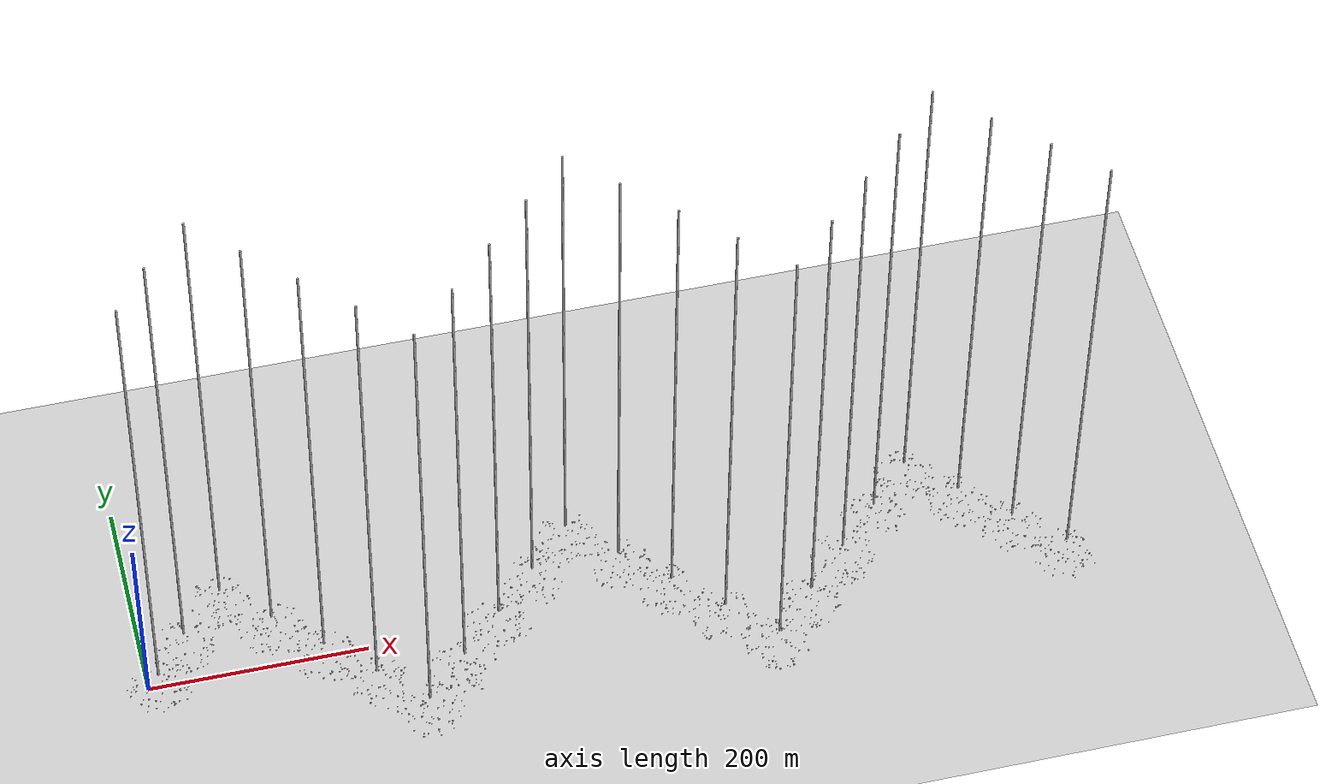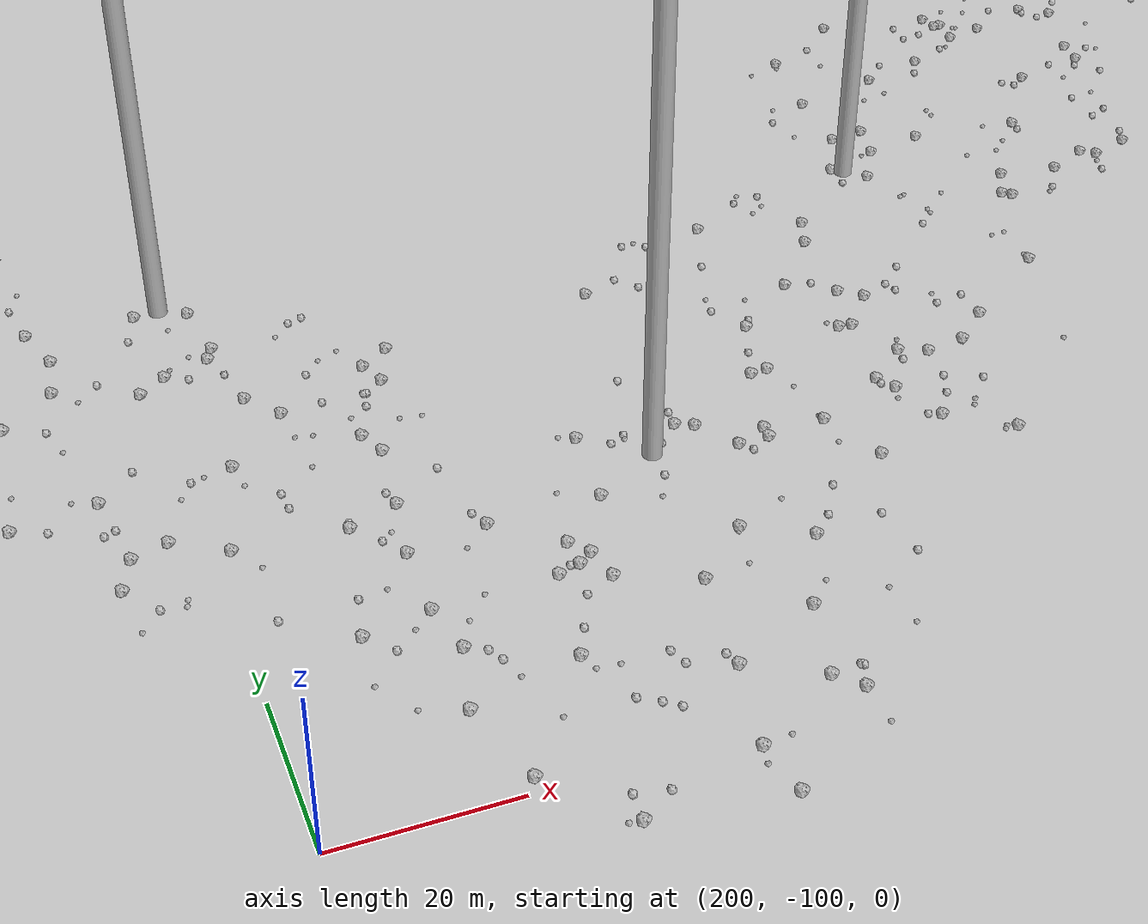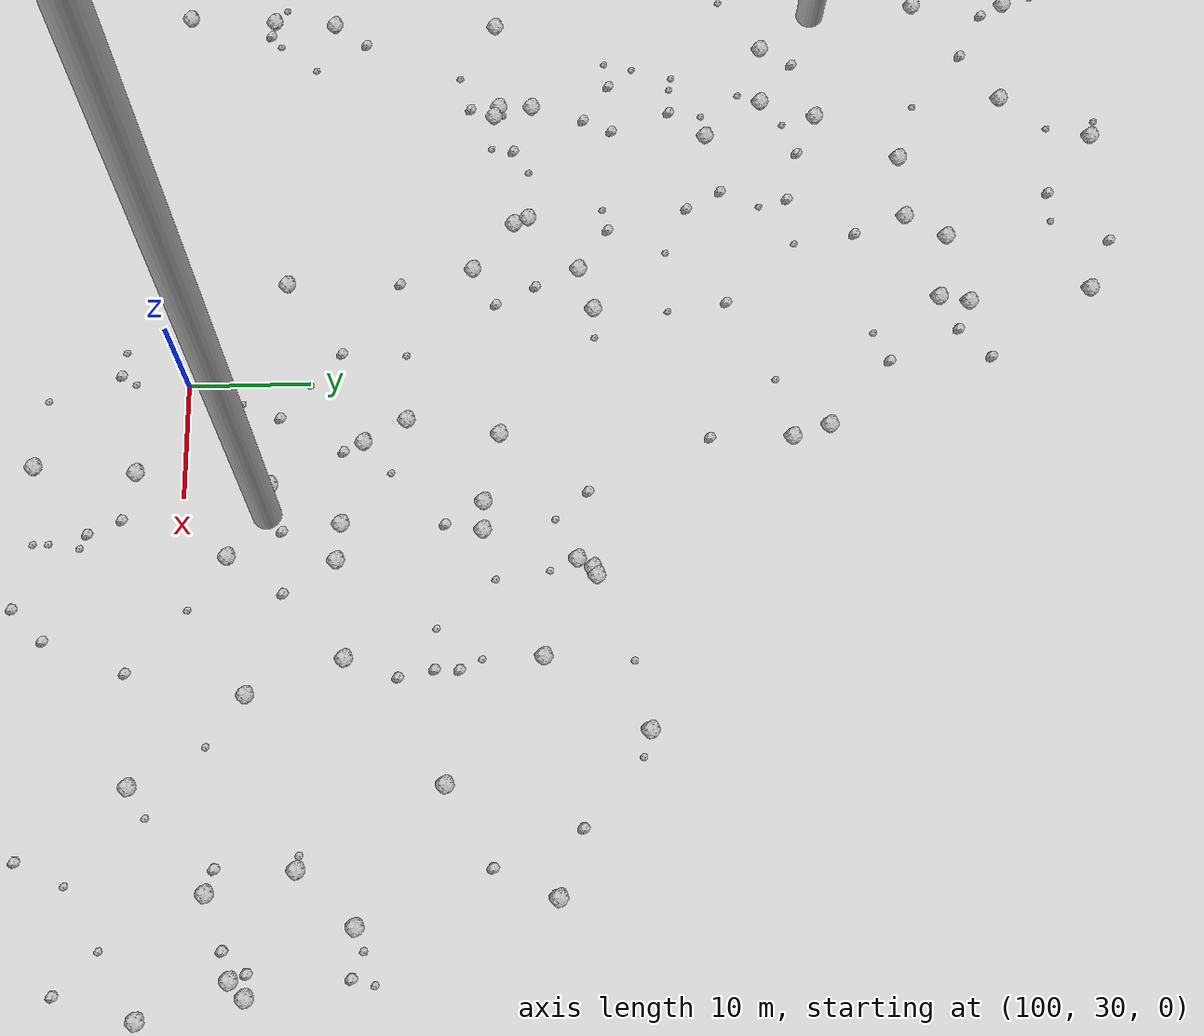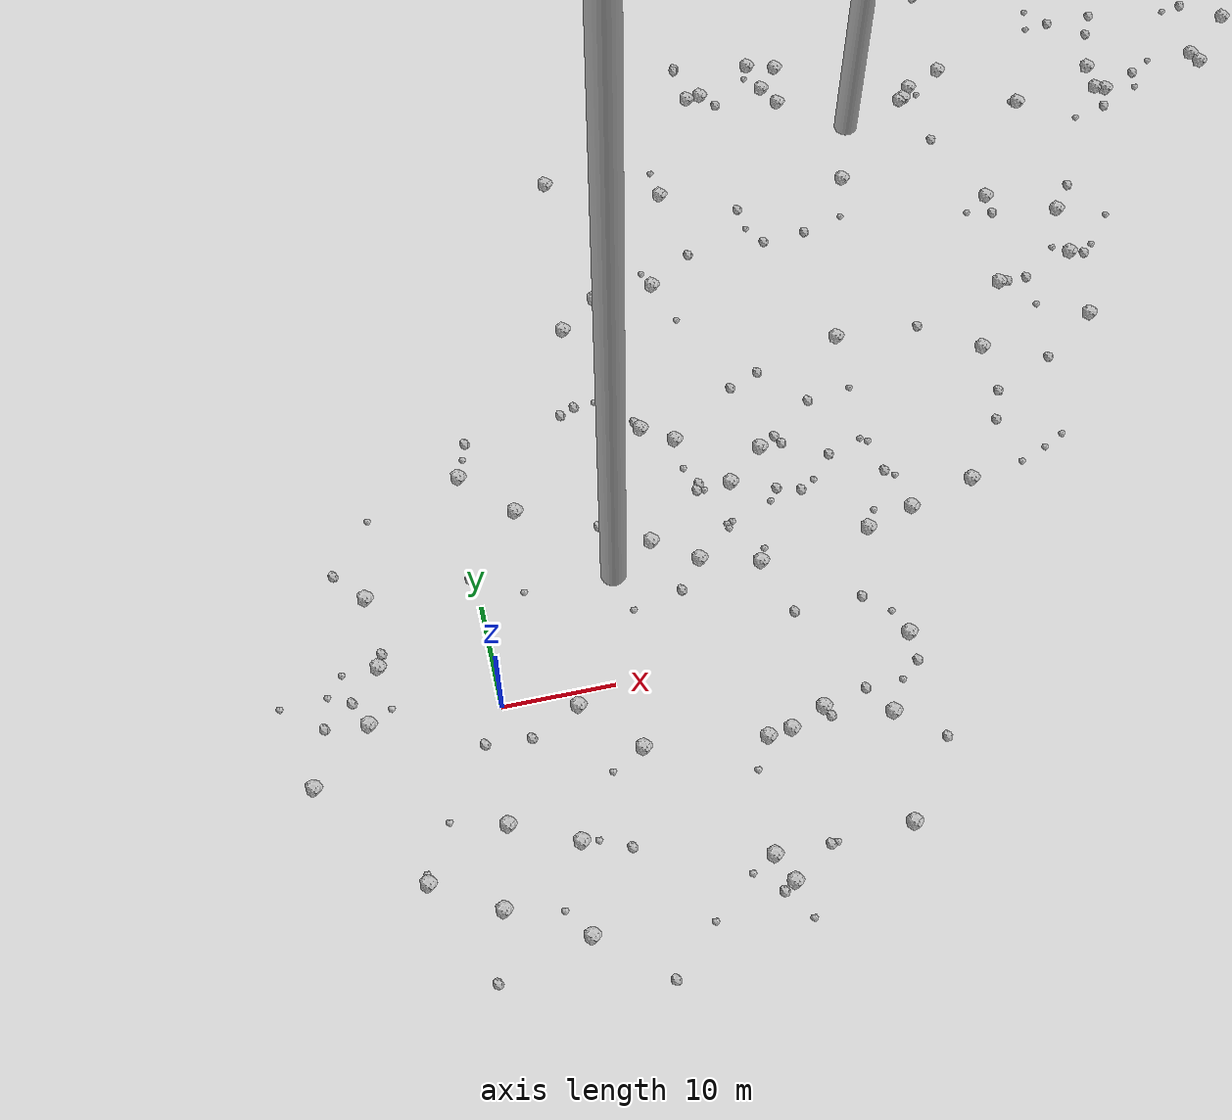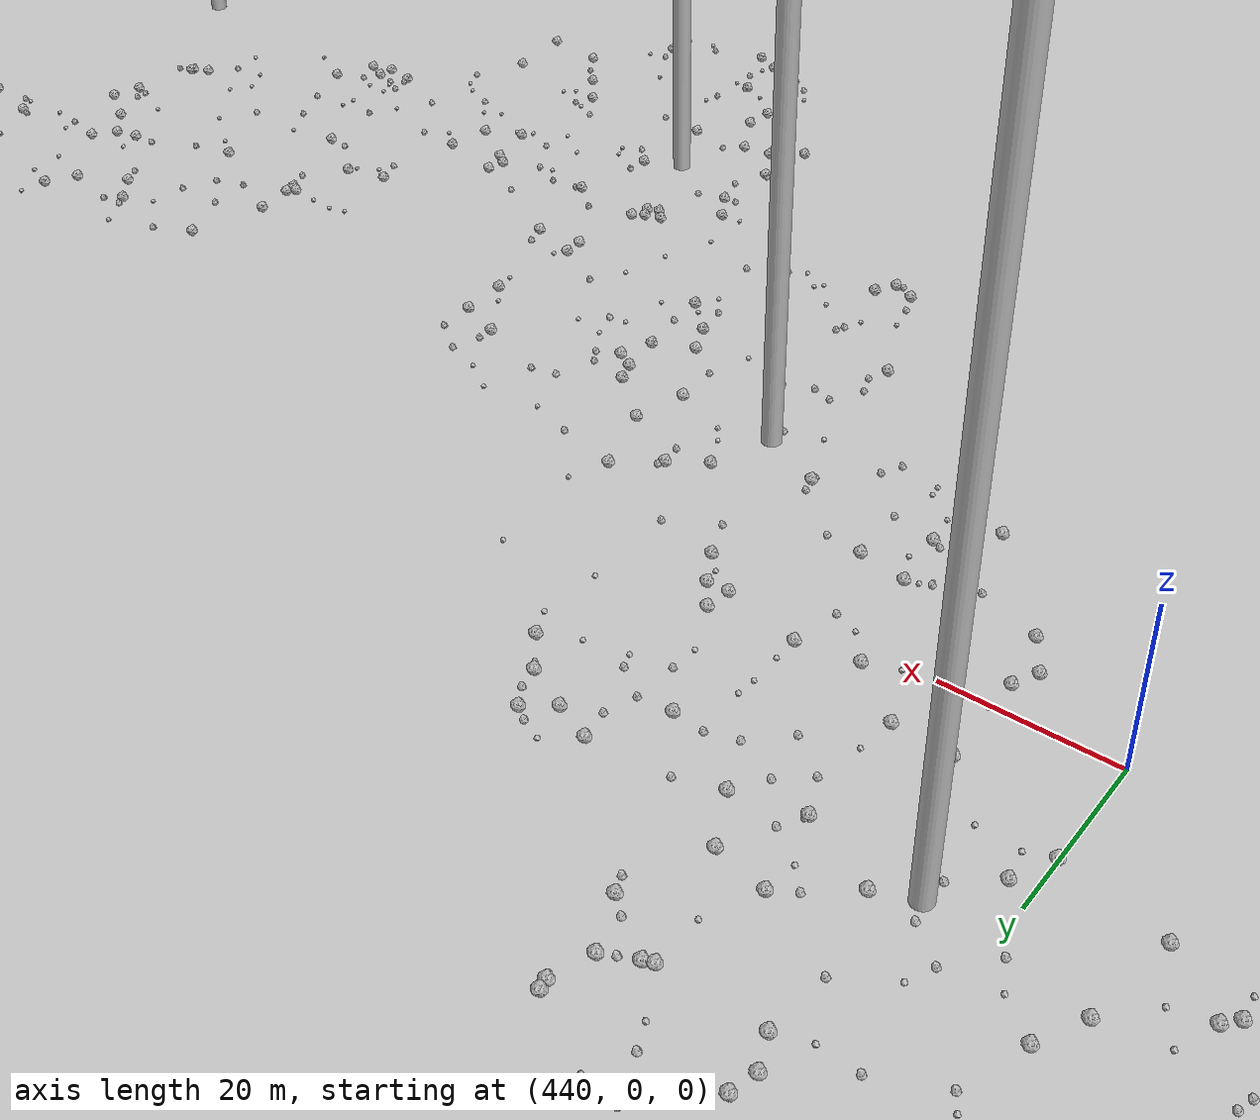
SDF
<sdf version="1.6">
 <world name="default">
  <include><uri>model://custom_ground</uri></include>
  <include><uri>model://sun</uri></include>
  <spherical_coordinates>
   <surface_model>EARTH_WGS84</surface_model>
   <latitude_deg>38.161479</latitude_deg>
   <longitude_deg>-122.454630</longitude_deg>
   <elevation>488.0</elevation>
   <heading_deg>90</heading_deg>
  </spherical_coordinates>
  <model name="rock1_0_0">
   <include><uri>model://rock1</uri><pose>0.4258869454625369 23.590470072798105 0.5 0 0 0</pose></include>
  </model>
  <model name="rock1_0_1">
   <include><uri>model://rock1</uri><pose>19.593265105103114 -18.298277100051422 0.5 0 0 0</pose></include>
  </model>
  <model name="rock1_0_2">
   <include><uri>model://rock1</uri><pose>-16.94204677330664 -4.062053096084782 0.5 0 0 0</pose></include>
  </model>
  <model name="rock1_0_3">
   <include><uri>model://rock1</uri><pose>35.865705066333454 10.217412509012853 0.5 0 0 0</pose></include>
  </model>
  <model name="rock1_0_4">
   <include><uri>model://rock1</uri><pose>4.186541190510887 -13.64281464550401 0.5 0 0 0</pose></include>
  </model>
  <model name="rock1_0_5">
   <include><uri>model://rock1</uri><pose>6.490779707301343 -1.3936061773794997 0.5 0 0 0</pose></include>
  </model>
  <model name="rock1_0_6">
   <include><uri>model://rock1</uri><pose>-1.532602621004461 -10.863521144166889 0.5 0 0 0</pose></include>
  </model>
  <model name="rock1_0_7">
   <include><uri>model://rock1</uri><pose>4.838600294089293 18.921575695923337 0.5 0 0 0</pose></include>
  </model>
  <model name="rock1_0_8">
   <include><uri>model://rock1</uri><pose>3.329555757908583 -21.830897044470593 0.5 0 0 0</pose></include>
  </model>
  <model name="rock1_0_9">
   <include><uri>model://rock1</uri><pose>11.104347467266237 -6.468998096717641 0.5 0 0 0</pose></include>
  </model>
  <model name="rock1_0_10">
   <include><uri>model://rock1</uri><pose>20.6625484039887 -20.903766457927855 0.5 0 0 0</pose></include>
  </model>
  <model name="rock1_0_11">
   <include><uri>model://rock1</uri><pose>17.987158346463147 25.176678825588972 0.5 0 0 0</pose></include>
  </model>
  <model name="rock1_0_12">
   <include><uri>model://rock1</uri><pose>25.463818453228534 8.960188977422256 0.5 0 0 0</pose></include>
  </model>
  <model name="rock1_0_13">
   <include><uri>model://rock1</uri><pose>-11.493227394271937 0.7471499509731174 0.5 0 0 0</pose></include>
  </model>
  <model name="rock1_0_14">
   <include><uri>model://rock1</uri><pose>-9.861687507869286 5.99554561775021 0.5 0 0 0</pose></include>
  </model>
  <model name="rock1_0_15">
   <include><uri>model://rock1</uri><pose>-8.946502069080402 -14.551512535602669 0.5 0 0 0</pose></include>
  </model>
  <model name="rock1_0_16">
   <include><uri>model://rock1</uri><pose>32.932538366023955 -7.910678944588451 0.5 0 0 0</pose></include>
  </model>
  <model name="rock1_0_17">
   <include><uri>model://rock1</uri><pose>31.746079077972198 -18.080295306039815 0.5 0 0 0</pose></include>
  </model>
  <model name="rock1_0_18">
   <include><uri>model://rock1</uri><pose>16.268638155541083 13.162128377371204 0.5 0 0 0</pose></include>
  </model>
  <model name="rock1_0_19">
   <include><uri>model://rock1</uri><pose>-9.906931575312157 12.962322399608539 0.5 0 0 0</pose></include>
  </model>
  <model name="rock1_0_20">
   <include><uri>model://rock1</uri><pose>-3.2731884722957467 -18.08198719907032 0.5 0 0 0</pose></include>
  </model>
  <model name="rock1_0_21">
   <include><uri>model://rock1</uri><pose>23.93849883882006 -7.529160160370676 0.5 0 0 0</pose></include>
  </model>
  <model name="rock1_0_22">
   <include><uri>model://rock1</uri><pose>20.147349211679114 10.437314945607682 0.5 0 0 0</pose></include>
  </model>
  <model name="rock1_0_23">
   <include><uri>model://rock1</uri><pose>21.786709616385103 -7.823435827018798 0.5 0 0 0</pose></include>
  </model>
  <model name="rock1_0_24">
   <include><uri>model://rock1</uri><pose>24.819069499509077 17.64397388436653 0.5 0 0 0</pose></include>
  </model>
  <model name="rock1_0_25">
   <include><uri>model://rock1</uri><pose>27.183809682259003 -6.147903388154386 0.5 0 0 0</pose></include>
  </model>
  <model name="rock1_0_26">
   <include><uri>model://rock1</uri><pose>36.44452362905187 -0.8603012842579325 0.5 0 0 0</pose></include>
  </model>
  <model name="rock2_0_0">
   <include><uri>model://rock2</uri><pose>36.74653862486327 -11.099335003345274 0.3 0 0 0</pose></include>
  </model>
  <model name="rock2_0_1">
   <include><uri>model://rock2</uri><pose>12.752762448049282 14.190941927365316 0.3 0 0 0</pose></include>
  </model>
  <model name="rock2_0_2">
   <include><uri>model://rock2</uri><pose>27.559285180786205 -7.045418463428039 0.3 0 0 0</pose></include>
  </model>
  <model name="rock2_0_3">
   <include><uri>model://rock2</uri><pose>-12.643349906243518 3.159417456817927 0.3 0 0 0</pose></include>
  </model>
  <model name="rock2_0_4">
   <include><uri>model://rock2</uri><pose>10.973704333424198 28.373084472510897 0.3 0 0 0</pose></include>
  </model>
  <model name="rock2_0_5">
   <include><uri>model://rock2</uri><pose>8.173398960551783 -15.024386599141245 0.3 0 0 0</pose></include>
  </model>
  <model name="rock2_0_6">
   <include><uri>model://rock2</uri><pose>36.374686372238365 -3.545614506958067 0.3 0 0 0</pose></include>
  </model>
  <model name="rock2_0_7">
   <include><uri>model://rock2</uri><pose>33.36197876264485 3.6057587444407986 0.3 0 0 0</pose></include>
  </model>
  <model name="rock2_0_8">
   <include><uri>model://rock2</uri><pose>-12.417822318014144 15.921073528240115 0.3 0 0 0</pose></include>
  </model>
  <model name="rock2_0_9">
   <include><uri>model://rock2</uri><pose>24.39194947493847 -18.37083913707145 0.3 0 0 0</pose></include>
  </model>
  <model name="rock2_0_10">
   <include><uri>model://rock2</uri><pose>11.95122738227418 15.795883297621657 0.3 0 0 0</pose></include>
  </model>
  <model name="rock2_0_11">
   <include><uri>model://rock2</uri><pose>-2.1000453734531597 -3.190249576710645 0.3 0 0 0</pose></include>
  </model>
  <model name="rock2_0_12">
   <include><uri>model://rock2</uri><pose>1.9434485988709191 -3.484406953018258 0.3 0 0 0</pose></include>
  </model>
  <model name="rock2_0_13">
   <include><uri>model://rock2</uri><pose>-15.331597219395531 1.2382849415534807 0.3 0 0 0</pose></include>
  </model>
  <model name="rock2_0_14">
   <include><uri>model://rock2</uri><pose>17.819777052576868 7.75673685936431 0.3 0 0 0</pose></include>
  </model>
  <model name="rock2_0_15">
   <include><uri>model://rock2</uri><pose>9.129438965702917 -26.823179746083493 0.3 0 0 0</pose></include>
  </model>
  <model name="rock2_0_16">
   <include><uri>model://rock2</uri><pose>27.084671648839304 3.442530866274076 0.3 0 0 0</pose></include>
  </model>
  <model name="rock2_0_17">
   <include><uri>model://rock2</uri><pose>-9.387508849886384 7.2922011991056195 0.3 0 0 0</pose></include>
  </model>
  <model name="rock2_0_18">
   <include><uri>model://rock2</uri><pose>-4.93460723393728 -24.02176802981003 0.3 0 0 0</pose></include>
  </model>
  <model name="rock2_0_19">
   <include><uri>model://rock2</uri><pose>31.1931700446193 -5.173472885419194 0.3 0 0 0</pose></include>
  </model>
  <model name="rock2_0_20">
   <include><uri>model://rock2</uri><pose>30.466649509145284 20.867211277838777 0.3 0 0 0</pose></include>
  </model>
  <model name="rock2_0_21">
   <include><uri>model://rock2</uri><pose>19.56059635587355 -21.523302012057723 0.3 0 0 0</pose></include>
  </model>
  <model name="rock2_0_22">
   <include><uri>model://rock2</uri><pose>28.769339338102625 16.19908620753985 0.3 0 0 0</pose></include>
  </model>
  <model name="rock2_0_23">
   <include><uri>model://rock2</uri><pose>1.6229938029803535 27.209797742083033 0.3 0 0 0</pose></include>
  </model>
  <model name="rock2_0_24">
   <include><uri>model://rock2</uri><pose>21.557049382136988 17.556551728569723 0.3 0 0 0</pose></include>
  </model>
  <model name="rock2_0_25">
   <include><uri>model://rock2</uri><pose>-0.48715334006117317 12.970979095454737 0.3 0 0 0</pose></include>
  </model>
  <model name="rock2_0_26">
   <include><uri>model://rock2</uri><pose>21.881704164928394 18.24009109998302 0.3 0 0 0</pose></include>
  </model>
  <model name="rock3_0_0">
   <include><uri>model://rock3</uri><pose>13.383824211055753 -22.813315305171542 0.2 0 0 0</pose></include>
  </model>
  <model name="rock3_0_1">
   <include><uri>model://rock3</uri><pose>23.941809988336956 13.653523587089886 0.2 0 0 0</pose></include>
  </model>
  <model name="rock3_0_2">
   <include><uri>model://rock3</uri><pose>8.039029673605334 -8.04499058082326 0.2 0 0 0</pose></include>
  </model>
  <model name="rock3_0_3">
   <include><uri>model://rock3</uri><pose>34.578693694220334 -5.07106518549832 0.2 0 0 0</pose></include>
  </model>
  <model name="rock3_0_4">
   <include><uri>model://rock3</uri><pose>13.185509630365395 6.72332635514762 0.2 0 0 0</pose></include>
  </model>
  <model name="rock3_0_5">
   <include><uri>model://rock3</uri><pose>32.34545775779453 16.35381098545455 0.2 0 0 0</pose></include>
  </model>
  <model name="rock3_0_6">
   <include><uri>model://rock3</uri><pose>35.52950941920636 1.606861945583411 0.2 0 0 0</pose></include>
  </model>
  <model name="rock3_0_7">
   <include><uri>model://rock3</uri><pose>24.992397665416647 -18.302523669874486 0.2 0 0 0</pose></include>
  </model>
  <model name="rock3_0_8">
   <include><uri>model://rock3</uri><pose>23.412758651232863 13.51683518239436 0.2 0 0 0</pose></include>
  </model>
  <model name="rock3_0_9">
   <include><uri>model://rock3</uri><pose>32.69777951613009 -7.598579896960352 0.2 0 0 0</pose></include>
  </model>
  <model name="rock3_0_10">
   <include><uri>model://rock3</uri><pose>20.13186554845936 -10.57876803229497 0.2 0 0 0</pose></include>
  </model>
  <model name="rock3_0_11">
   <include><uri>model://rock3</uri><pose>11.654853409242712 12.285110895762415 0.2 0 0 0</pose></include>
  </model>
  <model name="rock3_0_12">
   <include><uri>model://rock3</uri><pose>21.34762166461745 -24.266583487043626 0.2 0 0 0</pose></include>
  </model>
  <model name="rock3_0_13">
   <include><uri>model://rock3</uri><pose>4.002045357692225 10.609769738195375 0.2 0 0 0</pose></include>
  </model>
  <model name="rock3_0_14">
   <include><uri>model://rock3</uri><pose>-8.940068437366014 -13.641304993250145 0.2 0 0 0</pose></include>
  </model>
  <model name="rock3_0_15">
   <include><uri>model://rock3</uri><pose>-8.538069028765754 20.919008909801335 0.2 0 0 0</pose></include>
  </model>
  <model name="rock3_0_16">
   <include><uri>model://rock3</uri><pose>26.084139611443526 10.294029844263342 0.2 0 0 0</pose></include>
  </model>
  <model name="rock3_0_17">
   <include><uri>model://rock3</uri><pose>-18.86014216908423 3.925941692821013 0.2 0 0 0</pose></include>
  </model>
  <model name="rock3_0_18">
   <include><uri>model://rock3</uri><pose>-6.34440866050652 -9.54852831885669 0.2 0 0 0</pose></include>
  </model>
  <model name="rock3_0_19">
   <include><uri>model://rock3</uri><pose>17.387636445751326 -19.46866315452212 0.2 0 0 0</pose></include>
  </model>
  <model name="rock3_0_20">
   <include><uri>model://rock3</uri><pose>-13.150813600155049 5.988297333911916 0.2 0 0 0</pose></include>
  </model>
  <model name="rock3_0_21">
   <include><uri>model://rock3</uri><pose>-9.383549565835636 1.8861318058111785 0.2 0 0 0</pose></include>
  </model>
  <model name="rock3_0_22">
   <include><uri>model://rock3</uri><pose>1.5316103787999822 -19.227763358975185 0.2 0 0 0</pose></include>
  </model>
  <model name="rock3_0_23">
   <include><uri>model://rock3</uri><pose>-14.66431329776135 4.120978430083163 0.2 0 0 0</pose></include>
  </model>
  <model name="rock3_0_24">
   <include><uri>model://rock3</uri><pose>1.1136775526863687 25.529144624980468 0.2 0 0 0</pose></include>
  </model>
  <model name="rock3_0_25">
   <include><uri>model://rock3</uri><pose>5.570371134384121 -13.830678422681927 0.2 0 0 0</pose></include>
  </model>
  <model name="rock3_0_26">
   <include><uri>model://rock3</uri><pose>23.475657182946186 13.004305636904348 0.2 0 0 0</pose></include>
  </model>
  <model name="rock1_1_0">
   <include><uri>model://rock1</uri><pose>64.98410755769315 55.844554085669934 0.5 0 0 0</pose></include>
  </model>
  <model name="rock1_1_1">
   <include><uri>model://rock1</uri><pose>31.672610735636553 63.670846156910876 0.5 0 0 0</pose></include>
  </model>
  <model name="rock1_1_2">
   <include><uri>model://rock1</uri><pose>52.07354887415629 27.081642550806286 0.5 0 0 0</pose></include>
  </model>
  <model name="rock1_1_3">
   <include><uri>model://rock1</uri><pose>26.064581559963457 51.94646758980496 0.5 0 0 0</pose></include>
  </model>
  <model name="rock1_1_4">
   <include><uri>model://rock1</uri><pose>40.70810486522568 61.22272899390836 0.5 0 0 0</pose></include>
  </model>
  <model name="rock1_1_5">
   <include><uri>model://rock1</uri><pose>16.969739139542025 40.76302950089036 0.5 0 0 0</pose></include>
  </model>
  <model name="rock1_1_6">
   <include><uri>model://rock1</uri><pose>46.61114167424049 13.159404243674526 0.5 0 0 0</pose></include>
  </model>
  <model name="rock1_1_7">
   <include><uri>model://rock1</uri><pose>63.94892501756666 36.13837737048154 0.5 0 0 0</pose></include>
  </model>
  <model name="rock1_1_8">
   <include><uri>model://rock1</uri><pose>53.174089579436675 58.72085386738823 0.5 0 0 0</pose></include>
  </model>
  <model name="rock1_1_9">
   <include><uri>model://rock1</uri><pose>58.03080367250479 44.644951754162605 0.5 0 0 0</pose></include>
  </model>
  <model name="rock1_1_10">
   <include><uri>model://rock1</uri><pose>15.091777684858316 55.7718201579944 0.5 0 0 0</pose></include>
  </model>
  <model name="rock1_1_11">
   <include><uri>model://rock1</uri><pose>39.551611790167726 63.41319823712484 0.5 0 0 0</pose></include>
  </model>
  <model name="rock1_1_12">
   <include><uri>model://rock1</uri><pose>38.87207219936717 66.72990747117727 0.5 0 0 0</pose></include>
  </model>
  <model name="rock1_1_13">
   <include><uri>model://rock1</uri><pose>13.205649129200506 37.793454956054006 0.5 0 0 0</pose></include>
  </model>
  <model name="rock1_1_14">
   <include><uri>model://rock1</uri><pose>44.53377167277843 49.99928931598809 0.5 0 0 0</pose></include>
  </model>
  <model name="rock1_1_15">
   <include><uri>model://rock1</uri><pose>33.10157414135838 63.8393382063165 0.5 0 0 0</pose></include>
  </model>
  <model name="rock1_1_16">
   <include><uri>model://rock1</uri><pose>54.54897990917265 60.18627251996771 0.5 0 0 0</pose></include>
  </model>
  <model name="rock1_1_17">
   <include><uri>model://rock1</uri><pose>22.77910339928902 41.15751907285713 0.5 0 0 0</pose></include>
  </model>
  <model name="rock1_1_18">
   <include><uri>model://rock1</uri><pose>63.397105395693806 28.61563786192798 0.5 0 0 0</pose></include>
  </model>
  <model name="rock1_1_19">
   <include><uri>model://rock1</uri><pose>56.04608277653617 34.128951587443396 0.5 0 0 0</pose></include>
  </model>
  <model name="rock1_1_20">
   <include><uri>model://rock1</uri><pose>28.394942595873122 20.72964129720727 0.5 0 0 0</pose></include>
  </model>
  <model name="rock1_1_21">
   <include><uri>model://rock1</uri><pose>41.64757824877455 65.8849354776282 0.5 0 0 0</pose></include>
  </model>
  <model name="rock1_1_22">
   <include><uri>model://rock1</uri><pose>38.70606171205391 31.276344184419553 0.5 0 0 0</pose></include>
  </model>
  <model name="rock1_1_23">
   <include><uri>model://rock1</uri><pose>53.61327397436388 58.916268975719376 0.5 0 0 0</pose></include>
  </model>
  <model name="rock1_1_24">
   <include><uri>model://rock1</uri><pose>64.43435860844416 41.51636171564685 0.5 0 0 0</pose></include>
  </model>
  <model name="rock1_1_25">
   <include><uri>model://rock1</uri><pose>40.35363744905402 11.487622505292176 0.5 0 0 0</pose></include>
  </model>
  <model name="rock1_1_26">
   <include><uri>model://rock1</uri><pose>20.871209763772633 23.284777406162576 0.5 0 0 0</pose></include>
  </model>
  <model name="rock2_1_0">
   <include><uri>model://rock2</uri><pose>58.00262534357672 42.61550405876575 0.3 0 0 0</pose></include>
  </model>
  <model name="rock2_1_1">
   <include><uri>model://rock2</uri><pose>52.010964349650834 22.082243746118202 0.3 0 0 0</pose></include>
  </model>
  <model name="rock2_1_2">
   <include><uri>model://rock2</uri><pose>17.586469244851614 26.088418935653454 0.3 0 0 0</pose></include>
  </model>
  <model name="rock2_1_3">
   <include><uri>model://rock2</uri><pose>66.48466487016469 44.351586277184694 0.3 0 0 0</pose></include>
  </model>
  <model name="rock2_1_4">
   <include><uri>model://rock2</uri><pose>38.989796881317574 15.876322485218708 0.3 0 0 0</pose></include>
  </model>
  <model name="rock2_1_5">
   <include><uri>model://rock2</uri><pose>39.012084996392126 44.391628532837316 0.3 0 0 0</pose></include>
  </model>
  <model name="rock2_1_6">
   <include><uri>model://rock2</uri><pose>58.793387215313196 34.22707541261013 0.3 0 0 0</pose></include>
  </model>
  <model name="rock2_1_7">
   <include><uri>model://rock2</uri><pose>56.8729019073364 34.21602384914249 0.3 0 0 0</pose></include>
  </model>
  <model name="rock2_1_8">
   <include><uri>model://rock2</uri><pose>34.76905931200103 44.07873555135822 0.3 0 0 0</pose></include>
  </model>
  <model name="rock2_1_9">
   <include><uri>model://rock2</uri><pose>30.94247619664904 15.570512438708299 0.3 0 0 0</pose></include>
  </model>
  <model name="rock2_1_10">
   <include><uri>model://rock2</uri><pose>30.00503261077746 21.736279870319805 0.3 0 0 0</pose></include>
  </model>
  <model name="rock2_1_11">
   <include><uri>model://rock2</uri><pose>50.825222670123964 18.9740911109772 0.3 0 0 0</pose></include>
  </model>
  <model name="rock2_1_12">
   <include><uri>model://rock2</uri><pose>34.35598467066549 62.41173833252345 0.3 0 0 0</pose></include>
  </model>
  <model name="rock2_1_13">
   <include><uri>model://rock2</uri><pose>31.218607658028898 67.94204534949111 0.3 0 0 0</pose></include>
  </model>
  <model name="rock2_1_14">
   <include><uri>model://rock2</uri><pose>30.239254710218365 29.075984402615372 0.3 0 0 0</pose></include>
  </model>
  <model name="rock2_1_15">
   <include><uri>model://rock2</uri><pose>65.30388166189792 35.85059488690389 0.3 0 0 0</pose></include>
  </model>
  <model name="rock2_1_16">
   <include><uri>model://rock2</uri><pose>27.309397583953224 27.88529221211883 0.3 0 0 0</pose></include>
  </model>
  <model name="rock2_1_17">
   <include><uri>model://rock2</uri><pose>12.395290553394354 28.990258163975046 0.3 0 0 0</pose></include>
  </model>
  <model name="rock2_1_18">
   <include><uri>model://rock2</uri><pose>31.371400340516644 68.24283998921095 0.3 0 0 0</pose></include>
  </model>
  <model name="rock2_1_19">
   <include><uri>model://rock2</uri><pose>57.867146107938744 24.70147244127076 0.3 0 0 0</pose></include>
  </model>
  <model name="rock2_1_20">
   <include><uri>model://rock2</uri><pose>54.80431208438829 53.08953043729422 0.3 0 0 0</pose></include>
  </model>
  <model name="rock2_1_21">
   <include><uri>model://rock2</uri><pose>23.433050052375737 62.879879454105144 0.3 0 0 0</pose></include>
  </model>
  <model name="rock2_1_22">
   <include><uri>model://rock2</uri><pose>34.447030689990775 18.719238734984128 0.3 0 0 0</pose></include>
  </model>
  <model name="rock2_1_23">
   <include><uri>model://rock2</uri><pose>27.074234356277355 44.14110136288161 0.3 0 0 0</pose></include>
  </model>
  <model name="rock2_1_24">
   <include><uri>model://rock2</uri><pose>46.67301492961889 30.898435898208444 0.3 0 0 0</pose></include>
  </model>
  <model name="rock2_1_25">
   <include><uri>model://rock2</uri><pose>33.234047731548266 48.587137882776474 0.3 0 0 0</pose></include>
  </model>
  <model name="rock2_1_26">
   <include><uri>model://rock2</uri><pose>34.103266454029196 24.89516454818183 0.3 0 0 0</pose></include>
  </model>
  <model name="rock3_1_0">
   <include><uri>model://rock3</uri><pose>38.16017593350636 65.27525545874917 0.2 0 0 0</pose></include>
  </model>
  <model name="rock3_1_1">
   <include><uri>model://rock3</uri><pose>39.3736575218485 63.304805162693874 0.2 0 0 0</pose></include>
  </model>
  <model name="rock3_1_2">
   <include><uri>model://rock3</uri><pose>27.907995122378352 14.986921140047397 0.2 0 0 0</pose></include>
  </model>
  <model name="rock3_1_3">
   <include><uri>model://rock3</uri><pose>36.86507490301946 11.991985343716534 0.2 0 0 0</pose></include>
  </model>
  <model name="rock3_1_4">
   <include><uri>model://rock3</uri><pose>62.47293272315443 37.160468966339124 0.2 0 0 0</pose></include>
  </model>
  <model name="rock3_1_5">
   <include><uri>model://rock3</uri><pose>24.161024379019356 36.69152714173333 0.2 0 0 0</pose></include>
  </model>
  <model name="rock3_1_6">
   <include><uri>model://rock3</uri><pose>69.00965351346449 39.90484022244376 0.2 0 0 0</pose></include>
  </model>
  <model name="rock3_1_7">
   <include><uri>model://rock3</uri><pose>55.54411989046994 43.175845346743145 0.2 0 0 0</pose></include>
  </model>
  <model name="rock3_1_8">
   <include><uri>model://rock3</uri><pose>33.47208397288482 46.06825658871076 0.2 0 0 0</pose></include>
  </model>
  <model name="rock3_1_9">
   <include><uri>model://rock3</uri><pose>66.39566990127112 36.7156023953512 0.2 0 0 0</pose></include>
  </model>
  <model name="rock3_1_10">
   <include><uri>model://rock3</uri><pose>38.33706553280449 25.465709182878086 0.2 0 0 0</pose></include>
  </model>
  <model name="rock3_1_11">
   <include><uri>model://rock3</uri><pose>51.75180062214413 14.03901608665124 0.2 0 0 0</pose></include>
  </model>
  <model name="rock3_1_12">
   <include><uri>model://rock3</uri><pose>14.37847367126694 29.134283742520157 0.2 0 0 0</pose></include>
  </model>
  <model name="rock3_1_13">
   <include><uri>model://rock3</uri><pose>25.79825363143809 51.8222440835947 0.2 0 0 0</pose></include>
  </model>
  <model name="rock3_1_14">
   <include><uri>model://rock3</uri><pose>25.765131380674973 55.02258975467644 0.2 0 0 0</pose></include>
  </model>
  <model name="rock3_1_15">
   <include><uri>model://rock3</uri><pose>56.33545281339308 16.1155032620909 0.2 0 0 0</pose></include>
  </model>
  <model name="rock3_1_16">
   <include><uri>model://rock3</uri><pose>54.33558538177323 15.039677548379567 0.2 0 0 0</pose></include>
  </model>
  <model name="rock3_1_17">
   <include><uri>model://rock3</uri><pose>37.75376009070453 19.739659424269963 0.2 0 0 0</pose></include>
  </model>
  <model name="rock3_1_18">
   <include><uri>model://rock3</uri><pose>22.060761229392106 42.884221926377954 0.2 0 0 0</pose></include>
  </model>
  <model name="rock3_1_19">
   <include><uri>model://rock3</uri><pose>43.06597713934664 45.502259827393104 0.2 0 0 0</pose></include>
  </model>
  <model name="rock3_1_20">
   <include><uri>model://rock3</uri><pose>20.90362809241379 20.15199897426008 0.2 0 0 0</pose></include>
  </model>
  <model name="rock3_1_21">
   <include><uri>model://rock3</uri><pose>39.820235611402474 15.186842154778088 0.2 0 0 0</pose></include>
  </model>
  <model name="rock3_1_22">
   <include><uri>model://rock3</uri><pose>38.378297282314776 19.293019717684153 0.2 0 0 0</pose></include>
  </model>
  <model name="rock3_1_23">
   <include><uri>model://rock3</uri><pose>55.06952407212611 59.220803646788355 0.2 0 0 0</pose></include>
  </model>
  <model name="rock3_1_24">
   <include><uri>model://rock3</uri><pose>22.235887467095157 17.447601124811207 0.2 0 0 0</pose></include>
  </model>
  <model name="rock3_1_25">
   <include><uri>model://rock3</uri><pose>64.35146027282804 56.156273621141295 0.2 0 0 0</pose></include>
  </model>
  <model name="rock3_1_26">
   <include><uri>model://rock3</uri><pose>58.7694584741497 30.902529748541763 0.2 0 0 0</pose></include>
  </model>
  <model name="rock1_2_0">
   <include><uri>model://rock1</uri><pose>53.70487012627354 78.0163582615425 0.5 0 0 0</pose></include>
  </model>
  <model name="rock1_2_1">
   <include><uri>model://rock1</uri><pose>63.72498872039212 93.3926535027764 0.5 0 0 0</pose></include>
  </model>
  <model name="rock1_2_2">
   <include><uri>model://rock1</uri><pose>85.57162977246193 90.57887620801145 0.5 0 0 0</pose></include>
  </model>
  <model name="rock1_2_3">
   <include><uri>model://rock1</uri><pose>105.08415413737211 82.47028225907675 0.5 0 0 0</pose></include>
  </model>
  <model name="rock1_2_4">
   <include><uri>model://rock1</uri><pose>73.6166826039281 79.00122041193981 0.5 0 0 0</pose></include>
  </model>
  <model name="rock1_2_5">
   <include><uri>model://rock1</uri><pose>62.09538491407659 102.80379825332659 0.5 0 0 0</pose></include>
  </model>
  <model name="rock1_2_6">
   <include><uri>model://rock1</uri><pose>93.48823849854281 92.69216921178625 0.5 0 0 0</pose></include>
  </model>
  <model name="rock1_2_7">
   <include><uri>model://rock1</uri><pose>93.99982272545793 95.1617084676568 0.5 0 0 0</pose></include>
  </model>
  <model name="rock1_2_8">
   <include><uri>model://rock1</uri><pose>84.88824348350894 58.28838603292262 0.5 0 0 0</pose></include>
  </model>
  <model name="rock1_2_9">
   <include><uri>model://rock1</uri><pose>68.03435658829845 79.38456992839234 0.5 0 0 0</pose></include>
  </model>
  <model name="rock1_2_10">
   <include><uri>model://rock1</uri><pose>75.25910559340225 83.68955690020161 0.5 0 0 0</pose></include>
  </model>
  <model name="rock1_2_11">
   <include><uri>model://rock1</uri><pose>74.51150492750551 55.595757960176385 0.5 0 0 0</pose></include>
  </model>
  <model name="rock1_2_12">
   <include><uri>model://rock1</uri><pose>79.71902963904839 90.5970692593325 0.5 0 0 0</pose></include>
  </model>
  <model name="rock1_2_13">
   <include><uri>model://rock1</uri><pose>63.77932271623678 101.59567942542975 0.5 0 0 0</pose></include>
  </model>
  <model name="rock1_2_14">
   <include><uri>model://rock1</uri><pose>106.04517752320581 79.38939927220744 0.5 0 0 0</pose></include>
  </model>
  <model name="rock1_2_15">
   <include><uri>model://rock1</uri><pose>87.66199790619987 93.91970135031707 0.5 0 0 0</pose></include>
  </model>
  <model name="rock1_2_16">
   <include><uri>model://rock1</uri><pose>89.78747023589673 53.51189734052273 0.5 0 0 0</pose></include>
  </model>
  <model name="rock1_2_17">
   <include><uri>model://rock1</uri><pose>93.02775823571181 105.48767821885613 0.5 0 0 0</pose></include>
  </model>
  <model name="rock1_2_18">
   <include><uri>model://rock1</uri><pose>85.43328572150025 57.05921632029821 0.5 0 0 0</pose></include>
  </model>
  <model name="rock1_2_19">
   <include><uri>model://rock1</uri><pose>93.85713681208897 63.56612409155697 0.5 0 0 0</pose></include>
  </model>
  <model name="rock1_2_20">
   <include><uri>model://rock1</uri><pose>73.63615284740081 58.87758105291842 0.5 0 0 0</pose></include>
  </model>
  <model name="rock1_2_21">
   <include><uri>model://rock1</uri><pose>73.54895436927339 56.02212750302716 0.5 0 0 0</pose></include>
  </model>
  <model name="rock1_2_22">
   <include><uri>model://rock1</uri><pose>73.84329619303833 100.09578339052115 0.5 0 0 0</pose></include>
  </model>
  <model name="rock1_2_23">
   <include><uri>model://rock1</uri><pose>58.20426736976749 61.79617973928379 0.5 0 0 0</pose></include>
  </model>
  <model name="rock1_2_24">
   <include><uri>model://rock1</uri><pose>77.02058483064789 73.95830882668075 0.5 0 0 0</pose></include>
  </model>
  <model name="rock1_2_25">
   <include><uri>model://rock1</uri><pose>77.94759161039342 107.55331802706294 0.5 0 0 0</pose></include>
  </model>
  <model name="rock1_2_26">
   <include><uri>model://rock1</uri><pose>89.99467636361365 62.43809829948988 0.5 0 0 0</pose></include>
  </model>
  <model name="rock2_2_0">
   <include><uri>model://rock2</uri><pose>83.52784958559937 103.1806900675314 0.3 0 0 0</pose></include>
  </model>
  <model name="rock2_2_1">
   <include><uri>model://rock2</uri><pose>74.9909575190627 63.39029837522598 0.3 0 0 0</pose></include>
  </model>
  <model name="rock2_2_2">
   <include><uri>model://rock2</uri><pose>69.66140210774184 82.09163093178691 0.3 0 0 0</pose></include>
  </model>
  <model name="rock2_2_3">
   <include><uri>model://rock2</uri><pose>88.33821438343 107.81302015331262 0.3 0 0 0</pose></include>
  </model>
  <model name="rock2_2_4">
   <include><uri>model://rock2</uri><pose>58.604084274857236 72.45556021991325 0.3 0 0 0</pose></include>
  </model>
  <model name="rock2_2_5">
   <include><uri>model://rock2</uri><pose>99.14446322961001 96.48833021505786 0.3 0 0 0</pose></include>
  </model>
  <model name="rock2_2_6">
   <include><uri>model://rock2</uri><pose>64.84328600751768 99.53878088972897 0.3 0 0 0</pose></include>
  </model>
  <model name="rock2_2_7">
   <include><uri>model://rock2</uri><pose>84.25436912970144 71.93095233326815 0.3 0 0 0</pose></include>
  </model>
  <model name="rock2_2_8">
   <include><uri>model://rock2</uri><pose>62.748098822859234 104.42613313615055 0.3 0 0 0</pose></include>
  </model>
  <model name="rock2_2_9">
   <include><uri>model://rock2</uri><pose>93.12032637711798 55.42129268228744 0.3 0 0 0</pose></include>
  </model>
  <model name="rock2_2_10">
   <include><uri>model://rock2</uri><pose>76.18131329349288 65.81984053444693 0.3 0 0 0</pose></include>
  </model>
  <model name="rock2_2_11">
   <include><uri>model://rock2</uri><pose>82.59559110338353 74.94303997489632 0.3 0 0 0</pose></include>
  </model>
  <model name="rock2_2_12">
   <include><uri>model://rock2</uri><pose>87.12960750414305 86.15496948281424 0.3 0 0 0</pose></include>
  </model>
  <model name="rock2_2_13">
   <include><uri>model://rock2</uri><pose>86.17693015119067 65.09166383074158 0.3 0 0 0</pose></include>
  </model>
  <model name="rock2_2_14">
   <include><uri>model://rock2</uri><pose>59.63380152708303 92.58163173503162 0.3 0 0 0</pose></include>
  </model>
  <model name="rock2_2_15">
   <include><uri>model://rock2</uri><pose>96.48914679817214 94.03425557499747 0.3 0 0 0</pose></include>
  </model>
  <model name="rock2_2_16">
   <include><uri>model://rock2</uri><pose>74.38234184205416 70.92570901079473 0.3 0 0 0</pose></include>
  </model>
  <model name="rock2_2_17">
   <include><uri>model://rock2</uri><pose>73.58498891920888 53.56075634299565 0.3 0 0 0</pose></include>
  </model>
  <model name="rock2_2_18">
   <include><uri>model://rock2</uri><pose>78.00840694179789 57.21617564741332 0.3 0 0 0</pose></include>
  </model>
  <model name="rock2_2_19">
   <include><uri>model://rock2</uri><pose>78.90282915265753 81.8493123865934 0.3 0 0 0</pose></include>
  </model>
  <model name="rock2_2_20">
   <include><uri>model://rock2</uri><pose>83.5225740971392 80.64396314769078 0.3 0 0 0</pose></include>
  </model>
  <model name="rock2_2_21">
   <include><uri>model://rock2</uri><pose>91.50939691983778 58.775318424565896 0.3 0 0 0</pose></include>
  </model>
  <model name="rock2_2_22">
   <include><uri>model://rock2</uri><pose>69.13504199768695 97.18077936297101 0.3 0 0 0</pose></include>
  </model>
  <model name="rock2_2_23">
   <include><uri>model://rock2</uri><pose>99.30518330041403 87.99361315068168 0.3 0 0 0</pose></include>
  </model>
  <model name="rock2_2_24">
   <include><uri>model://rock2</uri><pose>71.50549201173231 65.72364713568095 0.3 0 0 0</pose></include>
  </model>
  <model name="rock2_2_25">
   <include><uri>model://rock2</uri><pose>105.89967356539073 72.63677774479716 0.3 0 0 0</pose></include>
  </model>
  <model name="rock2_2_26">
   <include><uri>model://rock2</uri><pose>93.44535077543168 74.7636512854856 0.3 0 0 0</pose></include>
  </model>
  <model name="rock3_2_0">
   <include><uri>model://rock3</uri><pose>77.63673580028244 55.30205733373965 0.2 0 0 0</pose></include>
  </model>
  <model name="rock3_2_1">
   <include><uri>model://rock3</uri><pose>87.87084081910999 80.90737128659819 0.2 0 0 0</pose></include>
  </model>
  <model name="rock3_2_2">
   <include><uri>model://rock3</uri><pose>84.1091181772813 78.16763816436502 0.2 0 0 0</pose></include>
  </model>
  <model name="rock3_2_3">
   <include><uri>model://rock3</uri><pose>74.24490594421253 56.353613024768926 0.2 0 0 0</pose></include>
  </model>
  <model name="rock3_2_4">
   <include><uri>model://rock3</uri><pose>70.7165870176517 71.32143504384256 0.2 0 0 0</pose></include>
  </model>
  <model name="rock3_2_5">
   <include><uri>model://rock3</uri><pose>74.7938406382227 73.72069847670274 0.2 0 0 0</pose></include>
  </model>
  <model name="rock3_2_6">
   <include><uri>model://rock3</uri><pose>70.25542887547107 52.66322782908127 0.2 0 0 0</pose></include>
  </model>
  <model name="rock3_2_7">
   <include><uri>model://rock3</uri><pose>54.100234472565006 77.52559487179481 0.2 0 0 0</pose></include>
  </model>
  <model name="rock3_2_8">
   <include><uri>model://rock3</uri><pose>69.04569653052133 65.44354905518027 0.2 0 0 0</pose></include>
  </model>
  <model name="rock3_2_9">
   <include><uri>model://rock3</uri><pose>80.16554980352687 58.46234922325981 0.2 0 0 0</pose></include>
  </model>
  <model name="rock3_2_10">
   <include><uri>model://rock3</uri><pose>96.42105293300159 63.55698925222948 0.2 0 0 0</pose></include>
  </model>
  <model name="rock3_2_11">
   <include><uri>model://rock3</uri><pose>76.26722613638296 108.16175897851693 0.2 0 0 0</pose></include>
  </model>
  <model name="rock3_2_12">
   <include><uri>model://rock3</uri><pose>69.69352964178664 67.8521115063593 0.2 0 0 0</pose></include>
  </model>
  <model name="rock3_2_13">
   <include><uri>model://rock3</uri><pose>72.66819334546585 77.09803053709513 0.2 0 0 0</pose></include>
  </model>
  <model name="rock3_2_14">
   <include><uri>model://rock3</uri><pose>96.60273380220727 86.8386739508341 0.2 0 0 0</pose></include>
  </model>
  <model name="rock3_2_15">
   <include><uri>model://rock3</uri><pose>53.66097431131578 87.82322677672948 0.2 0 0 0</pose></include>
  </model>
  <model name="rock3_2_16">
   <include><uri>model://rock3</uri><pose>74.29931309182422 92.40408389674354 0.2 0 0 0</pose></include>
  </model>
  <model name="rock3_2_17">
   <include><uri>model://rock3</uri><pose>71.89501322625775 71.0668440892351 0.2 0 0 0</pose></include>
  </model>
  <model name="rock3_2_18">
   <include><uri>model://rock3</uri><pose>94.10212031837699 69.79896143479766 0.2 0 0 0</pose></include>
  </model>
  <model name="rock3_2_19">
   <include><uri>model://rock3</uri><pose>75.84306258401674 80.80535526766224 0.2 0 0 0</pose></include>
  </model>
  <model name="rock3_2_20">
   <include><uri>model://rock3</uri><pose>62.66378444905264 76.00610033924048 0.2 0 0 0</pose></include>
  </model>
  <model name="rock3_2_21">
   <include><uri>model://rock3</uri><pose>61.84825114597165 97.61825296256677 0.2 0 0 0</pose></include>
  </model>
  <model name="rock3_2_22">
   <include><uri>model://rock3</uri><pose>76.86298190802698 103.90424440795609 0.2 0 0 0</pose></include>
  </model>
  <model name="rock3_2_23">
   <include><uri>model://rock3</uri><pose>84.08114640372723 64.69986183706402 0.2 0 0 0</pose></include>
  </model>
  <model name="rock3_2_24">
   <include><uri>model://rock3</uri><pose>86.22012103916194 103.09329345295737 0.2 0 0 0</pose></include>
  </model>
  <model name="rock3_2_25">
   <include><uri>model://rock3</uri><pose>88.45934348282833 69.88829983653997 0.2 0 0 0</pose></include>
  </model>
  <model name="rock3_2_26">
   <include><uri>model://rock3</uri><pose>100.71497230493551 78.35667581504543 0.2 0 0 0</pose></include>
  </model>
  <model name="rock1_3_0">
   <include><uri>model://rock1</uri><pose>142.97413748998406 59.19389084519091 0.5 0 0 0</pose></include>
  </model>
  <model name="rock1_3_1">
   <include><uri>model://rock1</uri><pose>117.0066491766288 62.693738801697535 0.5 0 0 0</pose></include>
  </model>
  <model name="rock1_3_2">
   <include><uri>model://rock1</uri><pose>134.23765930815898 50.84373075723264 0.5 0 0 0</pose></include>
  </model>
  <model name="rock1_3_3">
   <include><uri>model://rock1</uri><pose>115.30795946120638 33.699523100888385 0.5 0 0 0</pose></include>
  </model>
  <model name="rock1_3_4">
   <include><uri>model://rock1</uri><pose>111.111923479166 54.093727185728774 0.5 0 0 0</pose></include>
  </model>
  <model name="rock1_3_5">
   <include><uri>model://rock1</uri><pose>117.67688569201007 62.94953518456748 0.5 0 0 0</pose></include>
  </model>
  <model name="rock1_3_6">
   <include><uri>model://rock1</uri><pose>124.01990048403971 43.07302293394683 0.5 0 0 0</pose></include>
  </model>
  <model name="rock1_3_7">
   <include><uri>model://rock1</uri><pose>103.69823552521733 47.926841858810015 0.5 0 0 0</pose></include>
  </model>
  <model name="rock1_3_8">
   <include><uri>model://rock1</uri><pose>144.7153781341866 44.15308803872927 0.5 0 0 0</pose></include>
  </model>
  <model name="rock1_3_9">
   <include><uri>model://rock1</uri><pose>124.2648516382979 58.58419537862246 0.5 0 0 0</pose></include>
  </model>
  <model name="rock1_3_10">
   <include><uri>model://rock1</uri><pose>105.19410582629348 55.46661147341693 0.5 0 0 0</pose></include>
  </model>
  <model name="rock1_3_11">
   <include><uri>model://rock1</uri><pose>109.22678230662913 36.89873610659873 0.5 0 0 0</pose></include>
  </model>
  <model name="rock1_3_12">
   <include><uri>model://rock1</uri><pose>140.40556463945404 39.739582399341735 0.5 0 0 0</pose></include>
  </model>
  <model name="rock1_3_13">
   <include><uri>model://rock1</uri><pose>90.86561051464201 37.89987969198221 0.5 0 0 0</pose></include>
  </model>
  <model name="rock1_3_14">
   <include><uri>model://rock1</uri><pose>112.73192047825825 42.67216785086345 0.5 0 0 0</pose></include>
  </model>
  <model name="rock1_3_15">
   <include><uri>model://rock1</uri><pose>149.58560633165945 36.24432325726012 0.5 0 0 0</pose></include>
  </model>
  <model name="rock1_3_16">
   <include><uri>model://rock1</uri><pose>107.1226659818521 17.804513574516342 0.5 0 0 0</pose></include>
  </model>
  <model name="rock1_3_17">
   <include><uri>model://rock1</uri><pose>115.85432960691098 42.332290388377295 0.5 0 0 0</pose></include>
  </model>
  <model name="rock1_3_18">
   <include><uri>model://rock1</uri><pose>148.30299663693717 35.05447270670054 0.5 0 0 0</pose></include>
  </model>
  <model name="rock1_3_19">
   <include><uri>model://rock1</uri><pose>113.56077944919005 54.002459101191334 0.5 0 0 0</pose></include>
  </model>
  <model name="rock1_3_20">
   <include><uri>model://rock1</uri><pose>126.75768746478762 35.50998332693251 0.5 0 0 0</pose></include>
  </model>
  <model name="rock1_3_21">
   <include><uri>model://rock1</uri><pose>133.78087677439518 26.88347548732416 0.5 0 0 0</pose></include>
  </model>
  <model name="rock1_3_22">
   <include><uri>model://rock1</uri><pose>116.23365848865438 61.46706896852594 0.5 0 0 0</pose></include>
  </model>
  <model name="rock1_3_23">
   <include><uri>model://rock1</uri><pose>107.84553331320302 26.09423804524263 0.5 0 0 0</pose></include>
  </model>
  <model name="rock1_3_24">
   <include><uri>model://rock1</uri><pose>105.61967558786523 44.439512134301005 0.5 0 0 0</pose></include>
  </model>
  <model name="rock1_3_25">
   <include><uri>model://rock1</uri><pose>141.96813914926315 33.038969814011594 0.5 0 0 0</pose></include>
  </model>
  <model name="rock1_3_26">
   <include><uri>model://rock1</uri><pose>130.38908974301268 66.58463108076472 0.5 0 0 0</pose></include>
  </model>
  <model name="rock2_3_0">
   <include><uri>model://rock2</uri><pose>115.20183766608834 12.406218796454855 0.3 0 0 0</pose></include>
  </model>
  <model name="rock2_3_1">
   <include><uri>model://rock2</uri><pose>125.03792662568821 50.11602154955689 0.3 0 0 0</pose></include>
  </model>
  <model name="rock2_3_2">
   <include><uri>model://rock2</uri><pose>121.91622505178005 19.56288178640363 0.3 0 0 0</pose></include>
  </model>
  <model name="rock2_3_3">
   <include><uri>model://rock2</uri><pose>111.85936878953491 25.172920112645908 0.3 0 0 0</pose></include>
  </model>
  <model name="rock2_3_4">
   <include><uri>model://rock2</uri><pose>148.382775399146 43.960911797564535 0.3 0 0 0</pose></include>
  </model>
  <model name="rock2_3_5">
   <include><uri>model://rock2</uri><pose>90.96498757533044 47.39434395231501 0.3 0 0 0</pose></include>
  </model>
  <model name="rock2_3_6">
   <include><uri>model://rock2</uri><pose>139.17001097330174 18.767038604087013 0.3 0 0 0</pose></include>
  </model>
  <model name="rock2_3_7">
   <include><uri>model://rock2</uri><pose>98.95329774314823 24.438412286440368 0.3 0 0 0</pose></include>
  </model>
  <model name="rock2_3_8">
   <include><uri>model://rock2</uri><pose>119.19448924220978 16.960084892112306 0.3 0 0 0</pose></include>
  </model>
  <model name="rock2_3_9">
   <include><uri>model://rock2</uri><pose>118.46762070276695 38.19250214159625 0.3 0 0 0</pose></include>
  </model>
  <model name="rock2_3_10">
   <include><uri>model://rock2</uri><pose>146.12113917362086 34.459559935832466 0.3 0 0 0</pose></include>
  </model>
  <model name="rock2_3_11">
   <include><uri>model://rock2</uri><pose>113.20254322234834 37.9926930357138 0.3 0 0 0</pose></include>
  </model>
  <model name="rock2_3_12">
   <include><uri>model://rock2</uri><pose>140.59971642543206 54.382134526167384 0.3 0 0 0</pose></include>
  </model>
  <model name="rock2_3_13">
   <include><uri>model://rock2</uri><pose>112.92183295983804 51.01256787612688 0.3 0 0 0</pose></include>
  </model>
  <model name="rock2_3_14">
   <include><uri>model://rock2</uri><pose>130.0191203390856 12.483036534975984 0.3 0 0 0</pose></include>
  </model>
  <model name="rock2_3_15">
   <include><uri>model://rock2</uri><pose>129.63281591398697 14.229549079577087 0.3 0 0 0</pose></include>
  </model>
  <model name="rock2_3_16">
   <include><uri>model://rock2</uri><pose>125.11628234599607 52.05192027371774 0.3 0 0 0</pose></include>
  </model>
  <model name="rock2_3_17">
   <include><uri>model://rock2</uri><pose>97.41479971947265 42.590899418224566 0.3 0 0 0</pose></include>
  </model>
  <model name="rock2_3_18">
   <include><uri>model://rock2</uri><pose>137.78939445633532 61.22915419625063 0.3 0 0 0</pose></include>
  </model>
  <model name="rock2_3_19">
   <include><uri>model://rock2</uri><pose>140.11086739086673 33.64535149894257 0.3 0 0 0</pose></include>
  </model>
  <model name="rock2_3_20">
   <include><uri>model://rock2</uri><pose>124.71114828524523 26.136555649095584 0.3 0 0 0</pose></include>
  </model>
  <model name="rock2_3_21">
   <include><uri>model://rock2</uri><pose>113.00819825281218 22.48554993698632 0.3 0 0 0</pose></include>
  </model>
  <model name="rock2_3_22">
   <include><uri>model://rock2</uri><pose>125.60606644097084 47.26718731470683 0.3 0 0 0</pose></include>
  </model>
  <model name="rock2_3_23">
   <include><uri>model://rock2</uri><pose>147.8230984784076 36.29807696469388 0.3 0 0 0</pose></include>
  </model>
  <model name="rock2_3_24">
   <include><uri>model://rock2</uri><pose>103.17785557606518 37.60489751539515 0.3 0 0 0</pose></include>
  </model>
  <model name="rock2_3_25">
   <include><uri>model://rock2</uri><pose>106.3487453491629 42.827213004622244 0.3 0 0 0</pose></include>
  </model>
  <model name="rock2_3_26">
   <include><uri>model://rock2</uri><pose>110.385618183819 62.55562226838984 0.3 0 0 0</pose></include>
  </model>
  <model name="rock3_3_0">
   <include><uri>model://rock3</uri><pose>99.74594161108509 25.6292590348318 0.2 0 0 0</pose></include>
  </model>
  <model name="rock3_3_1">
   <include><uri>model://rock3</uri><pose>96.7730637837347 24.70434502091222 0.2 0 0 0</pose></include>
  </model>
  <model name="rock3_3_2">
   <include><uri>model://rock3</uri><pose>117.06182134586314 59.26901633335857 0.2 0 0 0</pose></include>
  </model>
  <model name="rock3_3_3">
   <include><uri>model://rock3</uri><pose>130.70652515766147 32.58220404911962 0.2 0 0 0</pose></include>
  </model>
  <model name="rock3_3_4">
   <include><uri>model://rock3</uri><pose>101.11366736045424 18.52953759337702 0.2 0 0 0</pose></include>
  </model>
  <model name="rock3_3_5">
   <include><uri>model://rock3</uri><pose>124.7045704128481 65.6151960997449 0.2 0 0 0</pose></include>
  </model>
  <model name="rock3_3_6">
   <include><uri>model://rock3</uri><pose>136.0997578518657 28.266447026882563 0.2 0 0 0</pose></include>
  </model>
  <model name="rock3_3_7">
   <include><uri>model://rock3</uri><pose>139.2350389809789 39.9036712477335 0.2 0 0 0</pose></include>
  </model>
  <model name="rock3_3_8">
   <include><uri>model://rock3</uri><pose>132.4018638964631 65.96712199274396 0.2 0 0 0</pose></include>
  </model>
  <model name="rock3_3_9">
   <include><uri>model://rock3</uri><pose>108.28196441074766 46.654782256235315 0.2 0 0 0</pose></include>
  </model>
  <model name="rock3_3_10">
   <include><uri>model://rock3</uri><pose>97.66438135463257 47.901800642380046 0.2 0 0 0</pose></include>
  </model>
  <model name="rock3_3_11">
   <include><uri>model://rock3</uri><pose>148.86729168659684 45.63649319270582 0.2 0 0 0</pose></include>
  </model>
  <model name="rock3_3_12">
   <include><uri>model://rock3</uri><pose>119.03444383350472 15.67240596337144 0.2 0 0 0</pose></include>
  </model>
  <model name="rock3_3_13">
   <include><uri>model://rock3</uri><pose>149.38116661446895 35.80037970505312 0.2 0 0 0</pose></include>
  </model>
  <model name="rock3_3_14">
   <include><uri>model://rock3</uri><pose>117.69389280875427 54.940948773710446 0.2 0 0 0</pose></include>
  </model>
  <model name="rock3_3_15">
   <include><uri>model://rock3</uri><pose>114.17967788045488 21.887711081007733 0.2 0 0 0</pose></include>
  </model>
  <model name="rock3_3_16">
   <include><uri>model://rock3</uri><pose>141.05031174500192 22.52988571951395 0.2 0 0 0</pose></include>
  </model>
  <model name="rock3_3_17">
   <include><uri>model://rock3</uri><pose>101.7782403197437 34.45090794393138 0.2 0 0 0</pose></include>
  </model>
  <model name="rock3_3_18">
   <include><uri>model://rock3</uri><pose>113.72227184635986 19.39182320568339 0.2 0 0 0</pose></include>
  </model>
  <model name="rock3_3_19">
   <include><uri>model://rock3</uri><pose>112.70445827158306 59.81156817412876 0.2 0 0 0</pose></include>
  </model>
  <model name="rock3_3_20">
   <include><uri>model://rock3</uri><pose>108.00198482179626 25.928852154330443 0.2 0 0 0</pose></include>
  </model>
  <model name="rock3_3_21">
   <include><uri>model://rock3</uri><pose>121.66677787827177 50.255875067219975 0.2 0 0 0</pose></include>
  </model>
  <model name="rock3_3_22">
   <include><uri>model://rock3</uri><pose>124.26878056506811 53.781920185461885 0.2 0 0 0</pose></include>
  </model>
  <model name="rock3_3_23">
   <include><uri>model://rock3</uri><pose>113.72963692702066 18.13642307666494 0.2 0 0 0</pose></include>
  </model>
  <model name="rock3_3_24">
   <include><uri>model://rock3</uri><pose>119.6075380203833 30.692509367622606 0.2 0 0 0</pose></include>
  </model>
  <model name="rock3_3_25">
   <include><uri>model://rock3</uri><pose>100.22755134716421 39.97841531069554 0.2 0 0 0</pose></include>
  </model>
  <model name="rock3_3_26">
   <include><uri>model://rock3</uri><pose>146.40408530533256 44.787014125042894 0.2 0 0 0</pose></include>
  </model>
  <model name="rock1_4_0">
   <include><uri>model://rock1</uri><pose>161.40042176320816 -20.237013773294454 0.5 0 0 0</pose></include>
  </model>
  <model name="rock1_4_1">
   <include><uri>model://rock1</uri><pose>179.91414801192687 -5.3894108940352545 0.5 0 0 0</pose></include>
  </model>
  <model name="rock1_4_2">
   <include><uri>model://rock1</uri><pose>139.1758625868776 11.67006949559292 0.5 0 0 0</pose></include>
  </model>
  <model name="rock1_4_3">
   <include><uri>model://rock1</uri><pose>139.3304758950932 -15.142645002017467 0.5 0 0 0</pose></include>
  </model>
  <model name="rock1_4_4">
   <include><uri>model://rock1</uri><pose>159.83755426818792 15.722075507404405 0.5 0 0 0</pose></include>
  </model>
  <model name="rock1_4_5">
   <include><uri>model://rock1</uri><pose>145.90403093894164 15.332981192455925 0.5 0 0 0</pose></include>
  </model>
  <model name="rock1_4_6">
   <include><uri>model://rock1</uri><pose>187.55833452621658 -11.471784760983692 0.5 0 0 0</pose></include>
  </model>
  <model name="rock1_4_7">
   <include><uri>model://rock1</uri><pose>158.9531393034359 8.661060659106361 0.5 0 0 0</pose></include>
  </model>
  <model name="rock1_4_8">
   <include><uri>model://rock1</uri><pose>144.94911970748322 -14.793698115881126 0.5 0 0 0</pose></include>
  </model>
  <model name="rock1_4_9">
   <include><uri>model://rock1</uri><pose>184.5474390055753 11.796569045724866 0.5 0 0 0</pose></include>
  </model>
  <model name="rock1_4_10">
   <include><uri>model://rock1</uri><pose>158.70291823577526 25.972919924327563 0.5 0 0 0</pose></include>
  </model>
  <model name="rock1_4_11">
   <include><uri>model://rock1</uri><pose>151.0035309197864 28.439656052479876 0.5 0 0 0</pose></include>
  </model>
  <model name="rock1_4_12">
   <include><uri>model://rock1</uri><pose>169.10018468556706 -8.779906261867808 0.5 0 0 0</pose></include>
  </model>
  <model name="rock1_4_13">
   <include><uri>model://rock1</uri><pose>183.95675062919867 16.083205727536964 0.5 0 0 0</pose></include>
  </model>
  <model name="rock1_4_14">
   <include><uri>model://rock1</uri><pose>176.61701694408504 -0.5127422662945271 0.5 0 0 0</pose></include>
  </model>
  <model name="rock1_4_15">
   <include><uri>model://rock1</uri><pose>186.51548854011438 6.0350606463200975 0.5 0 0 0</pose></include>
  </model>
  <model name="rock1_4_16">
   <include><uri>model://rock1</uri><pose>157.27789453056164 28.370663964729125 0.5 0 0 0</pose></include>
  </model>
  <model name="rock1_4_17">
   <include><uri>model://rock1</uri><pose>144.6429544278956 4.774513276879041 0.5 0 0 0</pose></include>
  </model>
  <model name="rock1_4_18">
   <include><uri>model://rock1</uri><pose>138.06522444957636 11.621278270540422 0.5 0 0 0</pose></include>
  </model>
  <model name="rock1_4_19">
   <include><uri>model://rock1</uri><pose>151.6956569003433 -16.45085944051818 0.5 0 0 0</pose></include>
  </model>
  <model name="rock1_4_20">
   <include><uri>model://rock1</uri><pose>154.4374230023944 -23.783127780097253 0.5 0 0 0</pose></include>
  </model>
  <model name="rock1_4_21">
   <include><uri>model://rock1</uri><pose>162.92592286390664 -17.819783996321352 0.5 0 0 0</pose></include>
  </model>
  <model name="rock1_4_22">
   <include><uri>model://rock1</uri><pose>153.53962911557343 13.785704421169399 0.5 0 0 0</pose></include>
  </model>
  <model name="rock1_4_23">
   <include><uri>model://rock1</uri><pose>166.1870794620763 -1.3984577958864257 0.5 0 0 0</pose></include>
  </model>
  <model name="rock1_4_24">
   <include><uri>model://rock1</uri><pose>163.4285412059931 -27.794389653570807 0.5 0 0 0</pose></include>
  </model>
  <model name="rock1_4_25">
   <include><uri>model://rock1</uri><pose>185.62406763041034 10.630106061796312 0.5 0 0 0</pose></include>
  </model>
  <model name="rock1_4_26">
   <include><uri>model://rock1</uri><pose>179.21432524878895 12.162423947082011 0.5 0 0 0</pose></include>
  </model>
  <model name="rock2_4_0">
   <include><uri>model://rock2</uri><pose>169.62171787503445 -28.232928836494654 0.3 0 0 0</pose></include>
  </model>
  <model name="rock2_4_1">
   <include><uri>model://rock2</uri><pose>165.4017098480511 26.440280051793287 0.3 0 0 0</pose></include>
  </model>
  <model name="rock2_4_2">
   <include><uri>model://rock2</uri><pose>186.46667071620732 -5.526268585387967 0.3 0 0 0</pose></include>
  </model>
  <model name="rock2_4_3">
   <include><uri>model://rock2</uri><pose>140.9174358147517 -19.317387385033896 0.3 0 0 0</pose></include>
  </model>
  <model name="rock2_4_4">
   <include><uri>model://rock2</uri><pose>183.99565671272794 -0.18204196344818868 0.3 0 0 0</pose></include>
  </model>
  <model name="rock2_4_5">
   <include><uri>model://rock2</uri><pose>172.54488746330935 -17.383084787219488 0.3 0 0 0</pose></include>
  </model>
  <model name="rock2_4_6">
   <include><uri>model://rock2</uri><pose>149.03337866450875 22.295379482696006 0.3 0 0 0</pose></include>
  </model>
  <model name="rock2_4_7">
   <include><uri>model://rock2</uri><pose>139.8680348900806 15.136422550747845 0.3 0 0 0</pose></include>
  </model>
  <model name="rock2_4_8">
   <include><uri>model://rock2</uri><pose>174.9694945370282 -16.97420357633306 0.3 0 0 0</pose></include>
  </model>
  <model name="rock2_4_9">
   <include><uri>model://rock2</uri><pose>148.48988544630254 0.6309966717729232 0.3 0 0 0</pose></include>
  </model>
  <model name="rock2_4_10">
   <include><uri>model://rock2</uri><pose>142.28980443885823 4.6021524863584276 0.3 0 0 0</pose></include>
  </model>
  <model name="rock2_4_11">
   <include><uri>model://rock2</uri><pose>134.44330005340203 11.980085358556252 0.3 0 0 0</pose></include>
  </model>
  <model name="rock2_4_12">
   <include><uri>model://rock2</uri><pose>135.35601024136176 -10.238810324253144 0.3 0 0 0</pose></include>
  </model>
  <model name="rock2_4_13">
   <include><uri>model://rock2</uri><pose>182.73753079851576 -4.7876648664021175 0.3 0 0 0</pose></include>
  </model>
  <model name="rock2_4_14">
   <include><uri>model://rock2</uri><pose>185.12770295184475 8.221570956750455 0.3 0 0 0</pose></include>
  </model>
  <model name="rock2_4_15">
   <include><uri>model://rock2</uri><pose>163.3865245883116 -18.53919354259679 0.3 0 0 0</pose></include>
  </model>
  <model name="rock2_4_16">
   <include><uri>model://rock2</uri><pose>155.3462426801994 26.814497572802146 0.3 0 0 0</pose></include>
  </model>
  <model name="rock2_4_17">
   <include><uri>model://rock2</uri><pose>145.93311580505323 4.7607332313561415 0.3 0 0 0</pose></include>
  </model>
  <model name="rock2_4_18">
   <include><uri>model://rock2</uri><pose>139.3650923240512 -10.807365611104974 0.3 0 0 0</pose></include>
  </model>
  <model name="rock2_4_19">
   <include><uri>model://rock2</uri><pose>158.37856930097726 20.285412599403443 0.3 0 0 0</pose></include>
  </model>
  <model name="rock2_4_20">
   <include><uri>model://rock2</uri><pose>169.79316883730053 -19.622838457525326 0.3 0 0 0</pose></include>
  </model>
  <model name="rock2_4_21">
   <include><uri>model://rock2</uri><pose>166.39600658648013 -2.262177697920947 0.3 0 0 0</pose></include>
  </model>
  <model name="rock2_4_22">
   <include><uri>model://rock2</uri><pose>161.14271424158676 21.891598951123875 0.3 0 0 0</pose></include>
  </model>
  <model name="rock2_4_23">
   <include><uri>model://rock2</uri><pose>155.55839250939928 1.995539725710266 0.3 0 0 0</pose></include>
  </model>
  <model name="rock2_4_24">
   <include><uri>model://rock2</uri><pose>136.10841094820273 15.217697084144561 0.3 0 0 0</pose></include>
  </model>
  <model name="rock2_4_25">
   <include><uri>model://rock2</uri><pose>161.8266042088335 29.52753474387864 0.3 0 0 0</pose></include>
  </model>
  <model name="rock2_4_26">
   <include><uri>model://rock2</uri><pose>177.01025806360872 -18.36283860221321 0.3 0 0 0</pose></include>
  </model>
  <model name="rock3_4_0">
   <include><uri>model://rock3</uri><pose>169.3830801307477 11.596842168317991 0.2 0 0 0</pose></include>
  </model>
  <model name="rock3_4_1">
   <include><uri>model://rock3</uri><pose>169.4463922341232 16.956126395985862 0.2 0 0 0</pose></include>
  </model>
  <model name="rock3_4_2">
   <include><uri>model://rock3</uri><pose>140.1729159483933 -6.092283841173099 0.2 0 0 0</pose></include>
  </model>
  <model name="rock3_4_3">
   <include><uri>model://rock3</uri><pose>173.5499346234467 -4.325410897100934 0.2 0 0 0</pose></include>
  </model>
  <model name="rock3_4_4">
   <include><uri>model://rock3</uri><pose>155.39986458660204 -21.5038016698064 0.2 0 0 0</pose></include>
  </model>
  <model name="rock3_4_5">
   <include><uri>model://rock3</uri><pose>150.66163752214788 10.432216415775983 0.2 0 0 0</pose></include>
  </model>
  <model name="rock3_4_6">
   <include><uri>model://rock3</uri><pose>148.6574423820843 -4.209911415826891 0.2 0 0 0</pose></include>
  </model>
  <model name="rock3_4_7">
   <include><uri>model://rock3</uri><pose>187.91671708224078 -2.238343831649953 0.2 0 0 0</pose></include>
  </model>
  <model name="rock3_4_8">
   <include><uri>model://rock3</uri><pose>174.55700025637407 24.522514390471663 0.2 0 0 0</pose></include>
  </model>
  <model name="rock3_4_9">
   <include><uri>model://rock3</uri><pose>157.26824787454592 -7.158183545187335 0.2 0 0 0</pose></include>
  </model>
  <model name="rock3_4_10">
   <include><uri>model://rock3</uri><pose>162.86866302942758 -17.553227098224497 0.2 0 0 0</pose></include>
  </model>
  <model name="rock3_4_11">
   <include><uri>model://rock3</uri><pose>153.3723539641431 14.196233767663252 0.2 0 0 0</pose></include>
  </model>
  <model name="rock3_4_12">
   <include><uri>model://rock3</uri><pose>144.1016856369185 3.46733372279828 0.2 0 0 0</pose></include>
  </model>
  <model name="rock3_4_13">
   <include><uri>model://rock3</uri><pose>184.257827310258 8.225790981921627 0.2 0 0 0</pose></include>
  </model>
  <model name="rock3_4_14">
   <include><uri>model://rock3</uri><pose>163.01094861683026 -18.69322381409934 0.2 0 0 0</pose></include>
  </model>
  <model name="rock3_4_15">
   <include><uri>model://rock3</uri><pose>171.89886259123966 21.750456711447626 0.2 0 0 0</pose></include>
  </model>
  <model name="rock3_4_16">
   <include><uri>model://rock3</uri><pose>171.07096518343965 -19.35341306252972 0.2 0 0 0</pose></include>
  </model>
  <model name="rock3_4_17">
   <include><uri>model://rock3</uri><pose>185.84473580057102 3.570245209263092 0.2 0 0 0</pose></include>
  </model>
  <model name="rock3_4_18">
   <include><uri>model://rock3</uri><pose>177.16207031277767 -18.35843108286869 0.2 0 0 0</pose></include>
  </model>
  <model name="rock3_4_19">
   <include><uri>model://rock3</uri><pose>171.95450074309548 -11.351717347999745 0.2 0 0 0</pose></include>
  </model>
  <model name="rock3_4_20">
   <include><uri>model://rock3</uri><pose>168.66660532898422 25.490251086041475 0.2 0 0 0</pose></include>
  </model>
  <model name="rock3_4_21">
   <include><uri>model://rock3</uri><pose>145.8750475309564 25.395141586788384 0.2 0 0 0</pose></include>
  </model>
  <model name="rock3_4_22">
   <include><uri>model://rock3</uri><pose>180.92827388507573 15.567394680931137 0.2 0 0 0</pose></include>
  </model>
  <model name="rock3_4_23">
   <include><uri>model://rock3</uri><pose>171.7396109430585 -15.183582120948492 0.2 0 0 0</pose></include>
  </model>
  <model name="rock3_4_24">
   <include><uri>model://rock3</uri><pose>183.06805746728816 10.612457141872703 0.2 0 0 0</pose></include>
  </model>
  <model name="rock3_4_25">
   <include><uri>model://rock3</uri><pose>163.65203558963944 24.171149945738136 0.2 0 0 0</pose></include>
  </model>
  <model name="rock3_4_26">
   <include><uri>model://rock3</uri><pose>177.8845951132451 21.967333851173997 0.2 0 0 0</pose></include>
  </model>
  <model name="rock1_5_0">
   <include><uri>model://rock1</uri><pose>198.20293539029566 -27.504122989498725 0.5 0 0 0</pose></include>
  </model>
  <model name="rock1_5_1">
   <include><uri>model://rock1</uri><pose>177.62534933127276 -21.374861009548276 0.5 0 0 0</pose></include>
  </model>
  <model name="rock1_5_2">
   <include><uri>model://rock1</uri><pose>209.23409136134626 -32.379635637680884 0.5 0 0 0</pose></include>
  </model>
  <model name="rock1_5_3">
   <include><uri>model://rock1</uri><pose>200.47235734014322 -12.124468226052926 0.5 0 0 0</pose></include>
  </model>
  <model name="rock1_5_4">
   <include><uri>model://rock1</uri><pose>195.88729783890466 -53.91640410324977 0.5 0 0 0</pose></include>
  </model>
  <model name="rock1_5_5">
   <include><uri>model://rock1</uri><pose>191.6734920161859 -55.17655790797417 0.5 0 0 0</pose></include>
  </model>
  <model name="rock1_5_6">
   <include><uri>model://rock1</uri><pose>177.02404802815522 -47.458735707979464 0.5 0 0 0</pose></include>
  </model>
  <model name="rock1_5_7">
   <include><uri>model://rock1</uri><pose>201.85295561655496 -57.49063037573515 0.5 0 0 0</pose></include>
  </model>
  <model name="rock1_5_8">
   <include><uri>model://rock1</uri><pose>214.53888012850697 -58.33058755549075 0.5 0 0 0</pose></include>
  </model>
  <model name="rock1_5_9">
   <include><uri>model://rock1</uri><pose>205.12088135371872 -43.939509998394016 0.5 0 0 0</pose></include>
  </model>
  <model name="rock1_5_10">
   <include><uri>model://rock1</uri><pose>206.74521720775508 -13.56987779915076 0.5 0 0 0</pose></include>
  </model>
  <model name="rock1_5_11">
   <include><uri>model://rock1</uri><pose>206.98331470409937 -23.433245597528504 0.5 0 0 0</pose></include>
  </model>
  <model name="rock1_5_12">
   <include><uri>model://rock1</uri><pose>190.134708806806 -45.0319168922896 0.5 0 0 0</pose></include>
  </model>
  <model name="rock1_5_13">
   <include><uri>model://rock1</uri><pose>227.22759987680516 -28.72949741289333 0.5 0 0 0</pose></include>
  </model>
  <model name="rock1_5_14">
   <include><uri>model://rock1</uri><pose>207.86466999931042 -21.54702784257281 0.5 0 0 0</pose></include>
  </model>
  <model name="rock1_5_15">
   <include><uri>model://rock1</uri><pose>223.7040139186098 -31.19057013609396 0.5 0 0 0</pose></include>
  </model>
  <model name="rock1_5_16">
   <include><uri>model://rock1</uri><pose>180.36219760206512 -46.43448604333983 0.5 0 0 0</pose></include>
  </model>
  <model name="rock1_5_17">
   <include><uri>model://rock1</uri><pose>189.86016218758567 -59.69563603167261 0.5 0 0 0</pose></include>
  </model>
  <model name="rock1_5_18">
   <include><uri>model://rock1</uri><pose>212.53130994978838 -36.50786434572193 0.5 0 0 0</pose></include>
  </model>
  <model name="rock1_5_19">
   <include><uri>model://rock1</uri><pose>221.48150529242093 -46.94416215851429 0.5 0 0 0</pose></include>
  </model>
  <model name="rock1_5_20">
   <include><uri>model://rock1</uri><pose>225.016760626486 -34.49719302944522 0.5 0 0 0</pose></include>
  </model>
  <model name="rock1_5_21">
   <include><uri>model://rock1</uri><pose>201.46478879449754 -25.182966228005746 0.5 0 0 0</pose></include>
  </model>
  <model name="rock1_5_22">
   <include><uri>model://rock1</uri><pose>189.52073104021562 -17.56016391809463 0.5 0 0 0</pose></include>
  </model>
  <model name="rock1_5_23">
   <include><uri>model://rock1</uri><pose>220.3695493798208 -56.225102789148266 0.5 0 0 0</pose></include>
  </model>
  <model name="rock1_5_24">
   <include><uri>model://rock1</uri><pose>220.06134248350796 -43.5743612442081 0.5 0 0 0</pose></include>
  </model>
  <model name="rock1_5_25">
   <include><uri>model://rock1</uri><pose>188.61140664241276 -23.697487033555745 0.5 0 0 0</pose></include>
  </model>
  <model name="rock1_5_26">
   <include><uri>model://rock1</uri><pose>182.26500010884615 -28.699695811786974 0.5 0 0 0</pose></include>
  </model>
  <model name="rock2_5_0">
   <include><uri>model://rock2</uri><pose>226.30766954296138 -51.7962848149665 0.3 0 0 0</pose></include>
  </model>
  <model name="rock2_5_1">
   <include><uri>model://rock2</uri><pose>189.67975388296952 -50.432928772306965 0.3 0 0 0</pose></include>
  </model>
  <model name="rock2_5_2">
   <include><uri>model://rock2</uri><pose>203.85040164155936 -69.43456051356492 0.3 0 0 0</pose></include>
  </model>
  <model name="rock2_5_3">
   <include><uri>model://rock2</uri><pose>217.4565632355123 -35.96682652138856 0.3 0 0 0</pose></include>
  </model>
  <model name="rock2_5_4">
   <include><uri>model://rock2</uri><pose>217.64466955370892 -19.54507750623678 0.3 0 0 0</pose></include>
  </model>
  <model name="rock2_5_5">
   <include><uri>model://rock2</uri><pose>194.56151972931974 -40.7944865143237 0.3 0 0 0</pose></include>
  </model>
  <model name="rock2_5_6">
   <include><uri>model://rock2</uri><pose>180.097292355831 -29.96653383988685 0.3 0 0 0</pose></include>
  </model>
  <model name="rock2_5_7">
   <include><uri>model://rock2</uri><pose>222.02443239242007 -38.408783517563386 0.3 0 0 0</pose></include>
  </model>
  <model name="rock2_5_8">
   <include><uri>model://rock2</uri><pose>214.67900320835332 -57.33119999937997 0.3 0 0 0</pose></include>
  </model>
  <model name="rock2_5_9">
   <include><uri>model://rock2</uri><pose>222.36902902817084 -35.989707889612696 0.3 0 0 0</pose></include>
  </model>
  <model name="rock2_5_10">
   <include><uri>model://rock2</uri><pose>208.1511257387572 -26.856410819021477 0.3 0 0 0</pose></include>
  </model>
  <model name="rock2_5_11">
   <include><uri>model://rock2</uri><pose>186.83120760847808 -30.617745631246102 0.3 0 0 0</pose></include>
  </model>
  <model name="rock2_5_12">
   <include><uri>model://rock2</uri><pose>184.1661847401958 -47.78389798989434 0.3 0 0 0</pose></include>
  </model>
  <model name="rock2_5_13">
   <include><uri>model://rock2</uri><pose>191.00239422066196 -49.86519534434406 0.3 0 0 0</pose></include>
  </model>
  <model name="rock2_5_14">
   <include><uri>model://rock2</uri><pose>192.93699950323844 -63.64169485472697 0.3 0 0 0</pose></include>
  </model>
  <model name="rock2_5_15">
   <include><uri>model://rock2</uri><pose>198.84960796267742 -16.605361022050573 0.3 0 0 0</pose></include>
  </model>
  <model name="rock2_5_16">
   <include><uri>model://rock2</uri><pose>209.05867102508145 -50.13907061370736 0.3 0 0 0</pose></include>
  </model>
  <model name="rock2_5_17">
   <include><uri>model://rock2</uri><pose>219.4314600012005 -18.923919946183645 0.3 0 0 0</pose></include>
  </model>
  <model name="rock2_5_18">
   <include><uri>model://rock2</uri><pose>178.23283050884447 -46.03709843142115 0.3 0 0 0</pose></include>
  </model>
  <model name="rock2_5_19">
   <include><uri>model://rock2</uri><pose>200.23306414854025 -44.86127202044902 0.3 0 0 0</pose></include>
  </model>
  <model name="rock2_5_20">
   <include><uri>model://rock2</uri><pose>219.77863032202822 -53.94167985017887 0.3 0 0 0</pose></include>
  </model>
  <model name="rock2_5_21">
   <include><uri>model://rock2</uri><pose>222.7330145164401 -36.05401996139972 0.3 0 0 0</pose></include>
  </model>
  <model name="rock2_5_22">
   <include><uri>model://rock2</uri><pose>209.2603260226606 -52.73914840390432 0.3 0 0 0</pose></include>
  </model>
  <model name="rock2_5_23">
   <include><uri>model://rock2</uri><pose>193.78934284155542 -23.759830636862155 0.3 0 0 0</pose></include>
  </model>
  <model name="rock2_5_24">
   <include><uri>model://rock2</uri><pose>204.06987726658838 -26.351629376405484 0.3 0 0 0</pose></include>
  </model>
  <model name="rock2_5_25">
   <include><uri>model://rock2</uri><pose>217.05056627334207 -30.244732230647088 0.3 0 0 0</pose></include>
  </model>
  <model name="rock2_5_26">
   <include><uri>model://rock2</uri><pose>182.19470120517357 -27.693339157965823 0.3 0 0 0</pose></include>
  </model>
  <model name="rock3_5_0">
   <include><uri>model://rock3</uri><pose>195.95319872109462 -63.085628947261654 0.2 0 0 0</pose></include>
  </model>
  <model name="rock3_5_1">
   <include><uri>model://rock3</uri><pose>175.30322980027435 -25.550498390827308 0.2 0 0 0</pose></include>
  </model>
  <model name="rock3_5_2">
   <include><uri>model://rock3</uri><pose>190.5799595190005 -66.25804014505418 0.2 0 0 0</pose></include>
  </model>
  <model name="rock3_5_3">
   <include><uri>model://rock3</uri><pose>178.3639115645547 -29.438599744300816 0.2 0 0 0</pose></include>
  </model>
  <model name="rock3_5_4">
   <include><uri>model://rock3</uri><pose>204.28784314753986 -60.943384949708275 0.2 0 0 0</pose></include>
  </model>
  <model name="rock3_5_5">
   <include><uri>model://rock3</uri><pose>213.42917513597658 -46.7530823801117 0.2 0 0 0</pose></include>
  </model>
  <model name="rock3_5_6">
   <include><uri>model://rock3</uri><pose>176.32727625315843 -24.066134490068954 0.2 0 0 0</pose></include>
  </model>
  <model name="rock3_5_7">
   <include><uri>model://rock3</uri><pose>198.6747777713343 -47.22001467383329 0.2 0 0 0</pose></include>
  </model>
  <model name="rock3_5_8">
   <include><uri>model://rock3</uri><pose>187.3329830841219 -43.72217103206111 0.2 0 0 0</pose></include>
  </model>
  <model name="rock3_5_9">
   <include><uri>model://rock3</uri><pose>205.67236981341904 -47.302836058271126 0.2 0 0 0</pose></include>
  </model>
  <model name="rock3_5_10">
   <include><uri>model://rock3</uri><pose>202.31872215407418 -23.779906114208543 0.2 0 0 0</pose></include>
  </model>
  <model name="rock3_5_11">
   <include><uri>model://rock3</uri><pose>221.63316209539363 -26.895900817485575 0.2 0 0 0</pose></include>
  </model>
  <model name="rock3_5_12">
   <include><uri>model://rock3</uri><pose>212.93355519004822 -41.03634814950554 0.2 0 0 0</pose></include>
  </model>
  <model name="rock3_5_13">
   <include><uri>model://rock3</uri><pose>224.99620493047752 -41.82665973921404 0.2 0 0 0</pose></include>
  </model>
  <model name="rock3_5_14">
   <include><uri>model://rock3</uri><pose>214.94085336532527 -41.421841305671265 0.2 0 0 0</pose></include>
  </model>
  <model name="rock3_5_15">
   <include><uri>model://rock3</uri><pose>191.19793244452273 -26.15105617368696 0.2 0 0 0</pose></include>
  </model>
  <model name="rock3_5_16">
   <include><uri>model://rock3</uri><pose>203.80302216160013 -15.845906666454724 0.2 0 0 0</pose></include>
  </model>
  <model name="rock3_5_17">
   <include><uri>model://rock3</uri><pose>174.54072829663178 -41.67712643662024 0.2 0 0 0</pose></include>
  </model>
  <model name="rock3_5_18">
   <include><uri>model://rock3</uri><pose>187.9953356671132 -34.65140615223929 0.2 0 0 0</pose></include>
  </model>
  <model name="rock3_5_19">
   <include><uri>model://rock3</uri><pose>219.08870993634602 -27.977855326200576 0.2 0 0 0</pose></include>
  </model>
  <model name="rock3_5_20">
   <include><uri>model://rock3</uri><pose>181.37257545711384 -40.61301252385736 0.2 0 0 0</pose></include>
  </model>
  <model name="rock3_5_21">
   <include><uri>model://rock3</uri><pose>227.5528980328851 -42.186201229140025 0.2 0 0 0</pose></include>
  </model>
  <model name="rock3_5_22">
   <include><uri>model://rock3</uri><pose>204.96917913014164 -21.989864053019218 0.2 0 0 0</pose></include>
  </model>
  <model name="rock3_5_23">
   <include><uri>model://rock3</uri><pose>195.66478549128266 -64.03793728902208 0.2 0 0 0</pose></include>
  </model>
  <model name="rock3_5_24">
   <include><uri>model://rock3</uri><pose>201.8011546095706 -44.38394926147953 0.2 0 0 0</pose></include>
  </model>
  <model name="rock3_5_25">
   <include><uri>model://rock3</uri><pose>215.5124465011153 -21.68137382525765 0.2 0 0 0</pose></include>
  </model>
  <model name="rock3_5_26">
   <include><uri>model://rock3</uri><pose>219.82522763871305 -39.85013864016701 0.2 0 0 0</pose></include>
  </model>
  <model name="rock1_6_0">
   <include><uri>model://rock1</uri><pose>243.97643951971497 -108.64603447091204 0.5 0 0 0</pose></include>
  </model>
  <model name="rock1_6_1">
   <include><uri>model://rock1</uri><pose>245.2333474607364 -91.42146451981327 0.5 0 0 0</pose></include>
  </model>
  <model name="rock1_6_2">
   <include><uri>model://rock1</uri><pose>260.87022120349843 -76.48972320641057 0.5 0 0 0</pose></include>
  </model>
  <model name="rock1_6_3">
   <include><uri>model://rock1</uri><pose>230.95450617255133 -84.83420870232257 0.5 0 0 0</pose></include>
  </model>
  <model name="rock1_6_4">
   <include><uri>model://rock1</uri><pose>235.62867850985663 -72.09731708942681 0.5 0 0 0</pose></include>
  </model>
  <model name="rock1_6_5">
   <include><uri>model://rock1</uri><pose>246.9883554477337 -78.82090900988221 0.5 0 0 0</pose></include>
  </model>
  <model name="rock1_6_6">
   <include><uri>model://rock1</uri><pose>238.20340305856956 -74.97231342274577 0.5 0 0 0</pose></include>
  </model>
  <model name="rock1_6_7">
   <include><uri>model://rock1</uri><pose>218.26385420223042 -88.04914964788352 0.5 0 0 0</pose></include>
  </model>
  <model name="rock1_6_8">
   <include><uri>model://rock1</uri><pose>218.95333393126106 -73.36503788619291 0.5 0 0 0</pose></include>
  </model>
  <model name="rock1_6_9">
   <include><uri>model://rock1</uri><pose>253.64660661250105 -72.54875823219793 0.5 0 0 0</pose></include>
  </model>
  <model name="rock1_6_10">
   <include><uri>model://rock1</uri><pose>255.7680761700704 -98.5280798515011 0.5 0 0 0</pose></include>
  </model>
  <model name="rock1_6_11">
   <include><uri>model://rock1</uri><pose>220.3331737500137 -79.69465063075955 0.5 0 0 0</pose></include>
  </model>
  <model name="rock1_6_12">
   <include><uri>model://rock1</uri><pose>255.9293357479055 -54.89304489797847 0.5 0 0 0</pose></include>
  </model>
  <model name="rock1_6_13">
   <include><uri>model://rock1</uri><pose>235.52946098363213 -68.5335535348136 0.5 0 0 0</pose></include>
  </model>
  <model name="rock1_6_14">
   <include><uri>model://rock1</uri><pose>241.6072402158844 -62.6066470523276 0.5 0 0 0</pose></include>
  </model>
  <model name="rock1_6_15">
   <include><uri>model://rock1</uri><pose>242.50770952278071 -52.43696018098964 0.5 0 0 0</pose></include>
  </model>
  <model name="rock1_6_16">
   <include><uri>model://rock1</uri><pose>219.1332131676046 -64.24208215069041 0.5 0 0 0</pose></include>
  </model>
  <model name="rock1_6_17">
   <include><uri>model://rock1</uri><pose>221.24061943712326 -98.3604660048863 0.5 0 0 0</pose></include>
  </model>
  <model name="rock1_6_18">
   <include><uri>model://rock1</uri><pose>211.2337949762346 -74.75815212748695 0.5 0 0 0</pose></include>
  </model>
  <model name="rock1_6_19">
   <include><uri>model://rock1</uri><pose>228.85010239206997 -106.85625828391282 0.5 0 0 0</pose></include>
  </model>
  <model name="rock1_6_20">
   <include><uri>model://rock1</uri><pose>242.9862852358799 -102.1822025712282 0.5 0 0 0</pose></include>
  </model>
  <model name="rock1_6_21">
   <include><uri>model://rock1</uri><pose>253.22229217904334 -95.87843109823581 0.5 0 0 0</pose></include>
  </model>
  <model name="rock1_6_22">
   <include><uri>model://rock1</uri><pose>253.83713512852117 -53.89340656851243 0.5 0 0 0</pose></include>
  </model>
  <model name="rock1_6_23">
   <include><uri>model://rock1</uri><pose>255.89729393092415 -86.189019333845 0.5 0 0 0</pose></include>
  </model>
  <model name="rock1_6_24">
   <include><uri>model://rock1</uri><pose>228.48164045552522 -62.75877844240195 0.5 0 0 0</pose></include>
  </model>
  <model name="rock1_6_25">
   <include><uri>model://rock1</uri><pose>237.33490212369867 -70.82555871438637 0.5 0 0 0</pose></include>
  </model>
  <model name="rock1_6_26">
   <include><uri>model://rock1</uri><pose>233.0115867375088 -72.90223000242186 0.5 0 0 0</pose></include>
  </model>
  <model name="rock2_6_0">
   <include><uri>model://rock2</uri><pose>213.94940966807465 -77.65799897925933 0.3 0 0 0</pose></include>
  </model>
  <model name="rock2_6_1">
   <include><uri>model://rock2</uri><pose>222.55533940825595 -80.72175059049798 0.3 0 0 0</pose></include>
  </model>
  <model name="rock2_6_2">
   <include><uri>model://rock2</uri><pose>245.86345303944668 -54.489222228976956 0.3 0 0 0</pose></include>
  </model>
  <model name="rock2_6_3">
   <include><uri>model://rock2</uri><pose>256.6285369753356 -95.45011423616494 0.3 0 0 0</pose></include>
  </model>
  <model name="rock2_6_4">
   <include><uri>model://rock2</uri><pose>249.44664929841795 -61.613385964034975 0.3 0 0 0</pose></include>
  </model>
  <model name="rock2_6_5">
   <include><uri>model://rock2</uri><pose>263.4591774323073 -73.86674768099856 0.3 0 0 0</pose></include>
  </model>
  <model name="rock2_6_6">
   <include><uri>model://rock2</uri><pose>232.69061570929648 -104.13962281952449 0.3 0 0 0</pose></include>
  </model>
  <model name="rock2_6_7">
   <include><uri>model://rock2</uri><pose>236.16279762315497 -93.37962915055753 0.3 0 0 0</pose></include>
  </model>
  <model name="rock2_6_8">
   <include><uri>model://rock2</uri><pose>233.9585275784256 -91.98519182696137 0.3 0 0 0</pose></include>
  </model>
  <model name="rock2_6_9">
   <include><uri>model://rock2</uri><pose>232.64928240983235 -81.08747168148454 0.3 0 0 0</pose></include>
  </model>
  <model name="rock2_6_10">
   <include><uri>model://rock2</uri><pose>251.23030000157274 -56.39694105778784 0.3 0 0 0</pose></include>
  </model>
  <model name="rock2_6_11">
   <include><uri>model://rock2</uri><pose>227.49779637742336 -60.38679917491639 0.3 0 0 0</pose></include>
  </model>
  <model name="rock2_6_12">
   <include><uri>model://rock2</uri><pose>244.63861298206916 -89.46384987259216 0.3 0 0 0</pose></include>
  </model>
  <model name="rock2_6_13">
   <include><uri>model://rock2</uri><pose>268.9254614427385 -75.65694605686993 0.3 0 0 0</pose></include>
  </model>
  <model name="rock2_6_14">
   <include><uri>model://rock2</uri><pose>229.07690903186455 -103.38002527626693 0.3 0 0 0</pose></include>
  </model>
  <model name="rock2_6_15">
   <include><uri>model://rock2</uri><pose>223.50003919421718 -82.48177780525288 0.3 0 0 0</pose></include>
  </model>
  <model name="rock2_6_16">
   <include><uri>model://rock2</uri><pose>234.5948039472842 -71.83297502772008 0.3 0 0 0</pose></include>
  </model>
  <model name="rock2_6_17">
   <include><uri>model://rock2</uri><pose>234.69118536385332 -76.59099426462038 0.3 0 0 0</pose></include>
  </model>
  <model name="rock2_6_18">
   <include><uri>model://rock2</uri><pose>239.5670239539636 -87.1423350411084 0.3 0 0 0</pose></include>
  </model>
  <model name="rock2_6_19">
   <include><uri>model://rock2</uri><pose>237.7990974858358 -94.62762508661007 0.3 0 0 0</pose></include>
  </model>
  <model name="rock2_6_20">
   <include><uri>model://rock2</uri><pose>269.82237664166803 -82.28894425744846 0.3 0 0 0</pose></include>
  </model>
  <model name="rock2_6_21">
   <include><uri>model://rock2</uri><pose>256.87639910472365 -95.61173957232238 0.3 0 0 0</pose></include>
  </model>
  <model name="rock2_6_22">
   <include><uri>model://rock2</uri><pose>217.22151462131336 -61.38148112378423 0.3 0 0 0</pose></include>
  </model>
  <model name="rock2_6_23">
   <include><uri>model://rock2</uri><pose>240.3529716985295 -89.27752662836787 0.3 0 0 0</pose></include>
  </model>
  <model name="rock2_6_24">
   <include><uri>model://rock2</uri><pose>266.0567588972308 -69.60513694102593 0.3 0 0 0</pose></include>
  </model>
  <model name="rock2_6_25">
   <include><uri>model://rock2</uri><pose>247.7302545318491 -53.53507678359447 0.3 0 0 0</pose></include>
  </model>
  <model name="rock2_6_26">
   <include><uri>model://rock2</uri><pose>212.37245568459213 -69.14666987112776 0.3 0 0 0</pose></include>
  </model>
  <model name="rock3_6_0">
   <include><uri>model://rock3</uri><pose>216.58429390639083 -75.41792574360508 0.2 0 0 0</pose></include>
  </model>
  <model name="rock3_6_1">
   <include><uri>model://rock3</uri><pose>240.66819643184337 -51.40140468277825 0.2 0 0 0</pose></include>
  </model>
  <model name="rock3_6_2">
   <include><uri>model://rock3</uri><pose>231.75090034651714 -86.87354142123556 0.2 0 0 0</pose></include>
  </model>
  <model name="rock3_6_3">
   <include><uri>model://rock3</uri><pose>224.4233356962871 -85.35661459475018 0.2 0 0 0</pose></include>
  </model>
  <model name="rock3_6_4">
   <include><uri>model://rock3</uri><pose>218.5437209363423 -60.27991922657225 0.2 0 0 0</pose></include>
  </model>
  <model name="rock3_6_5">
   <include><uri>model://rock3</uri><pose>255.8894260738796 -103.42926835432277 0.2 0 0 0</pose></include>
  </model>
  <model name="rock3_6_6">
   <include><uri>model://rock3</uri><pose>215.59992826805103 -68.66995029618177 0.2 0 0 0</pose></include>
  </model>
  <model name="rock3_6_7">
   <include><uri>model://rock3</uri><pose>264.6474412170955 -91.9707858134175 0.2 0 0 0</pose></include>
  </model>
  <model name="rock3_6_8">
   <include><uri>model://rock3</uri><pose>252.30039188219757 -78.01576900418046 0.2 0 0 0</pose></include>
  </model>
  <model name="rock3_6_9">
   <include><uri>model://rock3</uri><pose>242.476470326904 -104.31280613542886 0.2 0 0 0</pose></include>
  </model>
  <model name="rock3_6_10">
   <include><uri>model://rock3</uri><pose>237.2413598736786 -60.398410471645136 0.2 0 0 0</pose></include>
  </model>
  <model name="rock3_6_11">
   <include><uri>model://rock3</uri><pose>234.28677482652998 -87.11755076519566 0.2 0 0 0</pose></include>
  </model>
  <model name="rock3_6_12">
   <include><uri>model://rock3</uri><pose>225.34819835867447 -65.45140638466088 0.2 0 0 0</pose></include>
  </model>
  <model name="rock3_6_13">
   <include><uri>model://rock3</uri><pose>210.46573303894425 -81.68991233703696 0.2 0 0 0</pose></include>
  </model>
  <model name="rock3_6_14">
   <include><uri>model://rock3</uri><pose>227.4608682099789 -106.51496901096603 0.2 0 0 0</pose></include>
  </model>
  <model name="rock3_6_15">
   <include><uri>model://rock3</uri><pose>259.83539343878476 -69.7099371104268 0.2 0 0 0</pose></include>
  </model>
  <model name="rock3_6_16">
   <include><uri>model://rock3</uri><pose>224.78711428542312 -72.88150669134109 0.2 0 0 0</pose></include>
  </model>
  <model name="rock3_6_17">
   <include><uri>model://rock3</uri><pose>246.22005763004492 -101.64300088128749 0.2 0 0 0</pose></include>
  </model>
  <model name="rock3_6_18">
   <include><uri>model://rock3</uri><pose>213.49321441326666 -86.19397396062038 0.2 0 0 0</pose></include>
  </model>
  <model name="rock3_6_19">
   <include><uri>model://rock3</uri><pose>247.9012952750549 -64.86815448661108 0.2 0 0 0</pose></include>
  </model>
  <model name="rock3_6_20">
   <include><uri>model://rock3</uri><pose>228.69122469625444 -62.659391467222264 0.2 0 0 0</pose></include>
  </model>
  <model name="rock3_6_21">
   <include><uri>model://rock3</uri><pose>222.09638344639504 -76.07365665311451 0.2 0 0 0</pose></include>
  </model>
  <model name="rock3_6_22">
   <include><uri>model://rock3</uri><pose>253.31651344360682 -73.0464095476272 0.2 0 0 0</pose></include>
  </model>
  <model name="rock3_6_23">
   <include><uri>model://rock3</uri><pose>258.71369250479245 -83.17080526399842 0.2 0 0 0</pose></include>
  </model>
  <model name="rock3_6_24">
   <include><uri>model://rock3</uri><pose>226.4233321351475 -91.91561962702822 0.2 0 0 0</pose></include>
  </model>
  <model name="rock3_6_25">
   <include><uri>model://rock3</uri><pose>247.59820119334017 -54.22331144946836 0.2 0 0 0</pose></include>
  </model>
  <model name="rock3_6_26">
   <include><uri>model://rock3</uri><pose>264.361590785372 -86.39836266298012 0.2 0 0 0</pose></include>
  </model>
  <model name="rock1_7_0">
   <include><uri>model://rock1</uri><pose>259.2948945170429 -59.69061517644346 0.5 0 0 0</pose></include>
  </model>
  <model name="rock1_7_1">
   <include><uri>model://rock1</uri><pose>269.1362554741842 -39.5586614105037 0.5 0 0 0</pose></include>
  </model>
  <model name="rock1_7_2">
   <include><uri>model://rock1</uri><pose>279.1631558782773 -54.17659255234117 0.5 0 0 0</pose></include>
  </model>
  <model name="rock1_7_3">
   <include><uri>model://rock1</uri><pose>253.41550928145722 -26.51424173927181 0.5 0 0 0</pose></include>
  </model>
  <model name="rock1_7_4">
   <include><uri>model://rock1</uri><pose>273.4656352195129 -66.795530077945 0.5 0 0 0</pose></include>
  </model>
  <model name="rock1_7_5">
   <include><uri>model://rock1</uri><pose>262.97004318529054 -59.60375064938271 0.5 0 0 0</pose></include>
  </model>
  <model name="rock1_7_6">
   <include><uri>model://rock1</uri><pose>296.86527028428605 -46.72534262392696 0.5 0 0 0</pose></include>
  </model>
  <model name="rock1_7_7">
   <include><uri>model://rock1</uri><pose>282.6984789543299 -36.63319082014299 0.5 0 0 0</pose></include>
  </model>
  <model name="rock1_7_8">
   <include><uri>model://rock1</uri><pose>263.11338789228654 -58.000695714213606 0.5 0 0 0</pose></include>
  </model>
  <model name="rock1_7_9">
   <include><uri>model://rock1</uri><pose>283.5869304712833 -25.42616082981901 0.5 0 0 0</pose></include>
  </model>
  <model name="rock1_7_10">
   <include><uri>model://rock1</uri><pose>279.5971592379603 -43.39913355414884 0.5 0 0 0</pose></include>
  </model>
  <model name="rock1_7_11">
   <include><uri>model://rock1</uri><pose>292.38401574041234 -50.672117946289134 0.5 0 0 0</pose></include>
  </model>
  <model name="rock1_7_12">
   <include><uri>model://rock1</uri><pose>277.17891797207943 -33.19739075412625 0.5 0 0 0</pose></include>
  </model>
  <model name="rock1_7_13">
   <include><uri>model://rock1</uri><pose>284.10848279977984 -50.02179578925072 0.5 0 0 0</pose></include>
  </model>
  <model name="rock1_7_14">
   <include><uri>model://rock1</uri><pose>268.00375882422753 -48.07025057471331 0.5 0 0 0</pose></include>
  </model>
  <model name="rock1_7_15">
   <include><uri>model://rock1</uri><pose>280.52783626564826 -56.45894860156533 0.5 0 0 0</pose></include>
  </model>
  <model name="rock1_7_16">
   <include><uri>model://rock1</uri><pose>283.2161581705582 -62.79978088126733 0.5 0 0 0</pose></include>
  </model>
  <model name="rock1_7_17">
   <include><uri>model://rock1</uri><pose>285.1173094087877 -21.276210917041972 0.5 0 0 0</pose></include>
  </model>
  <model name="rock1_7_18">
   <include><uri>model://rock1</uri><pose>271.96564005251633 -18.028142205279707 0.5 0 0 0</pose></include>
  </model>
  <model name="rock1_7_19">
   <include><uri>model://rock1</uri><pose>270.17626291046014 -58.91221067124438 0.5 0 0 0</pose></include>
  </model>
  <model name="rock1_7_20">
   <include><uri>model://rock1</uri><pose>265.5780681154055 -19.305638130135804 0.5 0 0 0</pose></include>
  </model>
  <model name="rock1_7_21">
   <include><uri>model://rock1</uri><pose>287.4281537839341 -51.4611770740485 0.5 0 0 0</pose></include>
  </model>
  <model name="rock1_7_22">
   <include><uri>model://rock1</uri><pose>265.88313688196786 -48.29542063286131 0.5 0 0 0</pose></include>
  </model>
  <model name="rock1_7_23">
   <include><uri>model://rock1</uri><pose>290.289969411878 -67.66324309416188 0.5 0 0 0</pose></include>
  </model>
  <model name="rock1_7_24">
   <include><uri>model://rock1</uri><pose>308.4149689030901 -38.54167651532035 0.5 0 0 0</pose></include>
  </model>
  <model name="rock1_7_25">
   <include><uri>model://rock1</uri><pose>285.3091608271569 -38.699340311008456 0.5 0 0 0</pose></include>
  </model>
  <model name="rock1_7_26">
   <include><uri>model://rock1</uri><pose>281.2460556470597 -43.592645951481856 0.5 0 0 0</pose></include>
  </model>
  <model name="rock2_7_0">
   <include><uri>model://rock2</uri><pose>280.4198571921633 -33.774900138255525 0.3 0 0 0</pose></include>
  </model>
  <model name="rock2_7_1">
   <include><uri>model://rock2</uri><pose>269.15714246807335 -25.735043061151494 0.3 0 0 0</pose></include>
  </model>
  <model name="rock2_7_2">
   <include><uri>model://rock2</uri><pose>250.74766483037868 -44.01717105165909 0.3 0 0 0</pose></include>
  </model>
  <model name="rock2_7_3">
   <include><uri>model://rock2</uri><pose>294.35430616335344 -14.1526680895239 0.3 0 0 0</pose></include>
  </model>
  <model name="rock2_7_4">
   <include><uri>model://rock2</uri><pose>285.6640262929393 -59.191176469479586 0.3 0 0 0</pose></include>
  </model>
  <model name="rock2_7_5">
   <include><uri>model://rock2</uri><pose>254.0487127210586 -51.49275992177109 0.3 0 0 0</pose></include>
  </model>
  <model name="rock2_7_6">
   <include><uri>model://rock2</uri><pose>261.40684048953403 -18.07724617885151 0.3 0 0 0</pose></include>
  </model>
  <model name="rock2_7_7">
   <include><uri>model://rock2</uri><pose>260.4477248570775 -60.99067481303001 0.3 0 0 0</pose></include>
  </model>
  <model name="rock2_7_8">
   <include><uri>model://rock2</uri><pose>282.353640423014 -13.339799910628933 0.3 0 0 0</pose></include>
  </model>
  <model name="rock2_7_9">
   <include><uri>model://rock2</uri><pose>291.07123029963793 -58.09294486715828 0.3 0 0 0</pose></include>
  </model>
  <model name="rock2_7_10">
   <include><uri>model://rock2</uri><pose>278.80142196576116 -13.806613308670997 0.3 0 0 0</pose></include>
  </model>
  <model name="rock2_7_11">
   <include><uri>model://rock2</uri><pose>296.6721670226385 -42.37031682583579 0.3 0 0 0</pose></include>
  </model>
  <model name="rock2_7_12">
   <include><uri>model://rock2</uri><pose>283.86903925108896 -51.71715603871834 0.3 0 0 0</pose></include>
  </model>
  <model name="rock2_7_13">
   <include><uri>model://rock2</uri><pose>281.78133086618465 -62.034984987601824 0.3 0 0 0</pose></include>
  </model>
  <model name="rock2_7_14">
   <include><uri>model://rock2</uri><pose>299.7331200522825 -26.587206970346955 0.3 0 0 0</pose></include>
  </model>
  <model name="rock2_7_15">
   <include><uri>model://rock2</uri><pose>286.8610561427738 -56.2145048794217 0.3 0 0 0</pose></include>
  </model>
  <model name="rock2_7_16">
   <include><uri>model://rock2</uri><pose>288.9714722430012 -37.07988251968331 0.3 0 0 0</pose></include>
  </model>
  <model name="rock2_7_17">
   <include><uri>model://rock2</uri><pose>264.22127056639295 -19.194604342501492 0.3 0 0 0</pose></include>
  </model>
  <model name="rock2_7_18">
   <include><uri>model://rock2</uri><pose>289.5315306438164 -38.690890817218886 0.3 0 0 0</pose></include>
  </model>
  <model name="rock2_7_19">
   <include><uri>model://rock2</uri><pose>293.0871886762749 -42.8617220783862 0.3 0 0 0</pose></include>
  </model>
  <model name="rock2_7_20">
   <include><uri>model://rock2</uri><pose>267.2985416023367 -44.193845737503366 0.3 0 0 0</pose></include>
  </model>
  <model name="rock2_7_21">
   <include><uri>model://rock2</uri><pose>266.48341290584955 -34.99779314516738 0.3 0 0 0</pose></include>
  </model>
  <model name="rock2_7_22">
   <include><uri>model://rock2</uri><pose>279.27833150342065 -55.060498636412206 0.3 0 0 0</pose></include>
  </model>
  <model name="rock2_7_23">
   <include><uri>model://rock2</uri><pose>292.00839440205505 -34.18086479453023 0.3 0 0 0</pose></include>
  </model>
  <model name="rock2_7_24">
   <include><uri>model://rock2</uri><pose>257.8442594221288 -24.642071313369634 0.3 0 0 0</pose></include>
  </model>
  <model name="rock2_7_25">
   <include><uri>model://rock2</uri><pose>270.0150752125063 -38.14273988523012 0.3 0 0 0</pose></include>
  </model>
  <model name="rock2_7_26">
   <include><uri>model://rock2</uri><pose>260.08552814939594 -27.140076140121437 0.3 0 0 0</pose></include>
  </model>
  <model name="rock3_7_0">
   <include><uri>model://rock3</uri><pose>280.2580778244392 -16.723617040931465 0.2 0 0 0</pose></include>
  </model>
  <model name="rock3_7_1">
   <include><uri>model://rock3</uri><pose>278.6430588495016 -42.002832045202325 0.2 0 0 0</pose></include>
  </model>
  <model name="rock3_7_2">
   <include><uri>model://rock3</uri><pose>306.7986997502142 -31.96247681089703 0.2 0 0 0</pose></include>
  </model>
  <model name="rock3_7_3">
   <include><uri>model://rock3</uri><pose>301.9095393283706 -24.573095657742513 0.2 0 0 0</pose></include>
  </model>
  <model name="rock3_7_4">
   <include><uri>model://rock3</uri><pose>308.41105437048384 -37.204847328838625 0.2 0 0 0</pose></include>
  </model>
  <model name="rock3_7_5">
   <include><uri>model://rock3</uri><pose>289.20638302436146 -66.96264071608009 0.2 0 0 0</pose></include>
  </model>
  <model name="rock3_7_6">
   <include><uri>model://rock3</uri><pose>281.98689693249315 -15.55454219346771 0.2 0 0 0</pose></include>
  </model>
  <model name="rock3_7_7">
   <include><uri>model://rock3</uri><pose>287.61584551255214 -62.29835532871435 0.2 0 0 0</pose></include>
  </model>
  <model name="rock3_7_8">
   <include><uri>model://rock3</uri><pose>279.915610515076 -58.18174964734234 0.2 0 0 0</pose></include>
  </model>
  <model name="rock3_7_9">
   <include><uri>model://rock3</uri><pose>262.70937299950265 -29.44767686533794 0.2 0 0 0</pose></include>
  </model>
  <model name="rock3_7_10">
   <include><uri>model://rock3</uri><pose>303.95211546185004 -54.486211755769844 0.2 0 0 0</pose></include>
  </model>
  <model name="rock3_7_11">
   <include><uri>model://rock3</uri><pose>293.4399481217993 -40.868893950277226 0.2 0 0 0</pose></include>
  </model>
  <model name="rock3_7_12">
   <include><uri>model://rock3</uri><pose>269.573528522269 -52.01180412395105 0.2 0 0 0</pose></include>
  </model>
  <model name="rock3_7_13">
   <include><uri>model://rock3</uri><pose>270.0063151121871 -63.019214473643046 0.2 0 0 0</pose></include>
  </model>
  <model name="rock3_7_14">
   <include><uri>model://rock3</uri><pose>292.169246774144 -51.04239386554084 0.2 0 0 0</pose></include>
  </model>
  <model name="rock3_7_15">
   <include><uri>model://rock3</uri><pose>288.777415423875 -67.45090051377491 0.2 0 0 0</pose></include>
  </model>
  <model name="rock3_7_16">
   <include><uri>model://rock3</uri><pose>300.645869442896 -19.507534819044736 0.2 0 0 0</pose></include>
  </model>
  <model name="rock3_7_17">
   <include><uri>model://rock3</uri><pose>263.1038548243813 -17.85467679038824 0.2 0 0 0</pose></include>
  </model>
  <model name="rock3_7_18">
   <include><uri>model://rock3</uri><pose>266.83574911585305 -32.482672966870595 0.2 0 0 0</pose></include>
  </model>
  <model name="rock3_7_19">
   <include><uri>model://rock3</uri><pose>288.2441622337738 -61.30017589291299 0.2 0 0 0</pose></include>
  </model>
  <model name="rock3_7_20">
   <include><uri>model://rock3</uri><pose>269.97920263493904 -57.95872272484373 0.2 0 0 0</pose></include>
  </model>
  <model name="rock3_7_21">
   <include><uri>model://rock3</uri><pose>284.99441392551 -47.93663150224931 0.2 0 0 0</pose></include>
  </model>
  <model name="rock3_7_22">
   <include><uri>model://rock3</uri><pose>308.60003677899476 -31.86033051145366 0.2 0 0 0</pose></include>
  </model>
  <model name="rock3_7_23">
   <include><uri>model://rock3</uri><pose>300.02243140795224 -19.7323442601541 0.2 0 0 0</pose></include>
  </model>
  <model name="rock3_7_24">
   <include><uri>model://rock3</uri><pose>301.9657871579375 -23.62799202276006 0.2 0 0 0</pose></include>
  </model>
  <model name="rock3_7_25">
   <include><uri>model://rock3</uri><pose>279.86805685646476 -12.282873215886752 0.2 0 0 0</pose></include>
  </model>
  <model name="rock3_7_26">
   <include><uri>model://rock3</uri><pose>271.34102124661507 -34.15409758758804 0.2 0 0 0</pose></include>
  </model>
  <model name="rock1_8_0">
   <include><uri>model://rock1</uri><pose>329.6606552285341 -19.573474701366077 0.5 0 0 0</pose></include>
  </model>
  <model name="rock1_8_1">
   <include><uri>model://rock1</uri><pose>327.8877206116772 -18.28960516177814 0.5 0 0 0</pose></include>
  </model>
  <model name="rock1_8_2">
   <include><uri>model://rock1</uri><pose>310.52326574859734 25.003896253175014 0.5 0 0 0</pose></include>
  </model>
  <model name="rock1_8_3">
   <include><uri>model://rock1</uri><pose>297.8639111767462 -3.9900920863932967 0.5 0 0 0</pose></include>
  </model>
  <model name="rock1_8_4">
   <include><uri>model://rock1</uri><pose>313.9095338939108 -24.68924806352785 0.5 0 0 0</pose></include>
  </model>
  <model name="rock1_8_5">
   <include><uri>model://rock1</uri><pose>299.39587027156074 17.772625001022853 0.5 0 0 0</pose></include>
  </model>
  <model name="rock1_8_6">
   <include><uri>model://rock1</uri><pose>325.47813569333863 22.422197402538707 0.5 0 0 0</pose></include>
  </model>
  <model name="rock1_8_7">
   <include><uri>model://rock1</uri><pose>323.01271423775904 -8.556213171321819 0.5 0 0 0</pose></include>
  </model>
  <model name="rock1_8_8">
   <include><uri>model://rock1</uri><pose>298.09252303023493 6.034821036464471 0.5 0 0 0</pose></include>
  </model>
  <model name="rock1_8_9">
   <include><uri>model://rock1</uri><pose>340.73382318914236 4.263099767310344 0.5 0 0 0</pose></include>
  </model>
  <model name="rock1_8_10">
   <include><uri>model://rock1</uri><pose>327.0928832463046 20.030858693801314 0.5 0 0 0</pose></include>
  </model>
  <model name="rock1_8_11">
   <include><uri>model://rock1</uri><pose>322.5414568209069 -20.774614957138755 0.5 0 0 0</pose></include>
  </model>
  <model name="rock1_8_12">
   <include><uri>model://rock1</uri><pose>308.873857248143 -7.174352983489939 0.5 0 0 0</pose></include>
  </model>
  <model name="rock1_8_13">
   <include><uri>model://rock1</uri><pose>334.8158077988506 -17.80086223313353 0.5 0 0 0</pose></include>
  </model>
  <model name="rock1_8_14">
   <include><uri>model://rock1</uri><pose>330.6612953395419 2.045236461894497 0.5 0 0 0</pose></include>
  </model>
  <model name="rock1_8_15">
   <include><uri>model://rock1</uri><pose>312.82105780391413 -23.92943146408341 0.5 0 0 0</pose></include>
  </model>
  <model name="rock1_8_16">
   <include><uri>model://rock1</uri><pose>341.05516730257733 7.957034494399814 0.5 0 0 0</pose></include>
  </model>
  <model name="rock1_8_17">
   <include><uri>model://rock1</uri><pose>315.04306804257715 -19.71378803253111 0.5 0 0 0</pose></include>
  </model>
  <model name="rock1_8_18">
   <include><uri>model://rock1</uri><pose>326.0801532458396 19.966764694805285 0.5 0 0 0</pose></include>
  </model>
  <model name="rock1_8_19">
   <include><uri>model://rock1</uri><pose>309.87730844644653 8.894482558734545 0.5 0 0 0</pose></include>
  </model>
  <model name="rock1_8_20">
   <include><uri>model://rock1</uri><pose>298.0614507270553 -14.157771667821022 0.5 0 0 0</pose></include>
  </model>
  <model name="rock1_8_21">
   <include><uri>model://rock1</uri><pose>331.79911485997513 17.183684221318302 0.5 0 0 0</pose></include>
  </model>
  <model name="rock1_8_22">
   <include><uri>model://rock1</uri><pose>302.43892460613273 -3.395470601544524 0.5 0 0 0</pose></include>
  </model>
  <model name="rock1_8_23">
   <include><uri>model://rock1</uri><pose>301.3530305348261 -8.651835164914552 0.5 0 0 0</pose></include>
  </model>
  <model name="rock1_8_24">
   <include><uri>model://rock1</uri><pose>294.30580545324284 -10.94570010918093 0.5 0 0 0</pose></include>
  </model>
  <model name="rock1_8_25">
   <include><uri>model://rock1</uri><pose>318.52641955062444 11.44135039792782 0.5 0 0 0</pose></include>
  </model>
  <model name="rock1_8_26">
   <include><uri>model://rock1</uri><pose>326.72552070713664 16.069268692475845 0.5 0 0 0</pose></include>
  </model>
  <model name="rock2_8_0">
   <include><uri>model://rock2</uri><pose>327.29262328095274 1.9440471990264925 0.3 0 0 0</pose></include>
  </model>
  <model name="rock2_8_1">
   <include><uri>model://rock2</uri><pose>336.2076194410606 21.81634392188898 0.3 0 0 0</pose></include>
  </model>
  <model name="rock2_8_2">
   <include><uri>model://rock2</uri><pose>322.9495125355956 -9.994547611307258 0.3 0 0 0</pose></include>
  </model>
  <model name="rock2_8_3">
   <include><uri>model://rock2</uri><pose>320.1845117963019 18.40517243294974 0.3 0 0 0</pose></include>
  </model>
  <model name="rock2_8_4">
   <include><uri>model://rock2</uri><pose>343.91297167287587 6.810309138841845 0.3 0 0 0</pose></include>
  </model>
  <model name="rock2_8_5">
   <include><uri>model://rock2</uri><pose>316.96624011132775 8.808584674667173 0.3 0 0 0</pose></include>
  </model>
  <model name="rock2_8_6">
   <include><uri>model://rock2</uri><pose>313.26665339389973 12.482567711378252 0.3 0 0 0</pose></include>
  </model>
  <model name="rock2_8_7">
   <include><uri>model://rock2</uri><pose>340.52317586099133 -18.945568415263217 0.3 0 0 0</pose></include>
  </model>
  <model name="rock2_8_8">
   <include><uri>model://rock2</uri><pose>323.7522864051444 13.899653172679486 0.3 0 0 0</pose></include>
  </model>
  <model name="rock2_8_9">
   <include><uri>model://rock2</uri><pose>339.6361121853158 2.8108653233386036 0.3 0 0 0</pose></include>
  </model>
  <model name="rock2_8_10">
   <include><uri>model://rock2</uri><pose>305.40877652059163 20.21379435271907 0.3 0 0 0</pose></include>
  </model>
  <model name="rock2_8_11">
   <include><uri>model://rock2</uri><pose>345.13948711222787 -12.507791858682225 0.3 0 0 0</pose></include>
  </model>
  <model name="rock2_8_12">
   <include><uri>model://rock2</uri><pose>292.13790256741225 3.125346076890139 0.3 0 0 0</pose></include>
  </model>
  <model name="rock2_8_13">
   <include><uri>model://rock2</uri><pose>335.87841305436854 -15.312101185466458 0.3 0 0 0</pose></include>
  </model>
  <model name="rock2_8_14">
   <include><uri>model://rock2</uri><pose>320.1867628263967 21.615175535645484 0.3 0 0 0</pose></include>
  </model>
  <model name="rock2_8_15">
   <include><uri>model://rock2</uri><pose>334.4347494056086 -5.194684517813851 0.3 0 0 0</pose></include>
  </model>
  <model name="rock2_8_16">
   <include><uri>model://rock2</uri><pose>346.73957333119324 -12.033912792410963 0.3 0 0 0</pose></include>
  </model>
  <model name="rock2_8_17">
   <include><uri>model://rock2</uri><pose>326.9908755652592 17.059971871271692 0.3 0 0 0</pose></include>
  </model>
  <model name="rock2_8_18">
   <include><uri>model://rock2</uri><pose>319.9519889495676 -24.58910432281254 0.3 0 0 0</pose></include>
  </model>
  <model name="rock2_8_19">
   <include><uri>model://rock2</uri><pose>322.90314049051386 18.817927579860005 0.3 0 0 0</pose></include>
  </model>
  <model name="rock2_8_20">
   <include><uri>model://rock2</uri><pose>340.49173788183737 19.453553659012016 0.3 0 0 0</pose></include>
  </model>
  <model name="rock2_8_21">
   <include><uri>model://rock2</uri><pose>336.24555352764116 4.248428562273972 0.3 0 0 0</pose></include>
  </model>
  <model name="rock2_8_22">
   <include><uri>model://rock2</uri><pose>328.39313639422994 -23.01827700222504 0.3 0 0 0</pose></include>
  </model>
  <model name="rock2_8_23">
   <include><uri>model://rock2</uri><pose>328.63576335397397 0.8244576471558283 0.3 0 0 0</pose></include>
  </model>
  <model name="rock2_8_24">
   <include><uri>model://rock2</uri><pose>334.5533707882855 -10.470115918429528 0.3 0 0 0</pose></include>
  </model>
  <model name="rock2_8_25">
   <include><uri>model://rock2</uri><pose>342.312063481428 0.28351560796131636 0.3 0 0 0</pose></include>
  </model>
  <model name="rock2_8_26">
   <include><uri>model://rock2</uri><pose>337.0501144543466 -9.277512785537755 0.3 0 0 0</pose></include>
  </model>
  <model name="rock3_8_0">
   <include><uri>model://rock3</uri><pose>328.6398297611428 19.106688125626306 0.2 0 0 0</pose></include>
  </model>
  <model name="rock3_8_1">
   <include><uri>model://rock3</uri><pose>337.89444167088595 -4.608835448498208 0.2 0 0 0</pose></include>
  </model>
  <model name="rock3_8_2">
   <include><uri>model://rock3</uri><pose>319.0942287669423 -25.41640930226452 0.2 0 0 0</pose></include>
  </model>
  <model name="rock3_8_3">
   <include><uri>model://rock3</uri><pose>319.6369457147314 -11.9239923627668 0.2 0 0 0</pose></include>
  </model>
  <model name="rock3_8_4">
   <include><uri>model://rock3</uri><pose>294.8688509588778 16.238739237782724 0.2 0 0 0</pose></include>
  </model>
  <model name="rock3_8_5">
   <include><uri>model://rock3</uri><pose>310.3482243455315 5.209099452153282 0.2 0 0 0</pose></include>
  </model>
  <model name="rock3_8_6">
   <include><uri>model://rock3</uri><pose>329.41804263775146 24.07182396368364 0.2 0 0 0</pose></include>
  </model>
  <model name="rock3_8_7">
   <include><uri>model://rock3</uri><pose>345.2745510481867 6.239065289760866 0.2 0 0 0</pose></include>
  </model>
  <model name="rock3_8_8">
   <include><uri>model://rock3</uri><pose>336.43185940507834 0.3941867507926595 0.2 0 0 0</pose></include>
  </model>
  <model name="rock3_8_9">
   <include><uri>model://rock3</uri><pose>329.05644447588105 18.832293165435125 0.2 0 0 0</pose></include>
  </model>
  <model name="rock3_8_10">
   <include><uri>model://rock3</uri><pose>318.9439109346955 -7.623783222852868 0.2 0 0 0</pose></include>
  </model>
  <model name="rock3_8_11">
   <include><uri>model://rock3</uri><pose>293.364439586487 -1.275764811822274 0.2 0 0 0</pose></include>
  </model>
  <model name="rock3_8_12">
   <include><uri>model://rock3</uri><pose>299.0668439979689 16.832754285795637 0.2 0 0 0</pose></include>
  </model>
  <model name="rock3_8_13">
   <include><uri>model://rock3</uri><pose>305.33682573601357 15.423736737713668 0.2 0 0 0</pose></include>
  </model>
  <model name="rock3_8_14">
   <include><uri>model://rock3</uri><pose>328.97438217156025 -20.900094083335592 0.2 0 0 0</pose></include>
  </model>
  <model name="rock3_8_15">
   <include><uri>model://rock3</uri><pose>303.33612546224543 3.506975123490747 0.2 0 0 0</pose></include>
  </model>
  <model name="rock3_8_16">
   <include><uri>model://rock3</uri><pose>313.6980529368445 -1.096724706104446 0.2 0 0 0</pose></include>
  </model>
  <model name="rock3_8_17">
   <include><uri>model://rock3</uri><pose>324.9636675533297 14.215586444848931 0.2 0 0 0</pose></include>
  </model>
  <model name="rock3_8_18">
   <include><uri>model://rock3</uri><pose>297.31884951417237 -7.998042805060841 0.2 0 0 0</pose></include>
  </model>
  <model name="rock3_8_19">
   <include><uri>model://rock3</uri><pose>317.5794652111486 -13.857757135615934 0.2 0 0 0</pose></include>
  </model>
  <model name="rock3_8_20">
   <include><uri>model://rock3</uri><pose>313.70321210390784 -2.513047846204195 0.2 0 0 0</pose></include>
  </model>
  <model name="rock3_8_21">
   <include><uri>model://rock3</uri><pose>293.62317482286437 6.270100127687371 0.2 0 0 0</pose></include>
  </model>
  <model name="rock3_8_22">
   <include><uri>model://rock3</uri><pose>305.4902698198449 -20.753104375308794 0.2 0 0 0</pose></include>
  </model>
  <model name="rock3_8_23">
   <include><uri>model://rock3</uri><pose>299.8402473422467 -8.796407320906493 0.2 0 0 0</pose></include>
  </model>
  <model name="rock3_8_24">
   <include><uri>model://rock3</uri><pose>313.2645319618768 -13.650631095650386 0.2 0 0 0</pose></include>
  </model>
  <model name="rock3_8_25">
   <include><uri>model://rock3</uri><pose>332.317685205159 22.722732268831884 0.2 0 0 0</pose></include>
  </model>
  <model name="rock3_8_26">
   <include><uri>model://rock3</uri><pose>306.8134778371183 4.382624371379691 0.2 0 0 0</pose></include>
  </model>
  <model name="rock1_9_0">
   <include><uri>model://rock1</uri><pose>360.4635398408173 33.987850000283736 0.5 0 0 0</pose></include>
  </model>
  <model name="rock1_9_1">
   <include><uri>model://rock1</uri><pose>339.53541200181087 36.73810535349055 0.5 0 0 0</pose></include>
  </model>
  <model name="rock1_9_2">
   <include><uri>model://rock1</uri><pose>335.2581646036252 42.537719112673884 0.5 0 0 0</pose></include>
  </model>
  <model name="rock1_9_3">
   <include><uri>model://rock1</uri><pose>364.3430793028401 57.42956324207478 0.5 0 0 0</pose></include>
  </model>
  <model name="rock1_9_4">
   <include><uri>model://rock1</uri><pose>362.84777873103627 53.69403897763389 0.5 0 0 0</pose></include>
  </model>
  <model name="rock1_9_5">
   <include><uri>model://rock1</uri><pose>361.67379062380644 66.36289623594395 0.5 0 0 0</pose></include>
  </model>
  <model name="rock1_9_6">
   <include><uri>model://rock1</uri><pose>371.07932464323574 62.52188889134267 0.5 0 0 0</pose></include>
  </model>
  <model name="rock1_9_7">
   <include><uri>model://rock1</uri><pose>348.2438715187474 48.00117991066925 0.5 0 0 0</pose></include>
  </model>
  <model name="rock1_9_8">
   <include><uri>model://rock1</uri><pose>366.5386673292853 27.61577277270689 0.5 0 0 0</pose></include>
  </model>
  <model name="rock1_9_9">
   <include><uri>model://rock1</uri><pose>367.2875028932416 12.08454823962616 0.5 0 0 0</pose></include>
  </model>
  <model name="rock1_9_10">
   <include><uri>model://rock1</uri><pose>376.3794509020479 64.99813277577701 0.5 0 0 0</pose></include>
  </model>
  <model name="rock1_9_11">
   <include><uri>model://rock1</uri><pose>361.04559580899166 63.348140173483785 0.5 0 0 0</pose></include>
  </model>
  <model name="rock1_9_12">
   <include><uri>model://rock1</uri><pose>349.2250809983076 37.22221892459577 0.5 0 0 0</pose></include>
  </model>
  <model name="rock1_9_13">
   <include><uri>model://rock1</uri><pose>371.0532025116847 39.497707172794776 0.5 0 0 0</pose></include>
  </model>
  <model name="rock1_9_14">
   <include><uri>model://rock1</uri><pose>331.4489076144184 31.185220264797074 0.5 0 0 0</pose></include>
  </model>
  <model name="rock1_9_15">
   <include><uri>model://rock1</uri><pose>344.2176161087758 17.740665358823257 0.5 0 0 0</pose></include>
  </model>
  <model name="rock1_9_16">
   <include><uri>model://rock1</uri><pose>340.470061454413 20.287444699762375 0.5 0 0 0</pose></include>
  </model>
  <model name="rock1_9_17">
   <include><uri>model://rock1</uri><pose>346.1792411959449 24.382264725280876 0.5 0 0 0</pose></include>
  </model>
  <model name="rock1_9_18">
   <include><uri>model://rock1</uri><pose>374.1340246849594 19.47291112667684 0.5 0 0 0</pose></include>
  </model>
  <model name="rock1_9_19">
   <include><uri>model://rock1</uri><pose>340.18399303573256 36.207986584946894 0.5 0 0 0</pose></include>
  </model>
  <model name="rock1_9_20">
   <include><uri>model://rock1</uri><pose>371.2248332270794 57.91503430782687 0.5 0 0 0</pose></include>
  </model>
  <model name="rock1_9_21">
   <include><uri>model://rock1</uri><pose>374.9116064732817 15.572190882342605 0.5 0 0 0</pose></include>
  </model>
  <model name="rock1_9_22">
   <include><uri>model://rock1</uri><pose>353.6194536436279 60.106282718065565 0.5 0 0 0</pose></include>
  </model>
  <model name="rock1_9_23">
   <include><uri>model://rock1</uri><pose>380.3596066597156 36.941482595197535 0.5 0 0 0</pose></include>
  </model>
  <model name="rock1_9_24">
   <include><uri>model://rock1</uri><pose>359.0623472756523 33.48419494120441 0.5 0 0 0</pose></include>
  </model>
  <model name="rock1_9_25">
   <include><uri>model://rock1</uri><pose>386.5866052677561 49.68548790054454 0.5 0 0 0</pose></include>
  </model>
  <model name="rock1_9_26">
   <include><uri>model://rock1</uri><pose>354.86936190136396 60.08287310853126 0.5 0 0 0</pose></include>
  </model>
  <model name="rock2_9_0">
   <include><uri>model://rock2</uri><pose>354.66191043857606 40.18524373754845 0.3 0 0 0</pose></include>
  </model>
  <model name="rock2_9_1">
   <include><uri>model://rock2</uri><pose>372.3565837870668 62.93498481503295 0.3 0 0 0</pose></include>
  </model>
  <model name="rock2_9_2">
   <include><uri>model://rock2</uri><pose>380.85558424607217 25.632201367415618 0.3 0 0 0</pose></include>
  </model>
  <model name="rock2_9_3">
   <include><uri>model://rock2</uri><pose>374.1777381990313 48.678494712072705 0.3 0 0 0</pose></include>
  </model>
  <model name="rock2_9_4">
   <include><uri>model://rock2</uri><pose>361.70485097925285 26.78252542751013 0.3 0 0 0</pose></include>
  </model>
  <model name="rock2_9_5">
   <include><uri>model://rock2</uri><pose>358.290157427523 17.544771126969643 0.3 0 0 0</pose></include>
  </model>
  <model name="rock2_9_6">
   <include><uri>model://rock2</uri><pose>385.7593054232466 32.871139426196564 0.3 0 0 0</pose></include>
  </model>
  <model name="rock2_9_7">
   <include><uri>model://rock2</uri><pose>355.8490781491877 68.39861075730367 0.3 0 0 0</pose></include>
  </model>
  <model name="rock2_9_8">
   <include><uri>model://rock2</uri><pose>368.0280323467787 46.989853606527255 0.3 0 0 0</pose></include>
  </model>
  <model name="rock2_9_9">
   <include><uri>model://rock2</uri><pose>338.6523545090701 28.851126846153065 0.3 0 0 0</pose></include>
  </model>
  <model name="rock2_9_10">
   <include><uri>model://rock2</uri><pose>367.70612840166496 30.549617257959287 0.3 0 0 0</pose></include>
  </model>
  <model name="rock2_9_11">
   <include><uri>model://rock2</uri><pose>345.6655178264744 27.524311810934023 0.3 0 0 0</pose></include>
  </model>
  <model name="rock2_9_12">
   <include><uri>model://rock2</uri><pose>358.69496702813655 62.22981898112111 0.3 0 0 0</pose></include>
  </model>
  <model name="rock2_9_13">
   <include><uri>model://rock2</uri><pose>365.9958282208808 22.229004157891364 0.3 0 0 0</pose></include>
  </model>
  <model name="rock2_9_14">
   <include><uri>model://rock2</uri><pose>369.87824560023296 47.69833918120526 0.3 0 0 0</pose></include>
  </model>
  <model name="rock2_9_15">
   <include><uri>model://rock2</uri><pose>379.24987898164204 53.95432189981963 0.3 0 0 0</pose></include>
  </model>
  <model name="rock2_9_16">
   <include><uri>model://rock2</uri><pose>368.4294635964468 45.11132146447261 0.3 0 0 0</pose></include>
  </model>
  <model name="rock2_9_17">
   <include><uri>model://rock2</uri><pose>354.86275773447073 28.56432945914208 0.3 0 0 0</pose></include>
  </model>
  <model name="rock2_9_18">
   <include><uri>model://rock2</uri><pose>377.3845824026823 59.04974661277488 0.3 0 0 0</pose></include>
  </model>
  <model name="rock2_9_19">
   <include><uri>model://rock2</uri><pose>371.7260598069483 59.700898474206646 0.3 0 0 0</pose></include>
  </model>
  <model name="rock2_9_20">
   <include><uri>model://rock2</uri><pose>344.0380459181703 32.3142322343344 0.3 0 0 0</pose></include>
  </model>
  <model name="rock2_9_21">
   <include><uri>model://rock2</uri><pose>376.5457307394418 26.94856619335328 0.3 0 0 0</pose></include>
  </model>
  <model name="rock2_9_22">
   <include><uri>model://rock2</uri><pose>346.59659651557854 20.90679796079548 0.3 0 0 0</pose></include>
  </model>
  <model name="rock2_9_23">
   <include><uri>model://rock2</uri><pose>342.01480820968914 17.57515269694163 0.3 0 0 0</pose></include>
  </model>
  <model name="rock2_9_24">
   <include><uri>model://rock2</uri><pose>369.99304301536523 62.46924719975322 0.3 0 0 0</pose></include>
  </model>
  <model name="rock2_9_25">
   <include><uri>model://rock2</uri><pose>334.8099829526374 26.813143681872 0.3 0 0 0</pose></include>
  </model>
  <model name="rock2_9_26">
   <include><uri>model://rock2</uri><pose>348.66570349517013 38.27583475175806 0.3 0 0 0</pose></include>
  </model>
  <model name="rock3_9_0">
   <include><uri>model://rock3</uri><pose>366.7024928748805 19.32530936140307 0.2 0 0 0</pose></include>
  </model>
  <model name="rock3_9_1">
   <include><uri>model://rock3</uri><pose>348.3219606975962 25.99506873377018 0.2 0 0 0</pose></include>
  </model>
  <model name="rock3_9_2">
   <include><uri>model://rock3</uri><pose>371.2304423741056 56.47825821670173 0.2 0 0 0</pose></include>
  </model>
  <model name="rock3_9_3">
   <include><uri>model://rock3</uri><pose>369.2454722028601 26.143495222330163 0.2 0 0 0</pose></include>
  </model>
  <model name="rock3_9_4">
   <include><uri>model://rock3</uri><pose>348.05627134859515 63.77954192824415 0.2 0 0 0</pose></include>
  </model>
  <model name="rock3_9_5">
   <include><uri>model://rock3</uri><pose>340.54401709057146 46.79631670875221 0.2 0 0 0</pose></include>
  </model>
  <model name="rock3_9_6">
   <include><uri>model://rock3</uri><pose>343.46531285695954 49.28175566860129 0.2 0 0 0</pose></include>
  </model>
  <model name="rock3_9_7">
   <include><uri>model://rock3</uri><pose>341.9892508630887 46.68594202073913 0.2 0 0 0</pose></include>
  </model>
  <model name="rock3_9_8">
   <include><uri>model://rock3</uri><pose>366.6408774459068 58.782450285707924 0.2 0 0 0</pose></include>
  </model>
  <model name="rock3_9_9">
   <include><uri>model://rock3</uri><pose>353.32047064247814 50.41531010168981 0.2 0 0 0</pose></include>
  </model>
  <model name="rock3_9_10">
   <include><uri>model://rock3</uri><pose>385.4066141727917 31.410823859124854 0.2 0 0 0</pose></include>
  </model>
  <model name="rock3_9_11">
   <include><uri>model://rock3</uri><pose>369.5733382552117 24.249570937005608 0.2 0 0 0</pose></include>
  </model>
  <model name="rock3_9_12">
   <include><uri>model://rock3</uri><pose>347.8816225899677 13.435110015241172 0.2 0 0 0</pose></include>
  </model>
  <model name="rock3_9_13">
   <include><uri>model://rock3</uri><pose>349.33937127380636 44.29702523600329 0.2 0 0 0</pose></include>
  </model>
  <model name="rock3_9_14">
   <include><uri>model://rock3</uri><pose>360.891566788916 31.810704654571143 0.2 0 0 0</pose></include>
  </model>
  <model name="rock3_9_15">
   <include><uri>model://rock3</uri><pose>365.67049168000307 35.28577910121402 0.2 0 0 0</pose></include>
  </model>
  <model name="rock3_9_16">
   <include><uri>model://rock3</uri><pose>357.7633175989869 51.916882152002586 0.2 0 0 0</pose></include>
  </model>
  <model name="rock3_9_17">
   <include><uri>model://rock3</uri><pose>331.14967502311356 42.38345082195313 0.2 0 0 0</pose></include>
  </model>
  <model name="rock3_9_18">
   <include><uri>model://rock3</uri><pose>347.7175652948321 52.35292986343712 0.2 0 0 0</pose></include>
  </model>
  <model name="rock3_9_19">
   <include><uri>model://rock3</uri><pose>354.4215834934721 32.713875781031945 0.2 0 0 0</pose></include>
  </model>
  <model name="rock3_9_20">
   <include><uri>model://rock3</uri><pose>341.2726097219116 38.85629240979496 0.2 0 0 0</pose></include>
  </model>
  <model name="rock3_9_21">
   <include><uri>model://rock3</uri><pose>365.341864502842 32.33040974090073 0.2 0 0 0</pose></include>
  </model>
  <model name="rock3_9_22">
   <include><uri>model://rock3</uri><pose>352.99501132386683 33.950544940944226 0.2 0 0 0</pose></include>
  </model>
  <model name="rock3_9_23">
   <include><uri>model://rock3</uri><pose>387.4476013943778 49.528406801406305 0.2 0 0 0</pose></include>
  </model>
  <model name="rock3_9_24">
   <include><uri>model://rock3</uri><pose>367.78635333074067 45.36796554436063 0.2 0 0 0</pose></include>
  </model>
  <model name="rock3_9_25">
   <include><uri>model://rock3</uri><pose>370.52629557187197 34.808973059712 0.2 0 0 0</pose></include>
  </model>
  <model name="rock3_9_26">
   <include><uri>model://rock3</uri><pose>352.04431456466136 60.29618650991668 0.2 0 0 0</pose></include>
  </model>
  <model name="rock1_10_0">
   <include><uri>model://rock1</uri><pose>413.2637690715629 56.99904405538253 0.5 0 0 0</pose></include>
  </model>
  <model name="rock1_10_1">
   <include><uri>model://rock1</uri><pose>380.02442587101814 62.848345580822766 0.5 0 0 0</pose></include>
  </model>
  <model name="rock1_10_2">
   <include><uri>model://rock1</uri><pose>408.19299601114386 87.1526930634839 0.5 0 0 0</pose></include>
  </model>
  <model name="rock1_10_3">
   <include><uri>model://rock1</uri><pose>415.33792494453155 70.38306274966196 0.5 0 0 0</pose></include>
  </model>
  <model name="rock1_10_4">
   <include><uri>model://rock1</uri><pose>396.64120158701576 67.3795457756102 0.5 0 0 0</pose></include>
  </model>
  <model name="rock1_10_5">
   <include><uri>model://rock1</uri><pose>393.8891628181732 68.0183678131404 0.5 0 0 0</pose></include>
  </model>
  <model name="rock1_10_6">
   <include><uri>model://rock1</uri><pose>388.9589634317345 102.63864617014923 0.5 0 0 0</pose></include>
  </model>
  <model name="rock1_10_7">
   <include><uri>model://rock1</uri><pose>371.85559073341926 73.15337404058337 0.5 0 0 0</pose></include>
  </model>
  <model name="rock1_10_8">
   <include><uri>model://rock1</uri><pose>412.51068578412185 96.54263688696513 0.5 0 0 0</pose></include>
  </model>
  <model name="rock1_10_9">
   <include><uri>model://rock1</uri><pose>389.73514364019746 100.19814051761989 0.5 0 0 0</pose></include>
  </model>
  <model name="rock1_10_10">
   <include><uri>model://rock1</uri><pose>396.34318769026464 56.750868414404785 0.5 0 0 0</pose></include>
  </model>
  <model name="rock1_10_11">
   <include><uri>model://rock1</uri><pose>379.0175368696729 78.69676475280265 0.5 0 0 0</pose></include>
  </model>
  <model name="rock1_10_12">
   <include><uri>model://rock1</uri><pose>384.9464245889146 66.87297169510728 0.5 0 0 0</pose></include>
  </model>
  <model name="rock1_10_13">
   <include><uri>model://rock1</uri><pose>374.3000556523884 70.99159342843818 0.5 0 0 0</pose></include>
  </model>
  <model name="rock1_10_14">
   <include><uri>model://rock1</uri><pose>378.49697267446 79.8737709043888 0.5 0 0 0</pose></include>
  </model>
  <model name="rock1_10_15">
   <include><uri>model://rock1</uri><pose>384.4475736475931 82.2334067346965 0.5 0 0 0</pose></include>
  </model>
  <model name="rock1_10_16">
   <include><uri>model://rock1</uri><pose>395.3526256033948 84.4504310676561 0.5 0 0 0</pose></include>
  </model>
  <model name="rock1_10_17">
   <include><uri>model://rock1</uri><pose>379.92160801706694 61.933919953356416 0.5 0 0 0</pose></include>
  </model>
  <model name="rock1_10_18">
   <include><uri>model://rock1</uri><pose>416.9453589657385 97.50461544450967 0.5 0 0 0</pose></include>
  </model>
  <model name="rock1_10_19">
   <include><uri>model://rock1</uri><pose>371.7382646040683 74.18223700654578 0.5 0 0 0</pose></include>
  </model>
  <model name="rock1_10_20">
   <include><uri>model://rock1</uri><pose>418.8240576872937 103.27522917984473 0.5 0 0 0</pose></include>
  </model>
  <model name="rock1_10_21">
   <include><uri>model://rock1</uri><pose>416.8368327315018 89.36340463550786 0.5 0 0 0</pose></include>
  </model>
  <model name="rock1_10_22">
   <include><uri>model://rock1</uri><pose>405.42302226034514 58.412500814493086 0.5 0 0 0</pose></include>
  </model>
  <model name="rock1_10_23">
   <include><uri>model://rock1</uri><pose>419.5595536619312 75.99596148258719 0.5 0 0 0</pose></include>
  </model>
  <model name="rock1_10_24">
   <include><uri>model://rock1</uri><pose>404.45577335867574 72.06156098843833 0.5 0 0 0</pose></include>
  </model>
  <model name="rock1_10_25">
   <include><uri>model://rock1</uri><pose>408.4208812112384 70.76852301788625 0.5 0 0 0</pose></include>
  </model>
  <model name="rock1_10_26">
   <include><uri>model://rock1</uri><pose>410.91656176506837 96.59038781992895 0.5 0 0 0</pose></include>
  </model>
  <model name="rock2_10_0">
   <include><uri>model://rock2</uri><pose>402.83422209013133 83.57808946827082 0.3 0 0 0</pose></include>
  </model>
  <model name="rock2_10_1">
   <include><uri>model://rock2</uri><pose>421.97966345936493 76.36998731449926 0.3 0 0 0</pose></include>
  </model>
  <model name="rock2_10_2">
   <include><uri>model://rock2</uri><pose>378.93452375934834 92.31640326243601 0.3 0 0 0</pose></include>
  </model>
  <model name="rock2_10_3">
   <include><uri>model://rock2</uri><pose>387.42542927747945 82.77650079276687 0.3 0 0 0</pose></include>
  </model>
  <model name="rock2_10_4">
   <include><uri>model://rock2</uri><pose>390.12088741985434 86.79964460762619 0.3 0 0 0</pose></include>
  </model>
  <model name="rock2_10_5">
   <include><uri>model://rock2</uri><pose>389.8854197386711 97.3931173018471 0.3 0 0 0</pose></include>
  </model>
  <model name="rock2_10_6">
   <include><uri>model://rock2</uri><pose>377.3127481022356 60.971724949287456 0.3 0 0 0</pose></include>
  </model>
  <model name="rock2_10_7">
   <include><uri>model://rock2</uri><pose>376.19561675536664 71.8546199842312 0.3 0 0 0</pose></include>
  </model>
  <model name="rock2_10_8">
   <include><uri>model://rock2</uri><pose>391.5384596040072 67.39817284850133 0.3 0 0 0</pose></include>
  </model>
  <model name="rock2_10_9">
   <include><uri>model://rock2</uri><pose>392.75298508136257 93.86934751432852 0.3 0 0 0</pose></include>
  </model>
  <model name="rock2_10_10">
   <include><uri>model://rock2</uri><pose>408.5211365017278 74.26706796598233 0.3 0 0 0</pose></include>
  </model>
  <model name="rock2_10_11">
   <include><uri>model://rock2</uri><pose>426.447705674162 86.9279981591107 0.3 0 0 0</pose></include>
  </model>
  <model name="rock2_10_12">
   <include><uri>model://rock2</uri><pose>388.90025539325586 53.658912201758106 0.3 0 0 0</pose></include>
  </model>
  <model name="rock2_10_13">
   <include><uri>model://rock2</uri><pose>425.1342838114766 66.68076604431633 0.3 0 0 0</pose></include>
  </model>
  <model name="rock2_10_14">
   <include><uri>model://rock2</uri><pose>382.2567466541821 73.04412657571531 0.3 0 0 0</pose></include>
  </model>
  <model name="rock2_10_15">
   <include><uri>model://rock2</uri><pose>418.2190210155235 92.38260860039998 0.3 0 0 0</pose></include>
  </model>
  <model name="rock2_10_16">
   <include><uri>model://rock2</uri><pose>407.4887630225461 61.00977333515458 0.3 0 0 0</pose></include>
  </model>
  <model name="rock2_10_17">
   <include><uri>model://rock2</uri><pose>386.55853092744576 64.11307647180348 0.3 0 0 0</pose></include>
  </model>
  <model name="rock2_10_18">
   <include><uri>model://rock2</uri><pose>392.6714900158926 100.09319718797984 0.3 0 0 0</pose></include>
  </model>
  <model name="rock2_10_19">
   <include><uri>model://rock2</uri><pose>384.5660335396392 103.27904361244507 0.3 0 0 0</pose></include>
  </model>
  <model name="rock2_10_20">
   <include><uri>model://rock2</uri><pose>422.4370045970459 91.35668546892049 0.3 0 0 0</pose></include>
  </model>
  <model name="rock2_10_21">
   <include><uri>model://rock2</uri><pose>404.42174636010884 88.7950493177818 0.3 0 0 0</pose></include>
  </model>
  <model name="rock2_10_22">
   <include><uri>model://rock2</uri><pose>417.93254192839896 57.56166794157676 0.3 0 0 0</pose></include>
  </model>
  <model name="rock2_10_23">
   <include><uri>model://rock2</uri><pose>427.3388345810807 75.33493487442976 0.3 0 0 0</pose></include>
  </model>
  <model name="rock2_10_24">
   <include><uri>model://rock2</uri><pose>400.8878443451397 99.37862723796857 0.3 0 0 0</pose></include>
  </model>
  <model name="rock2_10_25">
   <include><uri>model://rock2</uri><pose>401.7377130959847 83.14644810216117 0.3 0 0 0</pose></include>
  </model>
  <model name="rock2_10_26">
   <include><uri>model://rock2</uri><pose>412.5079288240907 83.25723812750677 0.3 0 0 0</pose></include>
  </model>
  <model name="rock3_10_0">
   <include><uri>model://rock3</uri><pose>401.52299921449213 62.93277271126539 0.2 0 0 0</pose></include>
  </model>
  <model name="rock3_10_1">
   <include><uri>model://rock3</uri><pose>379.7272093818324 68.42499183370225 0.2 0 0 0</pose></include>
  </model>
  <model name="rock3_10_2">
   <include><uri>model://rock3</uri><pose>420.25959706638486 87.19455215085829 0.2 0 0 0</pose></include>
  </model>
  <model name="rock3_10_3">
   <include><uri>model://rock3</uri><pose>388.18399792510127 67.76295707382774 0.2 0 0 0</pose></include>
  </model>
  <model name="rock3_10_4">
   <include><uri>model://rock3</uri><pose>383.1823517219854 56.39689099928249 0.2 0 0 0</pose></include>
  </model>
  <model name="rock3_10_5">
   <include><uri>model://rock3</uri><pose>390.3292011448827 100.75977589404812 0.2 0 0 0</pose></include>
  </model>
  <model name="rock3_10_6">
   <include><uri>model://rock3</uri><pose>428.39366698653254 78.11196360709535 0.2 0 0 0</pose></include>
  </model>
  <model name="rock3_10_7">
   <include><uri>model://rock3</uri><pose>397.9828815586463 94.74809607830366 0.2 0 0 0</pose></include>
  </model>
  <model name="rock3_10_8">
   <include><uri>model://rock3</uri><pose>408.8738474515514 58.55432483918131 0.2 0 0 0</pose></include>
  </model>
  <model name="rock3_10_9">
   <include><uri>model://rock3</uri><pose>401.31589789421446 62.51016264965112 0.2 0 0 0</pose></include>
  </model>
  <model name="rock3_10_10">
   <include><uri>model://rock3</uri><pose>404.3369625858745 108.67053265096912 0.2 0 0 0</pose></include>
  </model>
  <model name="rock3_10_11">
   <include><uri>model://rock3</uri><pose>388.39117257112883 67.67532038084494 0.2 0 0 0</pose></include>
  </model>
  <model name="rock3_10_12">
   <include><uri>model://rock3</uri><pose>387.2684003737754 103.17302325272334 0.2 0 0 0</pose></include>
  </model>
  <model name="rock3_10_13">
   <include><uri>model://rock3</uri><pose>371.2597306379602 77.22846962108986 0.2 0 0 0</pose></include>
  </model>
  <model name="rock3_10_14">
   <include><uri>model://rock3</uri><pose>396.91801097138364 52.96006029821967 0.2 0 0 0</pose></include>
  </model>
  <model name="rock3_10_15">
   <include><uri>model://rock3</uri><pose>421.4991820653461 60.27567732918446 0.2 0 0 0</pose></include>
  </model>
  <model name="rock3_10_16">
   <include><uri>model://rock3</uri><pose>386.9184248014516 70.42971066733826 0.2 0 0 0</pose></include>
  </model>
  <model name="rock3_10_17">
   <include><uri>model://rock3</uri><pose>396.44842890256706 60.04528105969949 0.2 0 0 0</pose></include>
  </model>
  <model name="rock3_10_18">
   <include><uri>model://rock3</uri><pose>384.24875722570664 82.04024256573095 0.2 0 0 0</pose></include>
  </model>
  <model name="rock3_10_19">
   <include><uri>model://rock3</uri><pose>411.76334179421144 71.95735034744 0.2 0 0 0</pose></include>
  </model>
  <model name="rock3_10_20">
   <include><uri>model://rock3</uri><pose>379.42531759232253 70.8545440272525 0.2 0 0 0</pose></include>
  </model>
  <model name="rock3_10_21">
   <include><uri>model://rock3</uri><pose>419.33737335431783 57.19662152943734 0.2 0 0 0</pose></include>
  </model>
  <model name="rock3_10_22">
   <include><uri>model://rock3</uri><pose>400.7433094278651 56.416357611886724 0.2 0 0 0</pose></include>
  </model>
  <model name="rock3_10_23">
   <include><uri>model://rock3</uri><pose>379.68373886243955 70.55894852508591 0.2 0 0 0</pose></include>
  </model>
  <model name="rock3_10_24">
   <include><uri>model://rock3</uri><pose>393.0223509703612 63.96090313226942 0.2 0 0 0</pose></include>
  </model>
  <model name="rock3_10_25">
   <include><uri>model://rock3</uri><pose>385.94982554721855 99.32391363901988 0.2 0 0 0</pose></include>
  </model>
  <model name="rock3_10_26">
   <include><uri>model://rock3</uri><pose>421.3072411657978 66.57984411999436 0.2 0 0 0</pose></include>
  </model>
  <model name="rock1_11_0">
   <include><uri>model://rock1</uri><pose>435.20650671147035 58.140604623107905 0.5 0 0 0</pose></include>
  </model>
  <model name="rock1_11_1">
   <include><uri>model://rock1</uri><pose>421.8586169586444 21.48632878668725 0.5 0 0 0</pose></include>
  </model>
  <model name="rock1_11_2">
   <include><uri>model://rock1</uri><pose>467.579604639393 49.85253446682899 0.5 0 0 0</pose></include>
  </model>
  <model name="rock1_11_3">
   <include><uri>model://rock1</uri><pose>430.3192032291472 27.08037513021569 0.5 0 0 0</pose></include>
  </model>
  <model name="rock1_11_4">
   <include><uri>model://rock1</uri><pose>424.3654732971205 37.462895469621394 0.5 0 0 0</pose></include>
  </model>
  <model name="rock1_11_5">
   <include><uri>model://rock1</uri><pose>443.62119404733676 53.17292741706221 0.5 0 0 0</pose></include>
  </model>
  <model name="rock1_11_6">
   <include><uri>model://rock1</uri><pose>434.74165188354687 67.68544681773156 0.5 0 0 0</pose></include>
  </model>
  <model name="rock1_11_7">
   <include><uri>model://rock1</uri><pose>440.1295649374747 13.57945232768891 0.5 0 0 0</pose></include>
  </model>
  <model name="rock1_11_8">
   <include><uri>model://rock1</uri><pose>449.48393819423734 49.85623172813931 0.5 0 0 0</pose></include>
  </model>
  <model name="rock1_11_9">
   <include><uri>model://rock1</uri><pose>428.3919144652106 16.35760469757586 0.5 0 0 0</pose></include>
  </model>
  <model name="rock1_11_10">
   <include><uri>model://rock1</uri><pose>466.00823205567235 45.40501377850701 0.5 0 0 0</pose></include>
  </model>
  <model name="rock1_11_11">
   <include><uri>model://rock1</uri><pose>468.6167122902008 39.47583228688977 0.5 0 0 0</pose></include>
  </model>
  <model name="rock1_11_12">
   <include><uri>model://rock1</uri><pose>420.4848123815039 20.020207723282443 0.5 0 0 0</pose></include>
  </model>
  <model name="rock1_11_13">
   <include><uri>model://rock1</uri><pose>450.2109742201878 43.376968188824385 0.5 0 0 0</pose></include>
  </model>
  <model name="rock1_11_14">
   <include><uri>model://rock1</uri><pose>442.4310542202703 18.19230173136607 0.5 0 0 0</pose></include>
  </model>
  <model name="rock1_11_15">
   <include><uri>model://rock1</uri><pose>458.53817743614354 31.60381772408669 0.5 0 0 0</pose></include>
  </model>
  <model name="rock1_11_16">
   <include><uri>model://rock1</uri><pose>424.93031859174954 54.84363368287033 0.5 0 0 0</pose></include>
  </model>
  <model name="rock1_11_17">
   <include><uri>model://rock1</uri><pose>462.51510053876393 43.75925070682531 0.5 0 0 0</pose></include>
  </model>
  <model name="rock1_11_18">
   <include><uri>model://rock1</uri><pose>451.53546854338015 26.394733181648913 0.5 0 0 0</pose></include>
  </model>
  <model name="rock1_11_19">
   <include><uri>model://rock1</uri><pose>464.75800668088544 30.198825947945465 0.5 0 0 0</pose></include>
  </model>
  <model name="rock1_11_20">
   <include><uri>model://rock1</uri><pose>460.256162535613 22.18159717055117 0.5 0 0 0</pose></include>
  </model>
  <model name="rock1_11_21">
   <include><uri>model://rock1</uri><pose>430.13450275705276 45.9001102824896 0.5 0 0 0</pose></include>
  </model>
  <model name="rock1_11_22">
   <include><uri>model://rock1</uri><pose>433.0011111130407 32.14879437617386 0.5 0 0 0</pose></include>
  </model>
  <model name="rock1_11_23">
   <include><uri>model://rock1</uri><pose>461.45268781948084 43.35371081327621 0.5 0 0 0</pose></include>
  </model>
  <model name="rock1_11_24">
   <include><uri>model://rock1</uri><pose>448.7233863596639 46.96912569079036 0.5 0 0 0</pose></include>
  </model>
  <model name="rock1_11_25">
   <include><uri>model://rock1</uri><pose>454.0156369762682 59.19188953140422 0.5 0 0 0</pose></include>
  </model>
  <model name="rock1_11_26">
   <include><uri>model://rock1</uri><pose>467.3603677331744 50.9981398132121 0.5 0 0 0</pose></include>
  </model>
  <model name="rock2_11_0">
   <include><uri>model://rock2</uri><pose>426.03736043020695 47.94736647281377 0.3 0 0 0</pose></include>
  </model>
  <model name="rock2_11_1">
   <include><uri>model://rock2</uri><pose>416.94181167249616 26.340575295905005 0.3 0 0 0</pose></include>
  </model>
  <model name="rock2_11_2">
   <include><uri>model://rock2</uri><pose>417.4902860188782 28.022826282423264 0.3 0 0 0</pose></include>
  </model>
  <model name="rock2_11_3">
   <include><uri>model://rock2</uri><pose>446.43533870045826 53.90076615978651 0.3 0 0 0</pose></include>
  </model>
  <model name="rock2_11_4">
   <include><uri>model://rock2</uri><pose>446.5137402432926 26.834453519347914 0.3 0 0 0</pose></include>
  </model>
  <model name="rock2_11_5">
   <include><uri>model://rock2</uri><pose>435.56922909200097 39.20852479664412 0.3 0 0 0</pose></include>
  </model>
  <model name="rock2_11_6">
   <include><uri>model://rock2</uri><pose>449.4439283471781 36.14452143061554 0.3 0 0 0</pose></include>
  </model>
  <model name="rock2_11_7">
   <include><uri>model://rock2</uri><pose>439.4412326459782 47.50194473461237 0.3 0 0 0</pose></include>
  </model>
  <model name="rock2_11_8">
   <include><uri>model://rock2</uri><pose>442.18873535516445 42.287762037303175 0.3 0 0 0</pose></include>
  </model>
  <model name="rock2_11_9">
   <include><uri>model://rock2</uri><pose>442.7234059948391 29.912886350696304 0.3 0 0 0</pose></include>
  </model>
  <model name="rock2_11_10">
   <include><uri>model://rock2</uri><pose>448.82061781578403 55.43644362903283 0.3 0 0 0</pose></include>
  </model>
  <model name="rock2_11_11">
   <include><uri>model://rock2</uri><pose>455.97645053570955 29.98201318987102 0.3 0 0 0</pose></include>
  </model>
  <model name="rock2_11_12">
   <include><uri>model://rock2</uri><pose>417.7676318014271 35.330020098448045 0.3 0 0 0</pose></include>
  </model>
  <model name="rock2_11_13">
   <include><uri>model://rock2</uri><pose>445.11600647142865 51.62715268449711 0.3 0 0 0</pose></include>
  </model>
  <model name="rock2_11_14">
   <include><uri>model://rock2</uri><pose>461.8176254022589 24.969465495506626 0.3 0 0 0</pose></include>
  </model>
  <model name="rock2_11_15">
   <include><uri>model://rock2</uri><pose>469.3588243060657 37.48989268375505 0.3 0 0 0</pose></include>
  </model>
  <model name="rock2_11_16">
   <include><uri>model://rock2</uri><pose>464.41089485231987 44.55549221204181 0.3 0 0 0</pose></include>
  </model>
  <model name="rock2_11_17">
   <include><uri>model://rock2</uri><pose>448.5224414703459 22.40818375051532 0.3 0 0 0</pose></include>
  </model>
  <model name="rock2_11_18">
   <include><uri>model://rock2</uri><pose>455.206871023098 59.76493310330471 0.3 0 0 0</pose></include>
  </model>
  <model name="rock2_11_19">
   <include><uri>model://rock2</uri><pose>448.52474172798054 66.70455230687108 0.3 0 0 0</pose></include>
  </model>
  <model name="rock2_11_20">
   <include><uri>model://rock2</uri><pose>436.4262399590914 67.01635049360681 0.3 0 0 0</pose></include>
  </model>
  <model name="rock2_11_21">
   <include><uri>model://rock2</uri><pose>438.6191504607311 25.675995727931326 0.3 0 0 0</pose></include>
  </model>
  <model name="rock2_11_22">
   <include><uri>model://rock2</uri><pose>431.45251201372423 56.36938346197474 0.3 0 0 0</pose></include>
  </model>
  <model name="rock2_11_23">
   <include><uri>model://rock2</uri><pose>454.3377832495581 65.80476055306522 0.3 0 0 0</pose></include>
  </model>
  <model name="rock2_11_24">
   <include><uri>model://rock2</uri><pose>446.7607499409263 21.660479645654448 0.3 0 0 0</pose></include>
  </model>
  <model name="rock2_11_25">
   <include><uri>model://rock2</uri><pose>457.43907609365493 50.95508239332423 0.3 0 0 0</pose></include>
  </model>
  <model name="rock2_11_26">
   <include><uri>model://rock2</uri><pose>466.66399501100216 41.05990724676398 0.3 0 0 0</pose></include>
  </model>
  <model name="rock3_11_0">
   <include><uri>model://rock3</uri><pose>425.95025522938215 22.31301461116601 0.2 0 0 0</pose></include>
  </model>
  <model name="rock3_11_1">
   <include><uri>model://rock3</uri><pose>434.4791042858894 40.87971148297352 0.2 0 0 0</pose></include>
  </model>
  <model name="rock3_11_2">
   <include><uri>model://rock3</uri><pose>411.02270534602746 37.06463687080945 0.2 0 0 0</pose></include>
  </model>
  <model name="rock3_11_3">
   <include><uri>model://rock3</uri><pose>415.4074303144007 24.774688565514044 0.2 0 0 0</pose></include>
  </model>
  <model name="rock3_11_4">
   <include><uri>model://rock3</uri><pose>455.595687795318 55.76851979173889 0.2 0 0 0</pose></include>
  </model>
  <model name="rock3_11_5">
   <include><uri>model://rock3</uri><pose>419.7127269099315 60.55003661950625 0.2 0 0 0</pose></include>
  </model>
  <model name="rock3_11_6">
   <include><uri>model://rock3</uri><pose>454.05365225157 59.82546650894316 0.2 0 0 0</pose></include>
  </model>
  <model name="rock3_11_7">
   <include><uri>model://rock3</uri><pose>447.8303137961241 14.26146110302416 0.2 0 0 0</pose></include>
  </model>
  <model name="rock3_11_8">
   <include><uri>model://rock3</uri><pose>427.55511195897503 55.265289083587554 0.2 0 0 0</pose></include>
  </model>
  <model name="rock3_11_9">
   <include><uri>model://rock3</uri><pose>418.2218116767018 57.254561918438164 0.2 0 0 0</pose></include>
  </model>
  <model name="rock3_11_10">
   <include><uri>model://rock3</uri><pose>444.12771311707695 61.258350323104374 0.2 0 0 0</pose></include>
  </model>
  <model name="rock3_11_11">
   <include><uri>model://rock3</uri><pose>427.32590968212094 67.008000580074 0.2 0 0 0</pose></include>
  </model>
  <model name="rock3_11_12">
   <include><uri>model://rock3</uri><pose>448.50379765746624 54.1118224777273 0.2 0 0 0</pose></include>
  </model>
  <model name="rock3_11_13">
   <include><uri>model://rock3</uri><pose>436.94642468089046 28.884856083470478 0.2 0 0 0</pose></include>
  </model>
  <model name="rock3_11_14">
   <include><uri>model://rock3</uri><pose>446.56909529952577 41.96134899721085 0.2 0 0 0</pose></include>
  </model>
  <model name="rock3_11_15">
   <include><uri>model://rock3</uri><pose>458.6329877978379 48.173767913389234 0.2 0 0 0</pose></include>
  </model>
  <model name="rock3_11_16">
   <include><uri>model://rock3</uri><pose>420.6405032449693 17.12055761010972 0.2 0 0 0</pose></include>
  </model>
  <model name="rock3_11_17">
   <include><uri>model://rock3</uri><pose>444.05280840452315 32.67823489774874 0.2 0 0 0</pose></include>
  </model>
  <model name="rock3_11_18">
   <include><uri>model://rock3</uri><pose>458.0716582650142 27.591279427699405 0.2 0 0 0</pose></include>
  </model>
  <model name="rock3_11_19">
   <include><uri>model://rock3</uri><pose>461.2789684339547 37.39822020279465 0.2 0 0 0</pose></include>
  </model>
  <model name="rock3_11_20">
   <include><uri>model://rock3</uri><pose>423.6969701888297 25.6980528902141 0.2 0 0 0</pose></include>
  </model>
  <model name="rock3_11_21">
   <include><uri>model://rock3</uri><pose>443.02445480766403 14.5482640191847 0.2 0 0 0</pose></include>
  </model>
  <model name="rock3_11_22">
   <include><uri>model://rock3</uri><pose>438.7373291583328 52.78325802754976 0.2 0 0 0</pose></include>
  </model>
  <model name="rock3_11_23">
   <include><uri>model://rock3</uri><pose>430.0413943617823 61.26259143660458 0.2 0 0 0</pose></include>
  </model>
  <model name="rock3_11_24">
   <include><uri>model://rock3</uri><pose>417.63539082205097 38.93018937953174 0.2 0 0 0</pose></include>
  </model>
  <model name="rock3_11_25">
   <include><uri>model://rock3</uri><pose>459.69235210575516 55.12060374967608 0.2 0 0 0</pose></include>
  </model>
  <model name="rock3_11_26">
   <include><uri>model://rock3</uri><pose>425.0602068957802 57.31376852219872 0.2 0 0 0</pose></include>
  </model>
  <model name="rock1_12_0">
   <include><uri>model://rock1</uri><pose>483.6563038876054 1.3717697663097503 0.5 0 0 0</pose></include>
  </model>
  <model name="rock1_12_1">
   <include><uri>model://rock1</uri><pose>476.1554692858831 -11.970449580786507 0.5 0 0 0</pose></include>
  </model>
  <model name="rock1_12_2">
   <include><uri>model://rock1</uri><pose>482.4219836248068 26.39728368000199 0.5 0 0 0</pose></include>
  </model>
  <model name="rock1_12_3">
   <include><uri>model://rock1</uri><pose>453.62732201834905 8.167402110558314 0.5 0 0 0</pose></include>
  </model>
  <model name="rock1_12_4">
   <include><uri>model://rock1</uri><pose>507.24907254676066 -8.830599379233679 0.5 0 0 0</pose></include>
  </model>
  <model name="rock1_12_5">
   <include><uri>model://rock1</uri><pose>492.12966080815687 22.099904223308847 0.5 0 0 0</pose></include>
  </model>
  <model name="rock1_12_6">
   <include><uri>model://rock1</uri><pose>484.0663799397314 4.5322346351543885 0.5 0 0 0</pose></include>
  </model>
  <model name="rock1_12_7">
   <include><uri>model://rock1</uri><pose>487.2791973322211 -19.603878825775517 0.5 0 0 0</pose></include>
  </model>
  <model name="rock1_12_8">
   <include><uri>model://rock1</uri><pose>497.9747750426092 -15.498870898004377 0.5 0 0 0</pose></include>
  </model>
  <model name="rock1_12_9">
   <include><uri>model://rock1</uri><pose>467.14372928853925 2.385903848620785 0.5 0 0 0</pose></include>
  </model>
  <model name="rock1_12_10">
   <include><uri>model://rock1</uri><pose>490.05262128190986 26.924990144526895 0.5 0 0 0</pose></include>
  </model>
  <model name="rock1_12_11">
   <include><uri>model://rock1</uri><pose>488.62266353699266 -2.5994267048281046 0.5 0 0 0</pose></include>
  </model>
  <model name="rock1_12_12">
   <include><uri>model://rock1</uri><pose>486.8956225140719 24.578485895903903 0.5 0 0 0</pose></include>
  </model>
  <model name="rock1_12_13">
   <include><uri>model://rock1</uri><pose>463.3751850631735 -11.19734767496924 0.5 0 0 0</pose></include>
  </model>
  <model name="rock1_12_14">
   <include><uri>model://rock1</uri><pose>471.04549694414 -18.272965321819612 0.5 0 0 0</pose></include>
  </model>
  <model name="rock1_12_15">
   <include><uri>model://rock1</uri><pose>474.12180526980904 3.6481664204965583 0.5 0 0 0</pose></include>
  </model>
  <model name="rock1_12_16">
   <include><uri>model://rock1</uri><pose>502.2804903462912 -12.710251829642203 0.5 0 0 0</pose></include>
  </model>
  <model name="rock1_12_17">
   <include><uri>model://rock1</uri><pose>470.2119668690598 -10.851663050075182 0.5 0 0 0</pose></include>
  </model>
  <model name="rock1_12_18">
   <include><uri>model://rock1</uri><pose>467.85178797973293 24.041752700831125 0.5 0 0 0</pose></include>
  </model>
  <model name="rock1_12_19">
   <include><uri>model://rock1</uri><pose>455.17734638729866 -11.065221097986054 0.5 0 0 0</pose></include>
  </model>
  <model name="rock1_12_20">
   <include><uri>model://rock1</uri><pose>452.4145389220948 -6.51747456691804 0.5 0 0 0</pose></include>
  </model>
  <model name="rock1_12_21">
   <include><uri>model://rock1</uri><pose>486.34296291768936 1.4040923113189798 0.5 0 0 0</pose></include>
  </model>
  <model name="rock1_12_22">
   <include><uri>model://rock1</uri><pose>453.87045404928256 -3.539146955578701 0.5 0 0 0</pose></include>
  </model>
  <model name="rock1_12_23">
   <include><uri>model://rock1</uri><pose>477.7828386774391 18.818610942256 0.5 0 0 0</pose></include>
  </model>
  <model name="rock1_12_24">
   <include><uri>model://rock1</uri><pose>465.7187233317288 -23.579146443825813 0.5 0 0 0</pose></include>
  </model>
  <model name="rock1_12_25">
   <include><uri>model://rock1</uri><pose>495.33123851544667 17.99990497761528 0.5 0 0 0</pose></include>
  </model>
  <model name="rock1_12_26">
   <include><uri>model://rock1</uri><pose>460.42710118767957 7.848742578199172 0.5 0 0 0</pose></include>
  </model>
  <model name="rock2_12_0">
   <include><uri>model://rock2</uri><pose>481.4297748897073 13.838919438216557 0.3 0 0 0</pose></include>
  </model>
  <model name="rock2_12_1">
   <include><uri>model://rock2</uri><pose>470.43888713118014 18.08000811933639 0.3 0 0 0</pose></include>
  </model>
  <model name="rock2_12_2">
   <include><uri>model://rock2</uri><pose>480.45695757437534 -27.73549226208444 0.3 0 0 0</pose></include>
  </model>
  <model name="rock2_12_3">
   <include><uri>model://rock2</uri><pose>480.55110258136887 -12.428497457613819 0.3 0 0 0</pose></include>
  </model>
  <model name="rock2_12_4">
   <include><uri>model://rock2</uri><pose>472.8936100086111 25.643149640173604 0.3 0 0 0</pose></include>
  </model>
  <model name="rock2_12_5">
   <include><uri>model://rock2</uri><pose>466.56852844879757 14.320272184825619 0.3 0 0 0</pose></include>
  </model>
  <model name="rock2_12_6">
   <include><uri>model://rock2</uri><pose>488.42354932648203 27.95921455098165 0.3 0 0 0</pose></include>
  </model>
  <model name="rock2_12_7">
   <include><uri>model://rock2</uri><pose>487.093691806094 -20.199110756721627 0.3 0 0 0</pose></include>
  </model>
  <model name="rock2_12_8">
   <include><uri>model://rock2</uri><pose>485.2897645250528 16.60575698029706 0.3 0 0 0</pose></include>
  </model>
  <model name="rock2_12_9">
   <include><uri>model://rock2</uri><pose>476.49697407690286 -19.445655188082938 0.3 0 0 0</pose></include>
  </model>
  <model name="rock2_12_10">
   <include><uri>model://rock2</uri><pose>494.8149103646492 -25.489064813633984 0.3 0 0 0</pose></include>
  </model>
  <model name="rock2_12_11">
   <include><uri>model://rock2</uri><pose>486.7031321696786 -17.694862825068775 0.3 0 0 0</pose></include>
  </model>
  <model name="rock2_12_12">
   <include><uri>model://rock2</uri><pose>462.1802400769648 17.739802033143768 0.3 0 0 0</pose></include>
  </model>
  <model name="rock2_12_13">
   <include><uri>model://rock2</uri><pose>465.4094213612899 20.464630154536977 0.3 0 0 0</pose></include>
  </model>
  <model name="rock2_12_14">
   <include><uri>model://rock2</uri><pose>467.4550392227716 -11.938732536052694 0.3 0 0 0</pose></include>
  </model>
  <model name="rock2_12_15">
   <include><uri>model://rock2</uri><pose>482.98592206612335 22.77162571307108 0.3 0 0 0</pose></include>
  </model>
  <model name="rock2_12_16">
   <include><uri>model://rock2</uri><pose>496.22951946469266 -4.05653015882103 0.3 0 0 0</pose></include>
  </model>
  <model name="rock2_12_17">
   <include><uri>model://rock2</uri><pose>469.88984693515044 -17.67371190047141 0.3 0 0 0</pose></include>
  </model>
  <model name="rock2_12_18">
   <include><uri>model://rock2</uri><pose>491.50034368474223 24.597034939279098 0.3 0 0 0</pose></include>
  </model>
  <model name="rock2_12_19">
   <include><uri>model://rock2</uri><pose>481.75541313447746 19.12966384494414 0.3 0 0 0</pose></include>
  </model>
  <model name="rock2_12_20">
   <include><uri>model://rock2</uri><pose>502.6608793106861 -11.948432660944675 0.3 0 0 0</pose></include>
  </model>
  <model name="rock2_12_21">
   <include><uri>model://rock2</uri><pose>472.91839515406406 -2.311659692969556 0.3 0 0 0</pose></include>
  </model>
  <model name="rock2_12_22">
   <include><uri>model://rock2</uri><pose>473.9082232592692 19.19000754161644 0.3 0 0 0</pose></include>
  </model>
  <model name="rock2_12_23">
   <include><uri>model://rock2</uri><pose>462.70286015670587 -13.821348686498165 0.3 0 0 0</pose></include>
  </model>
  <model name="rock2_12_24">
   <include><uri>model://rock2</uri><pose>490.50502207674054 -7.296854954707641 0.3 0 0 0</pose></include>
  </model>
  <model name="rock2_12_25">
   <include><uri>model://rock2</uri><pose>481.7252553676283 -25.237557886071478 0.3 0 0 0</pose></include>
  </model>
  <model name="rock2_12_26">
   <include><uri>model://rock2</uri><pose>502.6685477421886 -15.479717727288262 0.3 0 0 0</pose></include>
  </model>
  <model name="rock3_12_0">
   <include><uri>model://rock3</uri><pose>467.64004461569743 -12.446783452870228 0.2 0 0 0</pose></include>
  </model>
  <model name="rock3_12_1">
   <include><uri>model://rock3</uri><pose>475.17768659500706 -25.359890283131833 0.2 0 0 0</pose></include>
  </model>
  <model name="rock3_12_2">
   <include><uri>model://rock3</uri><pose>507.70176942009357 8.476664225933334 0.2 0 0 0</pose></include>
  </model>
  <model name="rock3_12_3">
   <include><uri>model://rock3</uri><pose>490.9964321266384 15.827493848799506 0.2 0 0 0</pose></include>
  </model>
  <model name="rock3_12_4">
   <include><uri>model://rock3</uri><pose>496.29509086244536 -24.34332873163172 0.2 0 0 0</pose></include>
  </model>
  <model name="rock3_12_5">
   <include><uri>model://rock3</uri><pose>474.1518360336742 6.583597390207437 0.2 0 0 0</pose></include>
  </model>
  <model name="rock3_12_6">
   <include><uri>model://rock3</uri><pose>509.1755077086295 -4.274863014682232 0.2 0 0 0</pose></include>
  </model>
  <model name="rock3_12_7">
   <include><uri>model://rock3</uri><pose>454.114715843981 0.34945753790666245 0.2 0 0 0</pose></include>
  </model>
  <model name="rock3_12_8">
   <include><uri>model://rock3</uri><pose>490.3052150650755 -26.975815729978958 0.2 0 0 0</pose></include>
  </model>
  <model name="rock3_12_9">
   <include><uri>model://rock3</uri><pose>474.1076561885153 10.536684287533596 0.2 0 0 0</pose></include>
  </model>
  <model name="rock3_12_10">
   <include><uri>model://rock3</uri><pose>485.9068769342521 28.982374868235 0.2 0 0 0</pose></include>
  </model>
  <model name="rock3_12_11">
   <include><uri>model://rock3</uri><pose>460.99853310239 12.204092607061064 0.2 0 0 0</pose></include>
  </model>
  <model name="rock3_12_12">
   <include><uri>model://rock3</uri><pose>469.9841735523826 -1.3067177586822787 0.2 0 0 0</pose></include>
  </model>
  <model name="rock3_12_13">
   <include><uri>model://rock3</uri><pose>468.7001232287196 -11.463264914258833 0.2 0 0 0</pose></include>
  </model>
  <model name="rock3_12_14">
   <include><uri>model://rock3</uri><pose>474.28854868561285 12.884912117736292 0.2 0 0 0</pose></include>
  </model>
  <model name="rock3_12_15">
   <include><uri>model://rock3</uri><pose>496.8533727852286 14.73266627479412 0.2 0 0 0</pose></include>
  </model>
  <model name="rock3_12_16">
   <include><uri>model://rock3</uri><pose>475.37573092881365 -26.81968684829437 0.2 0 0 0</pose></include>
  </model>
  <model name="rock3_12_17">
   <include><uri>model://rock3</uri><pose>486.6408598356933 -0.6792181938231892 0.2 0 0 0</pose></include>
  </model>
  <model name="rock3_12_18">
   <include><uri>model://rock3</uri><pose>464.2117970793184 -15.096024943690928 0.2 0 0 0</pose></include>
  </model>
  <model name="rock3_12_19">
   <include><uri>model://rock3</uri><pose>481.2715311167298 10.371643107507587 0.2 0 0 0</pose></include>
  </model>
  <model name="rock3_12_20">
   <include><uri>model://rock3</uri><pose>486.012351129897 14.737012050922822 0.2 0 0 0</pose></include>
  </model>
  <model name="rock3_12_21">
   <include><uri>model://rock3</uri><pose>492.8634447530346 20.985767257994915 0.2 0 0 0</pose></include>
  </model>
  <model name="rock3_12_22">
   <include><uri>model://rock3</uri><pose>463.3910129554234 0.7965218071480962 0.2 0 0 0</pose></include>
  </model>
  <model name="rock3_12_23">
   <include><uri>model://rock3</uri><pose>471.78467928593517 -14.652373878919157 0.2 0 0 0</pose></include>
  </model>
  <model name="rock3_12_24">
   <include><uri>model://rock3</uri><pose>471.660290375056 -22.412987233089403 0.2 0 0 0</pose></include>
  </model>
  <model name="rock3_12_25">
   <include><uri>model://rock3</uri><pose>460.37904953712115 22.596830848086057 0.2 0 0 0</pose></include>
  </model>
  <model name="rock3_12_26">
   <include><uri>model://rock3</uri><pose>496.22001065021595 7.31267381610796 0.2 0 0 0</pose></include>
  </model>
  <model name="rock1_13_0">
   <include><uri>model://rock1</uri><pose>540.4895902301014 -42.42297866906946 0.5 0 0 0</pose></include>
  </model>
  <model name="rock1_13_1">
   <include><uri>model://rock1</uri><pose>537.2672367997146 -58.29532500250216 0.5 0 0 0</pose></include>
  </model>
  <model name="rock1_13_2">
   <include><uri>model://rock1</uri><pose>519.2638465735109 -41.86697695955297 0.5 0 0 0</pose></include>
  </model>
  <model name="rock1_13_3">
   <include><uri>model://rock1</uri><pose>510.1348148718738 -17.77837514756822 0.5 0 0 0</pose></include>
  </model>
  <model name="rock1_13_4">
   <include><uri>model://rock1</uri><pose>539.6490380561797 -55.2474357189749 0.5 0 0 0</pose></include>
  </model>
  <model name="rock1_13_5">
   <include><uri>model://rock1</uri><pose>516.363082261818 -23.09401784318345 0.5 0 0 0</pose></include>
  </model>
  <model name="rock1_13_6">
   <include><uri>model://rock1</uri><pose>517.3384802008828 -25.738647001617338 0.5 0 0 0</pose></include>
  </model>
  <model name="rock1_13_7">
   <include><uri>model://rock1</uri><pose>518.0989054245841 -31.25540810337165 0.5 0 0 0</pose></include>
  </model>
  <model name="rock1_13_8">
   <include><uri>model://rock1</uri><pose>532.218934704035 -66.57253107956386 0.5 0 0 0</pose></include>
  </model>
  <model name="rock1_13_9">
   <include><uri>model://rock1</uri><pose>535.9060580601083 -56.82625801998607 0.5 0 0 0</pose></include>
  </model>
  <model name="rock1_13_10">
   <include><uri>model://rock1</uri><pose>508.37652961962465 -24.410147390702058 0.5 0 0 0</pose></include>
  </model>
  <model name="rock1_13_11">
   <include><uri>model://rock1</uri><pose>498.2201173129764 -59.28199923906281 0.5 0 0 0</pose></include>
  </model>
  <model name="rock1_13_12">
   <include><uri>model://rock1</uri><pose>514.4310794708368 -54.973499251096065 0.5 0 0 0</pose></include>
  </model>
  <model name="rock1_13_13">
   <include><uri>model://rock1</uri><pose>513.0995411648338 -33.494738683048425 0.5 0 0 0</pose></include>
  </model>
  <model name="rock1_13_14">
   <include><uri>model://rock1</uri><pose>538.8665429138919 -57.73457039708488 0.5 0 0 0</pose></include>
  </model>
  <model name="rock1_13_15">
   <include><uri>model://rock1</uri><pose>540.6853390931683 -45.184720172438205 0.5 0 0 0</pose></include>
  </model>
  <model name="rock1_13_16">
   <include><uri>model://rock1</uri><pose>547.1064649091529 -44.74984738960786 0.5 0 0 0</pose></include>
  </model>
  <model name="rock1_13_17">
   <include><uri>model://rock1</uri><pose>514.9164953461449 -37.55077329212795 0.5 0 0 0</pose></include>
  </model>
  <model name="rock1_13_18">
   <include><uri>model://rock1</uri><pose>502.684372297107 -57.978001233283685 0.5 0 0 0</pose></include>
  </model>
  <model name="rock1_13_19">
   <include><uri>model://rock1</uri><pose>541.5006280184002 -24.09367170392079 0.5 0 0 0</pose></include>
  </model>
  <model name="rock1_13_20">
   <include><uri>model://rock1</uri><pose>501.0871651387026 -60.6195328541992 0.5 0 0 0</pose></include>
  </model>
  <model name="rock1_13_21">
   <include><uri>model://rock1</uri><pose>541.7853488226544 -30.200570429876606 0.5 0 0 0</pose></include>
  </model>
  <model name="rock1_13_22">
   <include><uri>model://rock1</uri><pose>491.726817969786 -43.09217873446332 0.5 0 0 0</pose></include>
  </model>
  <model name="rock1_13_23">
   <include><uri>model://rock1</uri><pose>538.1311234631736 -56.24984192636785 0.5 0 0 0</pose></include>
  </model>
  <model name="rock1_13_24">
   <include><uri>model://rock1</uri><pose>535.8374688259815 -21.841879866084277 0.5 0 0 0</pose></include>
  </model>
  <model name="rock1_13_25">
   <include><uri>model://rock1</uri><pose>519.7153488789165 -27.192858601071663 0.5 0 0 0</pose></include>
  </model>
  <model name="rock1_13_26">
   <include><uri>model://rock1</uri><pose>529.6890105604713 -62.41035936770307 0.5 0 0 0</pose></include>
  </model>
  <model name="rock2_13_0">
   <include><uri>model://rock2</uri><pose>530.3520601767823 -66.6578325401504 0.3 0 0 0</pose></include>
  </model>
  <model name="rock2_13_1">
   <include><uri>model://rock2</uri><pose>546.2038007892628 -42.00616687591048 0.3 0 0 0</pose></include>
  </model>
  <model name="rock2_13_2">
   <include><uri>model://rock2</uri><pose>508.5799685519566 -30.134193628308104 0.3 0 0 0</pose></include>
  </model>
  <model name="rock2_13_3">
   <include><uri>model://rock2</uri><pose>533.6403831963947 -38.667937267727524 0.3 0 0 0</pose></include>
  </model>
  <model name="rock2_13_4">
   <include><uri>model://rock2</uri><pose>535.8435241869084 -19.811561577666247 0.3 0 0 0</pose></include>
  </model>
  <model name="rock2_13_5">
   <include><uri>model://rock2</uri><pose>491.7688079886122 -37.8462892237055 0.3 0 0 0</pose></include>
  </model>
  <model name="rock2_13_6">
   <include><uri>model://rock2</uri><pose>516.6225035453543 -57.199369387492006 0.3 0 0 0</pose></include>
  </model>
  <model name="rock2_13_7">
   <include><uri>model://rock2</uri><pose>494.0746181077085 -33.9461906961358 0.3 0 0 0</pose></include>
  </model>
  <model name="rock2_13_8">
   <include><uri>model://rock2</uri><pose>541.2231849455571 -19.32673618594601 0.3 0 0 0</pose></include>
  </model>
  <model name="rock2_13_9">
   <include><uri>model://rock2</uri><pose>526.4480039177811 -18.444707052029656 0.3 0 0 0</pose></include>
  </model>
  <model name="rock2_13_10">
   <include><uri>model://rock2</uri><pose>501.6638008848384 -47.26128459853389 0.3 0 0 0</pose></include>
  </model>
  <model name="rock2_13_11">
   <include><uri>model://rock2</uri><pose>514.1246580596433 -55.3604821257632 0.3 0 0 0</pose></include>
  </model>
  <model name="rock2_13_12">
   <include><uri>model://rock2</uri><pose>525.8999982210722 -32.949464696447656 0.3 0 0 0</pose></include>
  </model>
  <model name="rock2_13_13">
   <include><uri>model://rock2</uri><pose>492.7397482376991 -40.442659855985355 0.3 0 0 0</pose></include>
  </model>
  <model name="rock2_13_14">
   <include><uri>model://rock2</uri><pose>522.4706521592102 -25.85358599154486 0.3 0 0 0</pose></include>
  </model>
  <model name="rock2_13_15">
   <include><uri>model://rock2</uri><pose>519.051521225183 -37.19699561778312 0.3 0 0 0</pose></include>
  </model>
  <model name="rock2_13_16">
   <include><uri>model://rock2</uri><pose>521.3469606400383 -24.125843753828008 0.3 0 0 0</pose></include>
  </model>
  <model name="rock2_13_17">
   <include><uri>model://rock2</uri><pose>515.6324165401955 -41.856103478782316 0.3 0 0 0</pose></include>
  </model>
  <model name="rock2_13_18">
   <include><uri>model://rock2</uri><pose>515.0850223642311 -10.754817419308146 0.3 0 0 0</pose></include>
  </model>
  <model name="rock2_13_19">
   <include><uri>model://rock2</uri><pose>497.04871401155486 -56.316207277718824 0.3 0 0 0</pose></include>
  </model>
  <model name="rock2_13_20">
   <include><uri>model://rock2</uri><pose>501.1728374422138 -48.38213482897221 0.3 0 0 0</pose></include>
  </model>
  <model name="rock2_13_21">
   <include><uri>model://rock2</uri><pose>523.2016126987107 -19.149675106726548 0.3 0 0 0</pose></include>
  </model>
  <model name="rock2_13_22">
   <include><uri>model://rock2</uri><pose>520.3642019882548 -62.394409698717574 0.3 0 0 0</pose></include>
  </model>
  <model name="rock2_13_23">
   <include><uri>model://rock2</uri><pose>518.9498792327825 -52.87636043403757 0.3 0 0 0</pose></include>
  </model>
  <model name="rock2_13_24">
   <include><uri>model://rock2</uri><pose>500.141620871062 -60.85200547573521 0.3 0 0 0</pose></include>
  </model>
  <model name="rock2_13_25">
   <include><uri>model://rock2</uri><pose>496.671478137907 -34.79849840764353 0.3 0 0 0</pose></include>
  </model>
  <model name="rock2_13_26">
   <include><uri>model://rock2</uri><pose>537.0617380152344 -16.229964469409012 0.3 0 0 0</pose></include>
  </model>
  <model name="rock3_13_0">
   <include><uri>model://rock3</uri><pose>526.8005997016286 -55.98654331243086 0.2 0 0 0</pose></include>
  </model>
  <model name="rock3_13_1">
   <include><uri>model://rock3</uri><pose>509.5294020413863 -54.44764980300753 0.2 0 0 0</pose></include>
  </model>
  <model name="rock3_13_2">
   <include><uri>model://rock3</uri><pose>528.8711497784329 -30.476807890408615 0.2 0 0 0</pose></include>
  </model>
  <model name="rock3_13_3">
   <include><uri>model://rock3</uri><pose>512.0454148345038 -56.773994877360074 0.2 0 0 0</pose></include>
  </model>
  <model name="rock3_13_4">
   <include><uri>model://rock3</uri><pose>528.5102615919598 -12.189612128567731 0.2 0 0 0</pose></include>
  </model>
  <model name="rock3_13_5">
   <include><uri>model://rock3</uri><pose>499.88991933384744 -19.66031791783 0.2 0 0 0</pose></include>
  </model>
  <model name="rock3_13_6">
   <include><uri>model://rock3</uri><pose>520.7219996553587 -12.749612413602044 0.2 0 0 0</pose></include>
  </model>
  <model name="rock3_13_7">
   <include><uri>model://rock3</uri><pose>501.3011636775931 -21.638710145961205 0.2 0 0 0</pose></include>
  </model>
  <model name="rock3_13_8">
   <include><uri>model://rock3</uri><pose>522.9185039995258 -39.78148679484038 0.2 0 0 0</pose></include>
  </model>
  <model name="rock3_13_9">
   <include><uri>model://rock3</uri><pose>524.8158383646082 -29.550715905832597 0.2 0 0 0</pose></include>
  </model>
  <model name="rock3_13_10">
   <include><uri>model://rock3</uri><pose>496.2465039320463 -52.811213281899626 0.2 0 0 0</pose></include>
  </model>
  <model name="rock3_13_11">
   <include><uri>model://rock3</uri><pose>529.3889559750542 -49.21581482426616 0.2 0 0 0</pose></include>
  </model>
  <model name="rock3_13_12">
   <include><uri>model://rock3</uri><pose>500.1457696514562 -33.53274245286506 0.2 0 0 0</pose></include>
  </model>
  <model name="rock3_13_13">
   <include><uri>model://rock3</uri><pose>506.76580071066275 -35.755203282876 0.2 0 0 0</pose></include>
  </model>
  <model name="rock3_13_14">
   <include><uri>model://rock3</uri><pose>517.7974628824657 -40.64596354512426 0.2 0 0 0</pose></include>
  </model>
  <model name="rock3_13_15">
   <include><uri>model://rock3</uri><pose>508.69690595945025 -55.47314095943862 0.2 0 0 0</pose></include>
  </model>
  <model name="rock3_13_16">
   <include><uri>model://rock3</uri><pose>505.93255739875366 -51.698224949772836 0.2 0 0 0</pose></include>
  </model>
  <model name="rock3_13_17">
   <include><uri>model://rock3</uri><pose>517.5512652794944 -44.74190704858208 0.2 0 0 0</pose></include>
  </model>
  <model name="rock3_13_18">
   <include><uri>model://rock3</uri><pose>541.6791799463867 -41.215481358933516 0.2 0 0 0</pose></include>
  </model>
  <model name="rock3_13_19">
   <include><uri>model://rock3</uri><pose>531.0713197019617 -42.95868071419756 0.2 0 0 0</pose></include>
  </model>
  <model name="rock3_13_20">
   <include><uri>model://rock3</uri><pose>513.2782629795829 -52.37375397353235 0.2 0 0 0</pose></include>
  </model>
  <model name="rock3_13_21">
   <include><uri>model://rock3</uri><pose>500.18291524800105 -50.73637826846169 0.2 0 0 0</pose></include>
  </model>
  <model name="rock3_13_22">
   <include><uri>model://rock3</uri><pose>539.6833710590117 -27.809200264928094 0.2 0 0 0</pose></include>
  </model>
  <model name="rock3_13_23">
   <include><uri>model://rock3</uri><pose>532.4620930375303 -14.755641706169584 0.2 0 0 0</pose></include>
  </model>
  <model name="rock3_13_24">
   <include><uri>model://rock3</uri><pose>523.7363169079767 -33.42408768802072 0.2 0 0 0</pose></include>
  </model>
  <model name="rock3_13_25">
   <include><uri>model://rock3</uri><pose>526.8986278711473 -62.73862971210477 0.2 0 0 0</pose></include>
  </model>
  <model name="rock3_13_26">
   <include><uri>model://rock3</uri><pose>542.2418446694148 -33.02068915141069 0.2 0 0 0</pose></include>
  </model>
  <model name="rock1_14_0">
   <include><uri>model://rock1</uri><pose>572.2257418063979 -62.47977284622131 0.5 0 0 0</pose></include>
  </model>
  <model name="rock1_14_1">
   <include><uri>model://rock1</uri><pose>564.1994392929668 -53.97500379133356 0.5 0 0 0</pose></include>
  </model>
  <model name="rock1_14_2">
   <include><uri>model://rock1</uri><pose>567.0763682630138 -64.63482729342897 0.5 0 0 0</pose></include>
  </model>
  <model name="rock1_14_3">
   <include><uri>model://rock1</uri><pose>534.6212372771911 -81.11801924332977 0.5 0 0 0</pose></include>
  </model>
  <model name="rock1_14_4">
   <include><uri>model://rock1</uri><pose>565.3909829370534 -57.784151496967574 0.5 0 0 0</pose></include>
  </model>
  <model name="rock1_14_5">
   <include><uri>model://rock1</uri><pose>563.6855413888749 -56.487050761645555 0.5 0 0 0</pose></include>
  </model>
  <model name="rock1_14_6">
   <include><uri>model://rock1</uri><pose>530.5937491899437 -84.09919870576718 0.5 0 0 0</pose></include>
  </model>
  <model name="rock1_14_7">
   <include><uri>model://rock1</uri><pose>549.6771616392524 -97.42814829290772 0.5 0 0 0</pose></include>
  </model>
  <model name="rock1_14_8">
   <include><uri>model://rock1</uri><pose>566.5280538444978 -80.52612037473605 0.5 0 0 0</pose></include>
  </model>
  <model name="rock1_14_9">
   <include><uri>model://rock1</uri><pose>567.3405406750961 -101.98020880615155 0.5 0 0 0</pose></include>
  </model>
  <model name="rock1_14_10">
   <include><uri>model://rock1</uri><pose>567.3963343684493 -105.96280962146963 0.5 0 0 0</pose></include>
  </model>
  <model name="rock1_14_11">
   <include><uri>model://rock1</uri><pose>582.9210459200185 -83.57249449697946 0.5 0 0 0</pose></include>
  </model>
  <model name="rock1_14_12">
   <include><uri>model://rock1</uri><pose>573.206336836446 -56.37403597517301 0.5 0 0 0</pose></include>
  </model>
  <model name="rock1_14_13">
   <include><uri>model://rock1</uri><pose>550.4782144295843 -105.64636639381747 0.5 0 0 0</pose></include>
  </model>
  <model name="rock1_14_14">
   <include><uri>model://rock1</uri><pose>554.1012250336535 -107.63240177693814 0.5 0 0 0</pose></include>
  </model>
  <model name="rock1_14_15">
   <include><uri>model://rock1</uri><pose>542.204524772285 -91.77828706043857 0.5 0 0 0</pose></include>
  </model>
  <model name="rock1_14_16">
   <include><uri>model://rock1</uri><pose>531.537090454385 -75.6000168019105 0.5 0 0 0</pose></include>
  </model>
  <model name="rock1_14_17">
   <include><uri>model://rock1</uri><pose>547.7719075893966 -68.72466550661922 0.5 0 0 0</pose></include>
  </model>
  <model name="rock1_14_18">
   <include><uri>model://rock1</uri><pose>570.3032178896764 -85.2972800019156 0.5 0 0 0</pose></include>
  </model>
  <model name="rock1_14_19">
   <include><uri>model://rock1</uri><pose>542.5667077662686 -87.79400499512089 0.5 0 0 0</pose></include>
  </model>
  <model name="rock1_14_20">
   <include><uri>model://rock1</uri><pose>550.1630170547758 -82.09529976024821 0.5 0 0 0</pose></include>
  </model>
  <model name="rock1_14_21">
   <include><uri>model://rock1</uri><pose>583.9525939211237 -93.3195569433361 0.5 0 0 0</pose></include>
  </model>
  <model name="rock1_14_22">
   <include><uri>model://rock1</uri><pose>549.9665456977365 -57.26856181625292 0.5 0 0 0</pose></include>
  </model>
  <model name="rock1_14_23">
   <include><uri>model://rock1</uri><pose>545.5318293432692 -100.93768536498736 0.5 0 0 0</pose></include>
  </model>
  <model name="rock1_14_24">
   <include><uri>model://rock1</uri><pose>547.2967289873685 -80.94910168780989 0.5 0 0 0</pose></include>
  </model>
  <model name="rock1_14_25">
   <include><uri>model://rock1</uri><pose>575.3198611875691 -91.69471873580869 0.5 0 0 0</pose></include>
  </model>
  <model name="rock1_14_26">
   <include><uri>model://rock1</uri><pose>538.7668896387096 -80.84936446699402 0.5 0 0 0</pose></include>
  </model>
  <model name="rock2_14_0">
   <include><uri>model://rock2</uri><pose>542.2684207659132 -101.77191119997677 0.3 0 0 0</pose></include>
  </model>
  <model name="rock2_14_1">
   <include><uri>model://rock2</uri><pose>563.3587633006128 -75.94878979742202 0.3 0 0 0</pose></include>
  </model>
  <model name="rock2_14_2">
   <include><uri>model://rock2</uri><pose>561.4727101322045 -105.57859416468997 0.3 0 0 0</pose></include>
  </model>
  <model name="rock2_14_3">
   <include><uri>model://rock2</uri><pose>535.9691246138395 -65.65164703109943 0.3 0 0 0</pose></include>
  </model>
  <model name="rock2_14_4">
   <include><uri>model://rock2</uri><pose>554.5428286857781 -56.665193120885725 0.3 0 0 0</pose></include>
  </model>
  <model name="rock2_14_5">
   <include><uri>model://rock2</uri><pose>562.0449617379594 -64.22362344745927 0.3 0 0 0</pose></include>
  </model>
  <model name="rock2_14_6">
   <include><uri>model://rock2</uri><pose>531.296518178905 -78.76814743967543 0.3 0 0 0</pose></include>
  </model>
  <model name="rock2_14_7">
   <include><uri>model://rock2</uri><pose>533.5113384576574 -70.99778269756612 0.3 0 0 0</pose></include>
  </model>
  <model name="rock2_14_8">
   <include><uri>model://rock2</uri><pose>541.2010456733791 -78.9368788271771 0.3 0 0 0</pose></include>
  </model>
  <model name="rock2_14_9">
   <include><uri>model://rock2</uri><pose>551.8467997435619 -101.20944293992186 0.3 0 0 0</pose></include>
  </model>
  <model name="rock2_14_10">
   <include><uri>model://rock2</uri><pose>553.671033044878 -81.89103293594584 0.3 0 0 0</pose></include>
  </model>
  <model name="rock2_14_11">
   <include><uri>model://rock2</uri><pose>545.9244162004021 -53.79834860187798 0.3 0 0 0</pose></include>
  </model>
  <model name="rock2_14_12">
   <include><uri>model://rock2</uri><pose>551.7556295179912 -92.40751817483977 0.3 0 0 0</pose></include>
  </model>
  <model name="rock2_14_13">
   <include><uri>model://rock2</uri><pose>557.5423726869105 -51.13687415969245 0.3 0 0 0</pose></include>
  </model>
  <model name="rock2_14_14">
   <include><uri>model://rock2</uri><pose>530.9978724033512 -75.28537133691324 0.3 0 0 0</pose></include>
  </model>
  <model name="rock2_14_15">
   <include><uri>model://rock2</uri><pose>567.7078488175282 -77.98632170145524 0.3 0 0 0</pose></include>
  </model>
  <model name="rock2_14_16">
   <include><uri>model://rock2</uri><pose>558.5954289458313 -58.677174399289626 0.3 0 0 0</pose></include>
  </model>
  <model name="rock2_14_17">
   <include><uri>model://rock2</uri><pose>578.8041375762978 -69.97340863056604 0.3 0 0 0</pose></include>
  </model>
  <model name="rock2_14_18">
   <include><uri>model://rock2</uri><pose>586.0802167047123 -76.44258550044486 0.3 0 0 0</pose></include>
  </model>
  <model name="rock2_14_19">
   <include><uri>model://rock2</uri><pose>550.2603802872428 -71.52955065932079 0.3 0 0 0</pose></include>
  </model>
  <model name="rock2_14_20">
   <include><uri>model://rock2</uri><pose>549.8538903567508 -97.03852537969831 0.3 0 0 0</pose></include>
  </model>
  <model name="rock2_14_21">
   <include><uri>model://rock2</uri><pose>548.0165835990811 -65.95222972742958 0.3 0 0 0</pose></include>
  </model>
  <model name="rock2_14_22">
   <include><uri>model://rock2</uri><pose>566.5615301721725 -99.10009687476304 0.3 0 0 0</pose></include>
  </model>
  <model name="rock2_14_23">
   <include><uri>model://rock2</uri><pose>550.7640652876185 -57.007955638557874 0.3 0 0 0</pose></include>
  </model>
  <model name="rock2_14_24">
   <include><uri>model://rock2</uri><pose>584.9405375646032 -64.88746500430068 0.3 0 0 0</pose></include>
  </model>
  <model name="rock2_14_25">
   <include><uri>model://rock2</uri><pose>544.9427593837038 -103.80388847745265 0.3 0 0 0</pose></include>
  </model>
  <model name="rock2_14_26">
   <include><uri>model://rock2</uri><pose>572.9186128847525 -88.12496422491006 0.3 0 0 0</pose></include>
  </model>
  <model name="rock3_14_0">
   <include><uri>model://rock3</uri><pose>546.3289116203149 -95.9301002393658 0.2 0 0 0</pose></include>
  </model>
  <model name="rock3_14_1">
   <include><uri>model://rock3</uri><pose>552.0853308095062 -98.12152987097966 0.2 0 0 0</pose></include>
  </model>
  <model name="rock3_14_2">
   <include><uri>model://rock3</uri><pose>552.159811050036 -68.6330677771617 0.2 0 0 0</pose></include>
  </model>
  <model name="rock3_14_3">
   <include><uri>model://rock3</uri><pose>570.1845604471504 -81.20042854956871 0.2 0 0 0</pose></include>
  </model>
  <model name="rock3_14_4">
   <include><uri>model://rock3</uri><pose>566.3051423878348 -77.59743474710123 0.2 0 0 0</pose></include>
  </model>
  <model name="rock3_14_5">
   <include><uri>model://rock3</uri><pose>562.8812331102697 -92.7631382049513 0.2 0 0 0</pose></include>
  </model>
  <model name="rock3_14_6">
   <include><uri>model://rock3</uri><pose>544.6318907872179 -103.51308437754928 0.2 0 0 0</pose></include>
  </model>
  <model name="rock3_14_7">
   <include><uri>model://rock3</uri><pose>582.9818528784324 -71.89866963911987 0.2 0 0 0</pose></include>
  </model>
  <model name="rock3_14_8">
   <include><uri>model://rock3</uri><pose>584.9652531340392 -73.62966665527783 0.2 0 0 0</pose></include>
  </model>
  <model name="rock3_14_9">
   <include><uri>model://rock3</uri><pose>576.1839863086556 -59.06610587069133 0.2 0 0 0</pose></include>
  </model>
  <model name="rock3_14_10">
   <include><uri>model://rock3</uri><pose>551.4958152589551 -104.14515185848262 0.2 0 0 0</pose></include>
  </model>
  <model name="rock3_14_11">
   <include><uri>model://rock3</uri><pose>571.6216858167818 -79.96101936773371 0.2 0 0 0</pose></include>
  </model>
  <model name="rock3_14_12">
   <include><uri>model://rock3</uri><pose>569.2413248050482 -98.74808258293866 0.2 0 0 0</pose></include>
  </model>
  <model name="rock3_14_13">
   <include><uri>model://rock3</uri><pose>558.4438306374716 -58.514365334741896 0.2 0 0 0</pose></include>
  </model>
  <model name="rock3_14_14">
   <include><uri>model://rock3</uri><pose>567.1496630310814 -105.00469124454587 0.2 0 0 0</pose></include>
  </model>
  <model name="rock3_14_15">
   <include><uri>model://rock3</uri><pose>561.6667276766976 -68.67203619151476 0.2 0 0 0</pose></include>
  </model>
  <model name="rock3_14_16">
   <include><uri>model://rock3</uri><pose>576.562221537241 -67.26258591673624 0.2 0 0 0</pose></include>
  </model>
  <model name="rock3_14_17">
   <include><uri>model://rock3</uri><pose>552.9156124856783 -70.39429481491852 0.2 0 0 0</pose></include>
  </model>
  <model name="rock3_14_18">
   <include><uri>model://rock3</uri><pose>556.6685216841071 -59.14216725183935 0.2 0 0 0</pose></include>
  </model>
  <model name="rock3_14_19">
   <include><uri>model://rock3</uri><pose>540.4889925079714 -99.20206091023482 0.2 0 0 0</pose></include>
  </model>
  <model name="rock3_14_20">
   <include><uri>model://rock3</uri><pose>552.3729552550338 -90.42448762887088 0.2 0 0 0</pose></include>
  </model>
  <model name="rock3_14_21">
   <include><uri>model://rock3</uri><pose>557.2960792893956 -65.46629864500194 0.2 0 0 0</pose></include>
  </model>
  <model name="rock3_14_22">
   <include><uri>model://rock3</uri><pose>574.1642675213303 -68.45203321074277 0.2 0 0 0</pose></include>
  </model>
  <model name="rock3_14_23">
   <include><uri>model://rock3</uri><pose>563.0909417014472 -107.22343297764992 0.2 0 0 0</pose></include>
  </model>
  <model name="rock3_14_24">
   <include><uri>model://rock3</uri><pose>542.9955245251297 -89.11451460202599 0.2 0 0 0</pose></include>
  </model>
  <model name="rock3_14_25">
   <include><uri>model://rock3</uri><pose>566.2058744552337 -66.31964197064559 0.2 0 0 0</pose></include>
  </model>
  <model name="rock3_14_26">
   <include><uri>model://rock3</uri><pose>568.5198698738585 -65.36133407838402 0.2 0 0 0</pose></include>
  </model>
  <model name="rock1_15_0">
   <include><uri>model://rock1</uri><pose>581.4913011000294 -26.858771298723227 0.5 0 0 0</pose></include>
  </model>
  <model name="rock1_15_1">
   <include><uri>model://rock1</uri><pose>603.4618939526191 -63.47765141296526 0.5 0 0 0</pose></include>
  </model>
  <model name="rock1_15_2">
   <include><uri>model://rock1</uri><pose>622.929761578912 -51.2111365871781 0.5 0 0 0</pose></include>
  </model>
  <model name="rock1_15_3">
   <include><uri>model://rock1</uri><pose>598.020610404744 -67.41878805451054 0.5 0 0 0</pose></include>
  </model>
  <model name="rock1_15_4">
   <include><uri>model://rock1</uri><pose>597.2772931490433 -35.359170750128904 0.5 0 0 0</pose></include>
  </model>
  <model name="rock1_15_5">
   <include><uri>model://rock1</uri><pose>617.7007803707331 -27.430842811837962 0.5 0 0 0</pose></include>
  </model>
  <model name="rock1_15_6">
   <include><uri>model://rock1</uri><pose>584.2437055785792 -16.74195029730329 0.5 0 0 0</pose></include>
  </model>
  <model name="rock1_15_7">
   <include><uri>model://rock1</uri><pose>609.0966829848252 -17.834241754132016 0.5 0 0 0</pose></include>
  </model>
  <model name="rock1_15_8">
   <include><uri>model://rock1</uri><pose>597.7955465521798 -69.69224163834622 0.5 0 0 0</pose></include>
  </model>
  <model name="rock1_15_9">
   <include><uri>model://rock1</uri><pose>619.4441973189954 -34.295011142690896 0.5 0 0 0</pose></include>
  </model>
  <model name="rock1_15_10">
   <include><uri>model://rock1</uri><pose>622.7837763344112 -51.62919358489707 0.5 0 0 0</pose></include>
  </model>
  <model name="rock1_15_11">
   <include><uri>model://rock1</uri><pose>593.6281438848289 -68.77519483676278 0.5 0 0 0</pose></include>
  </model>
  <model name="rock1_15_12">
   <include><uri>model://rock1</uri><pose>574.1823072636645 -43.062637766968976 0.5 0 0 0</pose></include>
  </model>
  <model name="rock1_15_13">
   <include><uri>model://rock1</uri><pose>611.4100658359549 -13.969065516609568 0.5 0 0 0</pose></include>
  </model>
  <model name="rock1_15_14">
   <include><uri>model://rock1</uri><pose>582.4418778296816 -33.69438208921171 0.5 0 0 0</pose></include>
  </model>
  <model name="rock1_15_15">
   <include><uri>model://rock1</uri><pose>579.8576436096934 -41.79007569936819 0.5 0 0 0</pose></include>
  </model>
  <model name="rock1_15_16">
   <include><uri>model://rock1</uri><pose>602.4853928259322 -21.245789057986045 0.5 0 0 0</pose></include>
  </model>
  <model name="rock1_15_17">
   <include><uri>model://rock1</uri><pose>615.3584699348331 -30.193344832672622 0.5 0 0 0</pose></include>
  </model>
  <model name="rock1_15_18">
   <include><uri>model://rock1</uri><pose>582.2269469662157 -32.11400349604901 0.5 0 0 0</pose></include>
  </model>
  <model name="rock1_15_19">
   <include><uri>model://rock1</uri><pose>588.4630033664342 -47.189354695272506 0.5 0 0 0</pose></include>
  </model>
  <model name="rock1_15_20">
   <include><uri>model://rock1</uri><pose>612.0911446644574 -30.90331594822908 0.5 0 0 0</pose></include>
  </model>
  <model name="rock1_15_21">
   <include><uri>model://rock1</uri><pose>624.3320991473372 -42.01797042367217 0.5 0 0 0</pose></include>
  </model>
  <model name="rock1_15_22">
   <include><uri>model://rock1</uri><pose>581.3627258684012 -33.077084259986 0.5 0 0 0</pose></include>
  </model>
  <model name="rock1_15_23">
   <include><uri>model://rock1</uri><pose>620.4960628713679 -52.52666452232634 0.5 0 0 0</pose></include>
  </model>
  <model name="rock1_15_24">
   <include><uri>model://rock1</uri><pose>599.0857682265928 -17.43556389863062 0.5 0 0 0</pose></include>
  </model>
  <model name="rock1_15_25">
   <include><uri>model://rock1</uri><pose>600.9511534668624 -68.93407945006388 0.5 0 0 0</pose></include>
  </model>
  <model name="rock1_15_26">
   <include><uri>model://rock1</uri><pose>625.4056488372025 -38.02669833802429 0.5 0 0 0</pose></include>
  </model>
  <model name="rock2_15_0">
   <include><uri>model://rock2</uri><pose>595.2338036368262 -66.72632524746207 0.3 0 0 0</pose></include>
  </model>
  <model name="rock2_15_1">
   <include><uri>model://rock2</uri><pose>583.8171135786631 -36.805555141854455 0.3 0 0 0</pose></include>
  </model>
  <model name="rock2_15_2">
   <include><uri>model://rock2</uri><pose>624.8476412559494 -50.655762822910944 0.3 0 0 0</pose></include>
  </model>
  <model name="rock2_15_3">
   <include><uri>model://rock2</uri><pose>598.2769934827706 -16.143832666864213 0.3 0 0 0</pose></include>
  </model>
  <model name="rock2_15_4">
   <include><uri>model://rock2</uri><pose>597.8668135668075 -50.795243042049634 0.3 0 0 0</pose></include>
  </model>
  <model name="rock2_15_5">
   <include><uri>model://rock2</uri><pose>592.4036942414156 -28.587389631969543 0.3 0 0 0</pose></include>
  </model>
  <model name="rock2_15_6">
   <include><uri>model://rock2</uri><pose>623.1166328157068 -28.788832551724383 0.3 0 0 0</pose></include>
  </model>
  <model name="rock2_15_7">
   <include><uri>model://rock2</uri><pose>603.8713718143568 -23.745604087977433 0.3 0 0 0</pose></include>
  </model>
  <model name="rock2_15_8">
   <include><uri>model://rock2</uri><pose>594.4972750376238 -24.259697462594865 0.3 0 0 0</pose></include>
  </model>
  <model name="rock2_15_9">
   <include><uri>model://rock2</uri><pose>592.7414738912379 -65.18450556463553 0.3 0 0 0</pose></include>
  </model>
  <model name="rock2_15_10">
   <include><uri>model://rock2</uri><pose>602.8229579187829 -34.1375446626213 0.3 0 0 0</pose></include>
  </model>
  <model name="rock2_15_11">
   <include><uri>model://rock2</uri><pose>575.5039171137429 -46.58613568358261 0.3 0 0 0</pose></include>
  </model>
  <model name="rock2_15_12">
   <include><uri>model://rock2</uri><pose>600.5446215743062 -56.32260153153039 0.3 0 0 0</pose></include>
  </model>
  <model name="rock2_15_13">
   <include><uri>model://rock2</uri><pose>601.2088981334922 -15.94108512954638 0.3 0 0 0</pose></include>
  </model>
  <model name="rock2_15_14">
   <include><uri>model://rock2</uri><pose>622.2660750859625 -39.91814331910366 0.3 0 0 0</pose></include>
  </model>
  <model name="rock2_15_15">
   <include><uri>model://rock2</uri><pose>589.2969351374911 -14.394614215655665 0.3 0 0 0</pose></include>
  </model>
  <model name="rock2_15_16">
   <include><uri>model://rock2</uri><pose>593.357537961015 -67.79447309646115 0.3 0 0 0</pose></include>
  </model>
  <model name="rock2_15_17">
   <include><uri>model://rock2</uri><pose>622.2774451808797 -41.4564481246386 0.3 0 0 0</pose></include>
  </model>
  <model name="rock2_15_18">
   <include><uri>model://rock2</uri><pose>617.4753221836088 -55.931358976835696 0.3 0 0 0</pose></include>
  </model>
  <model name="rock2_15_19">
   <include><uri>model://rock2</uri><pose>587.8006193339014 -24.14006683553854 0.3 0 0 0</pose></include>
  </model>
  <model name="rock2_15_20">
   <include><uri>model://rock2</uri><pose>588.4147102519626 -29.90891206613329 0.3 0 0 0</pose></include>
  </model>
  <model name="rock2_15_21">
   <include><uri>model://rock2</uri><pose>585.4876472672526 -46.87472037862304 0.3 0 0 0</pose></include>
  </model>
  <model name="rock2_15_22">
   <include><uri>model://rock2</uri><pose>599.46148926993 -65.27621690145898 0.3 0 0 0</pose></include>
  </model>
  <model name="rock2_15_23">
   <include><uri>model://rock2</uri><pose>590.194121865993 -56.82422191870143 0.3 0 0 0</pose></include>
  </model>
  <model name="rock2_15_24">
   <include><uri>model://rock2</uri><pose>608.9006062969302 -31.10313111988139 0.3 0 0 0</pose></include>
  </model>
  <model name="rock2_15_25">
   <include><uri>model://rock2</uri><pose>603.7424687525596 -46.95925188993785 0.3 0 0 0</pose></include>
  </model>
  <model name="rock2_15_26">
   <include><uri>model://rock2</uri><pose>579.2021404151878 -56.98510457678671 0.3 0 0 0</pose></include>
  </model>
  <model name="rock3_15_0">
   <include><uri>model://rock3</uri><pose>613.1455729064412 -56.54701477246429 0.2 0 0 0</pose></include>
  </model>
  <model name="rock3_15_1">
   <include><uri>model://rock3</uri><pose>577.5301994769598 -32.75917733226502 0.2 0 0 0</pose></include>
  </model>
  <model name="rock3_15_2">
   <include><uri>model://rock3</uri><pose>609.7974964988955 -67.08293383070288 0.2 0 0 0</pose></include>
  </model>
  <model name="rock3_15_3">
   <include><uri>model://rock3</uri><pose>616.5720733566391 -39.02569834676251 0.2 0 0 0</pose></include>
  </model>
  <model name="rock3_15_4">
   <include><uri>model://rock3</uri><pose>594.6572819447778 -65.92984332868737 0.2 0 0 0</pose></include>
  </model>
  <model name="rock3_15_5">
   <include><uri>model://rock3</uri><pose>574.1487896508365 -32.40844252237252 0.2 0 0 0</pose></include>
  </model>
  <model name="rock3_15_6">
   <include><uri>model://rock3</uri><pose>595.2008326518168 -58.6531836234235 0.2 0 0 0</pose></include>
  </model>
  <model name="rock3_15_7">
   <include><uri>model://rock3</uri><pose>587.9639733074345 -60.49964104150145 0.2 0 0 0</pose></include>
  </model>
  <model name="rock3_15_8">
   <include><uri>model://rock3</uri><pose>618.4748502130901 -60.58669972724843 0.2 0 0 0</pose></include>
  </model>
  <model name="rock3_15_9">
   <include><uri>model://rock3</uri><pose>576.5125461556976 -44.69762353835637 0.2 0 0 0</pose></include>
  </model>
  <model name="rock3_15_10">
   <include><uri>model://rock3</uri><pose>571.8112398896563 -32.99598520107728 0.2 0 0 0</pose></include>
  </model>
  <model name="rock3_15_11">
   <include><uri>model://rock3</uri><pose>595.3967069855524 -56.58976025448451 0.2 0 0 0</pose></include>
  </model>
  <model name="rock3_15_12">
   <include><uri>model://rock3</uri><pose>611.1418885380391 -52.90298662008102 0.2 0 0 0</pose></include>
  </model>
  <model name="rock3_15_13">
   <include><uri>model://rock3</uri><pose>616.2400905073732 -20.351762825827166 0.2 0 0 0</pose></include>
  </model>
  <model name="rock3_15_14">
   <include><uri>model://rock3</uri><pose>579.2801078541291 -43.08432628975038 0.2 0 0 0</pose></include>
  </model>
  <model name="rock3_15_15">
   <include><uri>model://rock3</uri><pose>606.95545913332 -42.468943358059335 0.2 0 0 0</pose></include>
  </model>
  <model name="rock3_15_16">
   <include><uri>model://rock3</uri><pose>613.0825795691255 -50.25592279903043 0.2 0 0 0</pose></include>
  </model>
  <model name="rock3_15_17">
   <include><uri>model://rock3</uri><pose>595.2275606455408 -46.2445625705263 0.2 0 0 0</pose></include>
  </model>
  <model name="rock3_15_18">
   <include><uri>model://rock3</uri><pose>622.7364693848108 -26.82731001411001 0.2 0 0 0</pose></include>
  </model>
  <model name="rock3_15_19">
   <include><uri>model://rock3</uri><pose>625.7048759880174 -38.94221764699861 0.2 0 0 0</pose></include>
  </model>
  <model name="rock3_15_20">
   <include><uri>model://rock3</uri><pose>595.8616225331701 -12.338003168749907 0.2 0 0 0</pose></include>
  </model>
  <model name="rock3_15_21">
   <include><uri>model://rock3</uri><pose>627.4791592999479 -29.535055814654683 0.2 0 0 0</pose></include>
  </model>
  <model name="rock3_15_22">
   <include><uri>model://rock3</uri><pose>596.8952140694854 -64.02015481504043 0.2 0 0 0</pose></include>
  </model>
  <model name="rock3_15_23">
   <include><uri>model://rock3</uri><pose>593.7167680719285 -63.642124522898044 0.2 0 0 0</pose></include>
  </model>
  <model name="rock3_15_24">
   <include><uri>model://rock3</uri><pose>594.9954547713907 -19.371280643503702 0.2 0 0 0</pose></include>
  </model>
  <model name="rock3_15_25">
   <include><uri>model://rock3</uri><pose>600.7081386205869 -37.81931869852006 0.2 0 0 0</pose></include>
  </model>
  <model name="rock3_15_26">
   <include><uri>model://rock3</uri><pose>611.212210317656 -27.875739127292306 0.2 0 0 0</pose></include>
  </model>
  <model name="rock1_16_0">
   <include><uri>model://rock1</uri><pose>639.8745133861818 -13.909930920676757 0.5 0 0 0</pose></include>
  </model>
  <model name="rock1_16_1">
   <include><uri>model://rock1</uri><pose>636.7541401798445 -17.29621704551449 0.5 0 0 0</pose></include>
  </model>
  <model name="rock1_16_2">
   <include><uri>model://rock1</uri><pose>625.0777984716643 0.9939710583677943 0.5 0 0 0</pose></include>
  </model>
  <model name="rock1_16_3">
   <include><uri>model://rock1</uri><pose>621.5719280511111 -6.430504113826288 0.5 0 0 0</pose></include>
  </model>
  <model name="rock1_16_4">
   <include><uri>model://rock1</uri><pose>632.5979011249644 -26.76691536825034 0.5 0 0 0</pose></include>
  </model>
  <model name="rock1_16_5">
   <include><uri>model://rock1</uri><pose>645.5537572943024 -25.64616884977387 0.5 0 0 0</pose></include>
  </model>
  <model name="rock1_16_6">
   <include><uri>model://rock1</uri><pose>650.80883331798 -7.411162220644826 0.5 0 0 0</pose></include>
  </model>
  <model name="rock1_16_7">
   <include><uri>model://rock1</uri><pose>641.7357712738838 10.673771449258219 0.5 0 0 0</pose></include>
  </model>
  <model name="rock1_16_8">
   <include><uri>model://rock1</uri><pose>640.4383484750316 -18.246352408596707 0.5 0 0 0</pose></include>
  </model>
  <model name="rock1_16_9">
   <include><uri>model://rock1</uri><pose>643.4550197301461 -23.741028369062008 0.5 0 0 0</pose></include>
  </model>
  <model name="rock1_16_10">
   <include><uri>model://rock1</uri><pose>618.3282942120283 17.964061471270917 0.5 0 0 0</pose></include>
  </model>
  <model name="rock1_16_11">
   <include><uri>model://rock1</uri><pose>613.4456987944251 7.650804672658275 0.5 0 0 0</pose></include>
  </model>
  <model name="rock1_16_12">
   <include><uri>model://rock1</uri><pose>657.0651141528365 14.682507928434418 0.5 0 0 0</pose></include>
  </model>
  <model name="rock1_16_13">
   <include><uri>model://rock1</uri><pose>655.0869973121681 -20.676124802594607 0.5 0 0 0</pose></include>
  </model>
  <model name="rock1_16_14">
   <include><uri>model://rock1</uri><pose>623.7177414152384 -3.152765726500121 0.5 0 0 0</pose></include>
  </model>
  <model name="rock1_16_15">
   <include><uri>model://rock1</uri><pose>622.6963905057072 -4.647269066744119 0.5 0 0 0</pose></include>
  </model>
  <model name="rock1_16_16">
   <include><uri>model://rock1</uri><pose>666.0942577005828 -9.723469479691698 0.5 0 0 0</pose></include>
  </model>
  <model name="rock1_16_17">
   <include><uri>model://rock1</uri><pose>655.6953638159439 -20.277774613976327 0.5 0 0 0</pose></include>
  </model>
  <model name="rock1_16_18">
   <include><uri>model://rock1</uri><pose>645.5965723948036 9.095575569118374 0.5 0 0 0</pose></include>
  </model>
  <model name="rock1_16_19">
   <include><uri>model://rock1</uri><pose>647.8665019182132 7.576230334587777 0.5 0 0 0</pose></include>
  </model>
  <model name="rock1_16_20">
   <include><uri>model://rock1</uri><pose>644.9256732296633 -25.911868157126353 0.5 0 0 0</pose></include>
  </model>
  <model name="rock1_16_21">
   <include><uri>model://rock1</uri><pose>655.9266942114537 20.26637125516652 0.5 0 0 0</pose></include>
  </model>
  <model name="rock1_16_22">
   <include><uri>model://rock1</uri><pose>613.278325946131 4.96306322027614 0.5 0 0 0</pose></include>
  </model>
  <model name="rock1_16_23">
   <include><uri>model://rock1</uri><pose>641.5545164657923 -29.156980387795095 0.5 0 0 0</pose></include>
  </model>
  <model name="rock1_16_24">
   <include><uri>model://rock1</uri><pose>633.786580910102 1.645486063642302 0.5 0 0 0</pose></include>
  </model>
  <model name="rock1_16_25">
   <include><uri>model://rock1</uri><pose>649.2291528033599 -17.896125221258238 0.5 0 0 0</pose></include>
  </model>
  <model name="rock1_16_26">
   <include><uri>model://rock1</uri><pose>666.2662359386807 1.2686576858613172 0.5 0 0 0</pose></include>
  </model>
  <model name="rock2_16_0">
   <include><uri>model://rock2</uri><pose>617.4415464161665 15.22855386646011 0.3 0 0 0</pose></include>
  </model>
  <model name="rock2_16_1">
   <include><uri>model://rock2</uri><pose>654.0483450062309 -14.553009209922386 0.3 0 0 0</pose></include>
  </model>
  <model name="rock2_16_2">
   <include><uri>model://rock2</uri><pose>648.1200790280235 -26.48362314803373 0.3 0 0 0</pose></include>
  </model>
  <model name="rock2_16_3">
   <include><uri>model://rock2</uri><pose>650.353859742914 20.09082031917014 0.3 0 0 0</pose></include>
  </model>
  <model name="rock2_16_4">
   <include><uri>model://rock2</uri><pose>639.7971189448559 5.256652240386558 0.3 0 0 0</pose></include>
  </model>
  <model name="rock2_16_5">
   <include><uri>model://rock2</uri><pose>613.6717653396978 10.228960566825187 0.3 0 0 0</pose></include>
  </model>
  <model name="rock2_16_6">
   <include><uri>model://rock2</uri><pose>656.3494351483089 -3.236317339009368 0.3 0 0 0</pose></include>
  </model>
  <model name="rock2_16_7">
   <include><uri>model://rock2</uri><pose>663.1885135755459 -7.702003070635918 0.3 0 0 0</pose></include>
  </model>
  <model name="rock2_16_8">
   <include><uri>model://rock2</uri><pose>632.359444456085 13.984573690594402 0.3 0 0 0</pose></include>
  </model>
  <model name="rock2_16_9">
   <include><uri>model://rock2</uri><pose>640.1684204876218 -16.483865762537313 0.3 0 0 0</pose></include>
  </model>
  <model name="rock2_16_10">
   <include><uri>model://rock2</uri><pose>624.4366573798357 25.118571437978957 0.3 0 0 0</pose></include>
  </model>
  <model name="rock2_16_11">
   <include><uri>model://rock2</uri><pose>641.2273621008305 -5.989991547918766 0.3 0 0 0</pose></include>
  </model>
  <model name="rock2_16_12">
   <include><uri>model://rock2</uri><pose>639.997140514066 -21.31147344667942 0.3 0 0 0</pose></include>
  </model>
  <model name="rock2_16_13">
   <include><uri>model://rock2</uri><pose>652.1794346150507 -10.55417488069147 0.3 0 0 0</pose></include>
  </model>
  <model name="rock2_16_14">
   <include><uri>model://rock2</uri><pose>632.6232210632363 17.393224817236295 0.3 0 0 0</pose></include>
  </model>
  <model name="rock2_16_15">
   <include><uri>model://rock2</uri><pose>660.2083574620583 3.89010474489141 0.3 0 0 0</pose></include>
  </model>
  <model name="rock2_16_16">
   <include><uri>model://rock2</uri><pose>633.0633284458173 -12.587649482065967 0.3 0 0 0</pose></include>
  </model>
  <model name="rock2_16_17">
   <include><uri>model://rock2</uri><pose>618.4451635715083 -10.083598450182663 0.3 0 0 0</pose></include>
  </model>
  <model name="rock2_16_18">
   <include><uri>model://rock2</uri><pose>633.4727541425597 27.258138764005253 0.3 0 0 0</pose></include>
  </model>
  <model name="rock2_16_19">
   <include><uri>model://rock2</uri><pose>630.6675835133206 23.244759205498084 0.3 0 0 0</pose></include>
  </model>
  <model name="rock2_16_20">
   <include><uri>model://rock2</uri><pose>626.6735058802052 21.224387616370763 0.3 0 0 0</pose></include>
  </model>
  <model name="rock2_16_21">
   <include><uri>model://rock2</uri><pose>628.9094652381987 -19.696946272915888 0.3 0 0 0</pose></include>
  </model>
  <model name="rock2_16_22">
   <include><uri>model://rock2</uri><pose>645.6296433378626 -16.90174284273983 0.3 0 0 0</pose></include>
  </model>
  <model name="rock2_16_23">
   <include><uri>model://rock2</uri><pose>631.2671176586367 -26.414818831875966 0.3 0 0 0</pose></include>
  </model>
  <model name="rock2_16_24">
   <include><uri>model://rock2</uri><pose>652.7505564840657 -14.393397474316188 0.3 0 0 0</pose></include>
  </model>
  <model name="rock2_16_25">
   <include><uri>model://rock2</uri><pose>641.6916270475535 20.20182180473492 0.3 0 0 0</pose></include>
  </model>
  <model name="rock2_16_26">
   <include><uri>model://rock2</uri><pose>635.267632691156 -29.368152967018467 0.3 0 0 0</pose></include>
  </model>
  <model name="rock3_16_0">
   <include><uri>model://rock3</uri><pose>631.9795030973445 -21.029870997815493 0.2 0 0 0</pose></include>
  </model>
  <model name="rock3_16_1">
   <include><uri>model://rock3</uri><pose>639.3321601095851 -17.96827896927553 0.2 0 0 0</pose></include>
  </model>
  <model name="rock3_16_2">
   <include><uri>model://rock3</uri><pose>615.7994616223177 -15.685338342816348 0.2 0 0 0</pose></include>
  </model>
  <model name="rock3_16_3">
   <include><uri>model://rock3</uri><pose>667.507398200536 8.806636318234936 0.2 0 0 0</pose></include>
  </model>
  <model name="rock3_16_4">
   <include><uri>model://rock3</uri><pose>634.8463905569159 11.596176563310642 0.2 0 0 0</pose></include>
  </model>
  <model name="rock3_16_5">
   <include><uri>model://rock3</uri><pose>650.0654186769201 -19.704745258060605 0.2 0 0 0</pose></include>
  </model>
  <model name="rock3_16_6">
   <include><uri>model://rock3</uri><pose>665.5942116375359 9.739314128406036 0.2 0 0 0</pose></include>
  </model>
  <model name="rock3_16_7">
   <include><uri>model://rock3</uri><pose>627.1940701669524 11.903203530654018 0.2 0 0 0</pose></include>
  </model>
  <model name="rock3_16_8">
   <include><uri>model://rock3</uri><pose>653.7412307120692 -25.684568790985093 0.2 0 0 0</pose></include>
  </model>
  <model name="rock3_16_9">
   <include><uri>model://rock3</uri><pose>629.944756964626 -3.072709188276633 0.2 0 0 0</pose></include>
  </model>
  <model name="rock3_16_10">
   <include><uri>model://rock3</uri><pose>627.4471004638951 -7.073746805672251 0.2 0 0 0</pose></include>
  </model>
  <model name="rock3_16_11">
   <include><uri>model://rock3</uri><pose>661.8994062735006 -10.408520423165633 0.2 0 0 0</pose></include>
  </model>
  <model name="rock3_16_12">
   <include><uri>model://rock3</uri><pose>634.8445167184957 -21.23822674996786 0.2 0 0 0</pose></include>
  </model>
  <model name="rock3_16_13">
   <include><uri>model://rock3</uri><pose>648.8944031236895 18.28490741228589 0.2 0 0 0</pose></include>
  </model>
  <model name="rock3_16_14">
   <include><uri>model://rock3</uri><pose>666.8652405124266 -6.97862953530224 0.2 0 0 0</pose></include>
  </model>
  <model name="rock3_16_15">
   <include><uri>model://rock3</uri><pose>669.8868540784241 -2.501967188636552 0.2 0 0 0</pose></include>
  </model>
  <model name="rock3_16_16">
   <include><uri>model://rock3</uri><pose>635.2091355343191 -0.6808883271840891 0.2 0 0 0</pose></include>
  </model>
  <model name="rock3_16_17">
   <include><uri>model://rock3</uri><pose>612.0988628030003 -10.56683523980626 0.2 0 0 0</pose></include>
  </model>
  <model name="rock3_16_18">
   <include><uri>model://rock3</uri><pose>643.9447068586533 -4.798027229883537 0.2 0 0 0</pose></include>
  </model>
  <model name="rock3_16_19">
   <include><uri>model://rock3</uri><pose>643.4049295449961 -26.539998984493163 0.2 0 0 0</pose></include>
  </model>
  <model name="rock3_16_20">
   <include><uri>model://rock3</uri><pose>619.716525909538 1.6157818380328521 0.2 0 0 0</pose></include>
  </model>
  <model name="rock3_16_21">
   <include><uri>model://rock3</uri><pose>627.5035313300884 24.738235265566452 0.2 0 0 0</pose></include>
  </model>
  <model name="rock3_16_22">
   <include><uri>model://rock3</uri><pose>660.2427733460835 -21.256329158734793 0.2 0 0 0</pose></include>
  </model>
  <model name="rock3_16_23">
   <include><uri>model://rock3</uri><pose>637.2505580396157 -5.150755248822406 0.2 0 0 0</pose></include>
  </model>
  <model name="rock3_16_24">
   <include><uri>model://rock3</uri><pose>659.3742608987229 -6.615230727901967 0.2 0 0 0</pose></include>
  </model>
  <model name="rock3_16_25">
   <include><uri>model://rock3</uri><pose>634.1085913375817 -29.40204884276528 0.2 0 0 0</pose></include>
  </model>
  <model name="rock3_16_26">
   <include><uri>model://rock3</uri><pose>649.1766916538796 -17.110566805542614 0.2 0 0 0</pose></include>
  </model>
  <model name="rock1_17_0">
   <include><uri>model://rock1</uri><pose>682.7634858581565 32.496202817844576 0.5 0 0 0</pose></include>
  </model>
  <model name="rock1_17_1">
   <include><uri>model://rock1</uri><pose>700.822175567247 56.821833516917074 0.5 0 0 0</pose></include>
  </model>
  <model name="rock1_17_2">
   <include><uri>model://rock1</uri><pose>697.5147552968764 43.03182887046988 0.5 0 0 0</pose></include>
  </model>
  <model name="rock1_17_3">
   <include><uri>model://rock1</uri><pose>681.6338423800817 26.030516172269692 0.5 0 0 0</pose></include>
  </model>
  <model name="rock1_17_4">
   <include><uri>model://rock1</uri><pose>668.5955350552365 62.9372760908089 0.5 0 0 0</pose></include>
  </model>
  <model name="rock1_17_5">
   <include><uri>model://rock1</uri><pose>698.2022047240197 24.724678069231107 0.5 0 0 0</pose></include>
  </model>
  <model name="rock1_17_6">
   <include><uri>model://rock1</uri><pose>665.410101605838 56.77722387535446 0.5 0 0 0</pose></include>
  </model>
  <model name="rock1_17_7">
   <include><uri>model://rock1</uri><pose>670.2074935929618 33.161169587377714 0.5 0 0 0</pose></include>
  </model>
  <model name="rock1_17_8">
   <include><uri>model://rock1</uri><pose>678.2193618788511 66.31646767779891 0.5 0 0 0</pose></include>
  </model>
  <model name="rock1_17_9">
   <include><uri>model://rock1</uri><pose>690.1711380727706 61.06019956785241 0.5 0 0 0</pose></include>
  </model>
  <model name="rock1_17_10">
   <include><uri>model://rock1</uri><pose>665.8923079147746 30.64801601048216 0.5 0 0 0</pose></include>
  </model>
  <model name="rock1_17_11">
   <include><uri>model://rock1</uri><pose>667.2495046861792 47.89535146083954 0.5 0 0 0</pose></include>
  </model>
  <model name="rock1_17_12">
   <include><uri>model://rock1</uri><pose>707.9891773559765 42.19669835593372 0.5 0 0 0</pose></include>
  </model>
  <model name="rock1_17_13">
   <include><uri>model://rock1</uri><pose>673.6783382699075 60.90283637223316 0.5 0 0 0</pose></include>
  </model>
  <model name="rock1_17_14">
   <include><uri>model://rock1</uri><pose>661.636890832305 26.474306732875057 0.5 0 0 0</pose></include>
  </model>
  <model name="rock1_17_15">
   <include><uri>model://rock1</uri><pose>709.2331628562113 35.54020385960008 0.5 0 0 0</pose></include>
  </model>
  <model name="rock1_17_16">
   <include><uri>model://rock1</uri><pose>695.2391276208187 41.20957235766588 0.5 0 0 0</pose></include>
  </model>
  <model name="rock1_17_17">
   <include><uri>model://rock1</uri><pose>704.8155562040722 48.68497218774472 0.5 0 0 0</pose></include>
  </model>
  <model name="rock1_17_18">
   <include><uri>model://rock1</uri><pose>702.368579976297 53.083105217173255 0.5 0 0 0</pose></include>
  </model>
  <model name="rock1_17_19">
   <include><uri>model://rock1</uri><pose>687.1752648712056 42.99053973218438 0.5 0 0 0</pose></include>
  </model>
  <model name="rock1_17_20">
   <include><uri>model://rock1</uri><pose>697.523097215374 19.245258678693368 0.5 0 0 0</pose></include>
  </model>
  <model name="rock1_17_21">
   <include><uri>model://rock1</uri><pose>669.4634317820896 23.64474094558198 0.5 0 0 0</pose></include>
  </model>
  <model name="rock1_17_22">
   <include><uri>model://rock1</uri><pose>698.145980069719 23.52433520375309 0.5 0 0 0</pose></include>
  </model>
  <model name="rock1_17_23">
   <include><uri>model://rock1</uri><pose>681.3506759082092 50.037270653390884 0.5 0 0 0</pose></include>
  </model>
  <model name="rock1_17_24">
   <include><uri>model://rock1</uri><pose>651.9811872877837 48.22427513599932 0.5 0 0 0</pose></include>
  </model>
  <model name="rock1_17_25">
   <include><uri>model://rock1</uri><pose>658.819511683139 27.537762580208913 0.5 0 0 0</pose></include>
  </model>
  <model name="rock1_17_26">
   <include><uri>model://rock1</uri><pose>685.285474867441 64.91527981578204 0.5 0 0 0</pose></include>
  </model>
  <model name="rock2_17_0">
   <include><uri>model://rock2</uri><pose>704.4755814119316 34.43519174198203 0.3 0 0 0</pose></include>
  </model>
  <model name="rock2_17_1">
   <include><uri>model://rock2</uri><pose>653.3760864794626 50.95041064780708 0.3 0 0 0</pose></include>
  </model>
  <model name="rock2_17_2">
   <include><uri>model://rock2</uri><pose>685.4992889881138 63.09321837088645 0.3 0 0 0</pose></include>
  </model>
  <model name="rock2_17_3">
   <include><uri>model://rock2</uri><pose>684.5459726875692 59.50738720559077 0.3 0 0 0</pose></include>
  </model>
  <model name="rock2_17_4">
   <include><uri>model://rock2</uri><pose>690.7651077266327 22.80115000189798 0.3 0 0 0</pose></include>
  </model>
  <model name="rock2_17_5">
   <include><uri>model://rock2</uri><pose>702.8565058785351 46.5726554041223 0.3 0 0 0</pose></include>
  </model>
  <model name="rock2_17_6">
   <include><uri>model://rock2</uri><pose>673.7015663627379 34.95564794433455 0.3 0 0 0</pose></include>
  </model>
  <model name="rock2_17_7">
   <include><uri>model://rock2</uri><pose>672.5201988806887 62.52947269565903 0.3 0 0 0</pose></include>
  </model>
  <model name="rock2_17_8">
   <include><uri>model://rock2</uri><pose>667.2632781254138 36.09362941809478 0.3 0 0 0</pose></include>
  </model>
  <model name="rock2_17_9">
   <include><uri>model://rock2</uri><pose>680.2683030911458 52.93040470021806 0.3 0 0 0</pose></include>
  </model>
  <model name="rock2_17_10">
   <include><uri>model://rock2</uri><pose>663.5948863579083 32.328170693324026 0.3 0 0 0</pose></include>
  </model>
  <model name="rock2_17_11">
   <include><uri>model://rock2</uri><pose>700.4973439574062 53.501454830858584 0.3 0 0 0</pose></include>
  </model>
  <model name="rock2_17_12">
   <include><uri>model://rock2</uri><pose>657.8695846525477 55.719315913993206 0.3 0 0 0</pose></include>
  </model>
  <model name="rock2_17_13">
   <include><uri>model://rock2</uri><pose>675.4680081665673 41.66505364307335 0.3 0 0 0</pose></include>
  </model>
  <model name="rock2_17_14">
   <include><uri>model://rock2</uri><pose>664.5690598334618 48.97206888961732 0.3 0 0 0</pose></include>
  </model>
  <model name="rock2_17_15">
   <include><uri>model://rock2</uri><pose>688.4184729375404 65.73388338820303 0.3 0 0 0</pose></include>
  </model>
  <model name="rock2_17_16">
   <include><uri>model://rock2</uri><pose>693.4833372131857 60.384520158662724 0.3 0 0 0</pose></include>
  </model>
  <model name="rock2_17_17">
   <include><uri>model://rock2</uri><pose>700.6695470934901 52.32889050696843 0.3 0 0 0</pose></include>
  </model>
  <model name="rock2_17_18">
   <include><uri>model://rock2</uri><pose>668.3106643651978 38.064282803345094 0.3 0 0 0</pose></include>
  </model>
  <model name="rock2_17_19">
   <include><uri>model://rock2</uri><pose>661.8441258023632 62.58879651667474 0.3 0 0 0</pose></include>
  </model>
  <model name="rock2_17_20">
   <include><uri>model://rock2</uri><pose>683.7964895328714 43.445113740309736 0.3 0 0 0</pose></include>
  </model>
  <model name="rock2_17_21">
   <include><uri>model://rock2</uri><pose>702.834176512883 35.74695910856107 0.3 0 0 0</pose></include>
  </model>
  <model name="rock2_17_22">
   <include><uri>model://rock2</uri><pose>687.51442126457 20.61634935252171 0.3 0 0 0</pose></include>
  </model>
  <model name="rock2_17_23">
   <include><uri>model://rock2</uri><pose>679.088000715589 55.521451379765324 0.3 0 0 0</pose></include>
  </model>
  <model name="rock2_17_24">
   <include><uri>model://rock2</uri><pose>696.2901564400215 42.64398801885703 0.3 0 0 0</pose></include>
  </model>
  <model name="rock2_17_25">
   <include><uri>model://rock2</uri><pose>676.3194107366994 39.64257404396215 0.3 0 0 0</pose></include>
  </model>
  <model name="rock2_17_26">
   <include><uri>model://rock2</uri><pose>689.9346158157988 24.116424879422794 0.3 0 0 0</pose></include>
  </model>
  <model name="rock3_17_0">
   <include><uri>model://rock3</uri><pose>659.4329982460604 41.359729984789055 0.2 0 0 0</pose></include>
  </model>
  <model name="rock3_17_1">
   <include><uri>model://rock3</uri><pose>672.154439658349 56.65463803028094 0.2 0 0 0</pose></include>
  </model>
  <model name="rock3_17_2">
   <include><uri>model://rock3</uri><pose>676.1884836830833 13.690106926523136 0.2 0 0 0</pose></include>
  </model>
  <model name="rock3_17_3">
   <include><uri>model://rock3</uri><pose>660.2008041394329 52.34912366024063 0.2 0 0 0</pose></include>
  </model>
  <model name="rock3_17_4">
   <include><uri>model://rock3</uri><pose>700.1529298055705 40.90157360505069 0.2 0 0 0</pose></include>
  </model>
  <model name="rock3_17_5">
   <include><uri>model://rock3</uri><pose>670.46937988447 20.075686871357092 0.2 0 0 0</pose></include>
  </model>
  <model name="rock3_17_6">
   <include><uri>model://rock3</uri><pose>689.3464146644512 38.000027049982094 0.2 0 0 0</pose></include>
  </model>
  <model name="rock3_17_7">
   <include><uri>model://rock3</uri><pose>694.1003307059204 54.416734329476455 0.2 0 0 0</pose></include>
  </model>
  <model name="rock3_17_8">
   <include><uri>model://rock3</uri><pose>706.0115038930311 26.92769995832588 0.2 0 0 0</pose></include>
  </model>
  <model name="rock3_17_9">
   <include><uri>model://rock3</uri><pose>673.6875865612127 61.91889867761903 0.2 0 0 0</pose></include>
  </model>
  <model name="rock3_17_10">
   <include><uri>model://rock3</uri><pose>695.1511248790869 44.98254714296769 0.2 0 0 0</pose></include>
  </model>
  <model name="rock3_17_11">
   <include><uri>model://rock3</uri><pose>690.2506655500123 33.68087342379174 0.2 0 0 0</pose></include>
  </model>
  <model name="rock3_17_12">
   <include><uri>model://rock3</uri><pose>662.8092764066134 19.04530507467915 0.2 0 0 0</pose></include>
  </model>
  <model name="rock3_17_13">
   <include><uri>model://rock3</uri><pose>666.7869554505111 15.622705948124098 0.2 0 0 0</pose></include>
  </model>
  <model name="rock3_17_14">
   <include><uri>model://rock3</uri><pose>676.6851121797813 52.75133978989122 0.2 0 0 0</pose></include>
  </model>
  <model name="rock3_17_15">
   <include><uri>model://rock3</uri><pose>676.639214415164 11.516393472315096 0.2 0 0 0</pose></include>
  </model>
  <model name="rock3_17_16">
   <include><uri>model://rock3</uri><pose>661.8590075612888 18.646277866173318 0.2 0 0 0</pose></include>
  </model>
  <model name="rock3_17_17">
   <include><uri>model://rock3</uri><pose>696.6001093239388 46.1985945295164 0.2 0 0 0</pose></include>
  </model>
  <model name="rock3_17_18">
   <include><uri>model://rock3</uri><pose>689.5814390692933 44.84101656565043 0.2 0 0 0</pose></include>
  </model>
  <model name="rock3_17_19">
   <include><uri>model://rock3</uri><pose>679.853710130695 51.056568703838145 0.2 0 0 0</pose></include>
  </model>
  <model name="rock3_17_20">
   <include><uri>model://rock3</uri><pose>688.7716734295062 62.65431792965035 0.2 0 0 0</pose></include>
  </model>
  <model name="rock3_17_21">
   <include><uri>model://rock3</uri><pose>669.3149460253592 13.867736999269853 0.2 0 0 0</pose></include>
  </model>
  <model name="rock3_17_22">
   <include><uri>model://rock3</uri><pose>669.006978881979 26.622351514465052 0.2 0 0 0</pose></include>
  </model>
  <model name="rock3_17_23">
   <include><uri>model://rock3</uri><pose>691.9999362412321 51.969713710560605 0.2 0 0 0</pose></include>
  </model>
  <model name="rock3_17_24">
   <include><uri>model://rock3</uri><pose>685.9037130120407 45.48415110937966 0.2 0 0 0</pose></include>
  </model>
  <model name="rock3_17_25">
   <include><uri>model://rock3</uri><pose>663.2635937967575 53.73920784696561 0.2 0 0 0</pose></include>
  </model>
  <model name="rock3_17_26">
   <include><uri>model://rock3</uri><pose>701.9394580585741 54.30787799496957 0.2 0 0 0</pose></include>
  </model>
  <model name="rock1_18_0">
   <include><uri>model://rock1</uri><pose>734.7266797221371 88.63764667799305 0.5 0 0 0</pose></include>
  </model>
  <model name="rock1_18_1">
   <include><uri>model://rock1</uri><pose>693.3099725108256 82.30533144662868 0.5 0 0 0</pose></include>
  </model>
  <model name="rock1_18_2">
   <include><uri>model://rock1</uri><pose>697.6858371188134 72.81227269534487 0.5 0 0 0</pose></include>
  </model>
  <model name="rock1_18_3">
   <include><uri>model://rock1</uri><pose>720.532454467493 66.65820868715309 0.5 0 0 0</pose></include>
  </model>
  <model name="rock1_18_4">
   <include><uri>model://rock1</uri><pose>704.9402568472823 76.51051765980904 0.5 0 0 0</pose></include>
  </model>
  <model name="rock1_18_5">
   <include><uri>model://rock1</uri><pose>717.2163560346933 99.43452838380543 0.5 0 0 0</pose></include>
  </model>
  <model name="rock1_18_6">
   <include><uri>model://rock1</uri><pose>695.6218072337427 89.93545733149006 0.5 0 0 0</pose></include>
  </model>
  <model name="rock1_18_7">
   <include><uri>model://rock1</uri><pose>714.438702752241 98.62568337435562 0.5 0 0 0</pose></include>
  </model>
  <model name="rock1_18_8">
   <include><uri>model://rock1</uri><pose>745.8389147911806 70.81468301027309 0.5 0 0 0</pose></include>
  </model>
  <model name="rock1_18_9">
   <include><uri>model://rock1</uri><pose>697.9591645374703 88.31731049991367 0.5 0 0 0</pose></include>
  </model>
  <model name="rock1_18_10">
   <include><uri>model://rock1</uri><pose>739.2260823877954 87.6407740968728 0.5 0 0 0</pose></include>
  </model>
  <model name="rock1_18_11">
   <include><uri>model://rock1</uri><pose>721.9866127919329 52.93199391405033 0.5 0 0 0</pose></include>
  </model>
  <model name="rock1_18_12">
   <include><uri>model://rock1</uri><pose>697.8082609408149 80.25084671087332 0.5 0 0 0</pose></include>
  </model>
  <model name="rock1_18_13">
   <include><uri>model://rock1</uri><pose>728.1832986089862 90.00986402494067 0.5 0 0 0</pose></include>
  </model>
  <model name="rock1_18_14">
   <include><uri>model://rock1</uri><pose>704.9358921381332 98.64168752502685 0.5 0 0 0</pose></include>
  </model>
  <model name="rock1_18_15">
   <include><uri>model://rock1</uri><pose>702.4062545675339 70.69374876673942 0.5 0 0 0</pose></include>
  </model>
  <model name="rock1_18_16">
   <include><uri>model://rock1</uri><pose>721.233703473035 107.68408922313108 0.5 0 0 0</pose></include>
  </model>
  <model name="rock1_18_17">
   <include><uri>model://rock1</uri><pose>722.278934972069 79.26979230805308 0.5 0 0 0</pose></include>
  </model>
  <model name="rock1_18_18">
   <include><uri>model://rock1</uri><pose>714.847047073916 105.10279081864324 0.5 0 0 0</pose></include>
  </model>
  <model name="rock1_18_19">
   <include><uri>model://rock1</uri><pose>734.8820433716551 62.54529396085943 0.5 0 0 0</pose></include>
  </model>
  <model name="rock1_18_20">
   <include><uri>model://rock1</uri><pose>729.2106432221525 61.229618203807064 0.5 0 0 0</pose></include>
  </model>
  <model name="rock1_18_21">
   <include><uri>model://rock1</uri><pose>747.4061689946028 86.02143210385135 0.5 0 0 0</pose></include>
  </model>
  <model name="rock1_18_22">
   <include><uri>model://rock1</uri><pose>696.5527330281382 94.73355748696511 0.5 0 0 0</pose></include>
  </model>
  <model name="rock1_18_23">
   <include><uri>model://rock1</uri><pose>694.8641314525553 77.42651110222488 0.5 0 0 0</pose></include>
  </model>
  <model name="rock1_18_24">
   <include><uri>model://rock1</uri><pose>731.6119148552381 97.39057496141717 0.5 0 0 0</pose></include>
  </model>
  <model name="rock1_18_25">
   <include><uri>model://rock1</uri><pose>706.9571820774975 59.466496206610515 0.5 0 0 0</pose></include>
  </model>
  <model name="rock1_18_26">
   <include><uri>model://rock1</uri><pose>726.1117366509372 99.16193079534699 0.5 0 0 0</pose></include>
  </model>
  <model name="rock2_18_0">
   <include><uri>model://rock2</uri><pose>696.832436128011 66.7467948950733 0.3 0 0 0</pose></include>
  </model>
  <model name="rock2_18_1">
   <include><uri>model://rock2</uri><pose>695.1138971890291 79.994913286989 0.3 0 0 0</pose></include>
  </model>
  <model name="rock2_18_2">
   <include><uri>model://rock2</uri><pose>699.2421909665769 97.49429402806636 0.3 0 0 0</pose></include>
  </model>
  <model name="rock2_18_3">
   <include><uri>model://rock2</uri><pose>739.1627502398085 72.27153497321879 0.3 0 0 0</pose></include>
  </model>
  <model name="rock2_18_4">
   <include><uri>model://rock2</uri><pose>733.9876001665932 67.54260905057126 0.3 0 0 0</pose></include>
  </model>
  <model name="rock2_18_5">
   <include><uri>model://rock2</uri><pose>741.1118516191611 77.68066248506237 0.3 0 0 0</pose></include>
  </model>
  <model name="rock2_18_6">
   <include><uri>model://rock2</uri><pose>732.8783011047418 96.68636815463785 0.3 0 0 0</pose></include>
  </model>
  <model name="rock2_18_7">
   <include><uri>model://rock2</uri><pose>701.5362727574732 81.24516759175464 0.3 0 0 0</pose></include>
  </model>
  <model name="rock2_18_8">
   <include><uri>model://rock2</uri><pose>735.1432969915122 102.15931874748165 0.3 0 0 0</pose></include>
  </model>
  <model name="rock2_18_9">
   <include><uri>model://rock2</uri><pose>727.3076317099071 105.13089841283073 0.3 0 0 0</pose></include>
  </model>
  <model name="rock2_18_10">
   <include><uri>model://rock2</uri><pose>707.2160569862215 76.6648548280575 0.3 0 0 0</pose></include>
  </model>
  <model name="rock2_18_11">
   <include><uri>model://rock2</uri><pose>748.2884581137737 82.14481904659303 0.3 0 0 0</pose></include>
  </model>
  <model name="rock2_18_12">
   <include><uri>model://rock2</uri><pose>739.3628778891705 60.54896211084581 0.3 0 0 0</pose></include>
  </model>
  <model name="rock2_18_13">
   <include><uri>model://rock2</uri><pose>727.0086909976569 60.035763168591586 0.3 0 0 0</pose></include>
  </model>
  <model name="rock2_18_14">
   <include><uri>model://rock2</uri><pose>696.3950624222103 89.08874024370495 0.3 0 0 0</pose></include>
  </model>
  <model name="rock2_18_15">
   <include><uri>model://rock2</uri><pose>726.9338282313739 85.40761392055842 0.3 0 0 0</pose></include>
  </model>
  <model name="rock2_18_16">
   <include><uri>model://rock2</uri><pose>699.7595010391838 93.7091318636589 0.3 0 0 0</pose></include>
  </model>
  <model name="rock2_18_17">
   <include><uri>model://rock2</uri><pose>707.1735061113632 62.29210919034564 0.3 0 0 0</pose></include>
  </model>
  <model name="rock2_18_18">
   <include><uri>model://rock2</uri><pose>738.760850873581 61.295784240305885 0.3 0 0 0</pose></include>
  </model>
  <model name="rock2_18_19">
   <include><uri>model://rock2</uri><pose>720.9486662177804 69.59963517812875 0.3 0 0 0</pose></include>
  </model>
  <model name="rock2_18_20">
   <include><uri>model://rock2</uri><pose>733.6409504045224 96.91029215654066 0.3 0 0 0</pose></include>
  </model>
  <model name="rock2_18_21">
   <include><uri>model://rock2</uri><pose>701.4699956362184 78.87168086604991 0.3 0 0 0</pose></include>
  </model>
  <model name="rock2_18_22">
   <include><uri>model://rock2</uri><pose>712.6811279190831 97.18504357233577 0.3 0 0 0</pose></include>
  </model>
  <model name="rock2_18_23">
   <include><uri>model://rock2</uri><pose>723.399654508157 107.780466828285 0.3 0 0 0</pose></include>
  </model>
  <model name="rock2_18_24">
   <include><uri>model://rock2</uri><pose>724.9338140881291 61.74069856317315 0.3 0 0 0</pose></include>
  </model>
  <model name="rock2_18_25">
   <include><uri>model://rock2</uri><pose>714.9447599134523 74.10027617762263 0.3 0 0 0</pose></include>
  </model>
  <model name="rock2_18_26">
   <include><uri>model://rock2</uri><pose>740.7696371167392 85.55980312789352 0.3 0 0 0</pose></include>
  </model>
  <model name="rock3_18_0">
   <include><uri>model://rock3</uri><pose>736.4231167956281 83.50615977518542 0.2 0 0 0</pose></include>
  </model>
  <model name="rock3_18_1">
   <include><uri>model://rock3</uri><pose>722.1944635247328 95.04995968294043 0.2 0 0 0</pose></include>
  </model>
  <model name="rock3_18_2">
   <include><uri>model://rock3</uri><pose>709.0900514214576 72.17268000747235 0.2 0 0 0</pose></include>
  </model>
  <model name="rock3_18_3">
   <include><uri>model://rock3</uri><pose>730.1402334664808 83.04203099231694 0.2 0 0 0</pose></include>
  </model>
  <model name="rock3_18_4">
   <include><uri>model://rock3</uri><pose>748.370114588206 85.702659949558 0.2 0 0 0</pose></include>
  </model>
  <model name="rock3_18_5">
   <include><uri>model://rock3</uri><pose>700.7621601954552 74.81070991405228 0.2 0 0 0</pose></include>
  </model>
  <model name="rock3_18_6">
   <include><uri>model://rock3</uri><pose>732.6586302997564 82.1359691696326 0.2 0 0 0</pose></include>
  </model>
  <model name="rock3_18_7">
   <include><uri>model://rock3</uri><pose>712.912025056244 80.97370692818208 0.2 0 0 0</pose></include>
  </model>
  <model name="rock3_18_8">
   <include><uri>model://rock3</uri><pose>719.4195227581254 61.90090974153617 0.2 0 0 0</pose></include>
  </model>
  <model name="rock3_18_9">
   <include><uri>model://rock3</uri><pose>692.9468545580701 78.41364771486103 0.2 0 0 0</pose></include>
  </model>
  <model name="rock3_18_10">
   <include><uri>model://rock3</uri><pose>690.4931368340083 80.03166697616885 0.2 0 0 0</pose></include>
  </model>
  <model name="rock3_18_11">
   <include><uri>model://rock3</uri><pose>699.7487757361945 90.24407091900483 0.2 0 0 0</pose></include>
  </model>
  <model name="rock3_18_12">
   <include><uri>model://rock3</uri><pose>715.2728792784169 71.1810897603651 0.2 0 0 0</pose></include>
  </model>
  <model name="rock3_18_13">
   <include><uri>model://rock3</uri><pose>691.4299665124653 80.59175489992145 0.2 0 0 0</pose></include>
  </model>
  <model name="rock3_18_14">
   <include><uri>model://rock3</uri><pose>736.6573361135682 60.28090354355445 0.2 0 0 0</pose></include>
  </model>
  <model name="rock3_18_15">
   <include><uri>model://rock3</uri><pose>717.2296858814326 100.71197918804609 0.2 0 0 0</pose></include>
  </model>
  <model name="rock3_18_16">
   <include><uri>model://rock3</uri><pose>722.092825830943 98.07129137610823 0.2 0 0 0</pose></include>
  </model>
  <model name="rock3_18_17">
   <include><uri>model://rock3</uri><pose>744.0706799527766 77.58907581361048 0.2 0 0 0</pose></include>
  </model>
  <model name="rock3_18_18">
   <include><uri>model://rock3</uri><pose>746.7867863073442 82.2131396957812 0.2 0 0 0</pose></include>
  </model>
  <model name="rock3_18_19">
   <include><uri>model://rock3</uri><pose>725.1261240663944 73.1352555178595 0.2 0 0 0</pose></include>
  </model>
  <model name="rock3_18_20">
   <include><uri>model://rock3</uri><pose>743.1331389131691 73.00552568012168 0.2 0 0 0</pose></include>
  </model>
  <model name="rock3_18_21">
   <include><uri>model://rock3</uri><pose>697.3094034183373 70.05489267264684 0.2 0 0 0</pose></include>
  </model>
  <model name="rock3_18_22">
   <include><uri>model://rock3</uri><pose>716.7572473379396 57.54168634008488 0.2 0 0 0</pose></include>
  </model>
  <model name="rock3_18_23">
   <include><uri>model://rock3</uri><pose>722.0031839595091 72.2149232529049 0.2 0 0 0</pose></include>
  </model>
  <model name="rock3_18_24">
   <include><uri>model://rock3</uri><pose>721.8082964913759 56.20659690659576 0.2 0 0 0</pose></include>
  </model>
  <model name="rock3_18_25">
   <include><uri>model://rock3</uri><pose>729.3379299703098 70.17887864811205 0.2 0 0 0</pose></include>
  </model>
  <model name="rock3_18_26">
   <include><uri>model://rock3</uri><pose>730.2649323674214 72.72871015574535 0.2 0 0 0</pose></include>
  </model>
  <model name="rock1_19_0">
   <include><uri>model://rock1</uri><pose>740.0248956556475 22.226150955978305 0.5 0 0 0</pose></include>
  </model>
  <model name="rock1_19_1">
   <include><uri>model://rock1</uri><pose>746.1650412663897 26.556749137699768 0.5 0 0 0</pose></include>
  </model>
  <model name="rock1_19_2">
   <include><uri>model://rock1</uri><pose>784.2807888582075 41.4795348226133 0.5 0 0 0</pose></include>
  </model>
  <model name="rock1_19_3">
   <include><uri>model://rock1</uri><pose>759.7672277664765 55.37273611577254 0.5 0 0 0</pose></include>
  </model>
  <model name="rock1_19_4">
   <include><uri>model://rock1</uri><pose>761.339289631061 37.181017663731616 0.5 0 0 0</pose></include>
  </model>
  <model name="rock1_19_5">
   <include><uri>model://rock1</uri><pose>759.13471116187 10.103335262703514 0.5 0 0 0</pose></include>
  </model>
  <model name="rock1_19_6">
   <include><uri>model://rock1</uri><pose>776.629651022752 46.02130646390144 0.5 0 0 0</pose></include>
  </model>
  <model name="rock1_19_7">
   <include><uri>model://rock1</uri><pose>762.8773260250858 59.495073771821694 0.5 0 0 0</pose></include>
  </model>
  <model name="rock1_19_8">
   <include><uri>model://rock1</uri><pose>784.9527166594864 30.320923473553073 0.5 0 0 0</pose></include>
  </model>
  <model name="rock1_19_9">
   <include><uri>model://rock1</uri><pose>779.9386755826212 36.15789021207698 0.5 0 0 0</pose></include>
  </model>
  <model name="rock1_19_10">
   <include><uri>model://rock1</uri><pose>754.0694171807005 37.46268414934771 0.5 0 0 0</pose></include>
  </model>
  <model name="rock1_19_11">
   <include><uri>model://rock1</uri><pose>736.0198090483428 42.62486393732289 0.5 0 0 0</pose></include>
  </model>
  <model name="rock1_19_12">
   <include><uri>model://rock1</uri><pose>755.4596614922086 42.34766606824421 0.5 0 0 0</pose></include>
  </model>
  <model name="rock1_19_13">
   <include><uri>model://rock1</uri><pose>788.4394365888638 38.27757382661327 0.5 0 0 0</pose></include>
  </model>
  <model name="rock1_19_14">
   <include><uri>model://rock1</uri><pose>747.2555663368456 22.5091732900802 0.5 0 0 0</pose></include>
  </model>
  <model name="rock1_19_15">
   <include><uri>model://rock1</uri><pose>757.5609496709067 61.47999294449452 0.5 0 0 0</pose></include>
  </model>
  <model name="rock1_19_16">
   <include><uri>model://rock1</uri><pose>760.8457437303377 21.704259085997407 0.5 0 0 0</pose></include>
  </model>
  <model name="rock1_19_17">
   <include><uri>model://rock1</uri><pose>751.2607441879671 11.317739352664546 0.5 0 0 0</pose></include>
  </model>
  <model name="rock1_19_18">
   <include><uri>model://rock1</uri><pose>738.4755329431255 56.43986947975844 0.5 0 0 0</pose></include>
  </model>
  <model name="rock1_19_19">
   <include><uri>model://rock1</uri><pose>758.4621937263523 61.892523349543694 0.5 0 0 0</pose></include>
  </model>
  <model name="rock1_19_20">
   <include><uri>model://rock1</uri><pose>742.3630256025552 33.918653413645394 0.5 0 0 0</pose></include>
  </model>
  <model name="rock1_19_21">
   <include><uri>model://rock1</uri><pose>747.5430906306881 39.439581702879416 0.5 0 0 0</pose></include>
  </model>
  <model name="rock1_19_22">
   <include><uri>model://rock1</uri><pose>760.9156673294771 67.56999062413496 0.5 0 0 0</pose></include>
  </model>
  <model name="rock1_19_23">
   <include><uri>model://rock1</uri><pose>743.3414157567319 57.85545577677749 0.5 0 0 0</pose></include>
  </model>
  <model name="rock1_19_24">
   <include><uri>model://rock1</uri><pose>755.0760099539202 57.97658461345027 0.5 0 0 0</pose></include>
  </model>
  <model name="rock1_19_25">
   <include><uri>model://rock1</uri><pose>735.5532933780079 53.72197109303811 0.5 0 0 0</pose></include>
  </model>
  <model name="rock1_19_26">
   <include><uri>model://rock1</uri><pose>774.7207255069503 16.23241012882552 0.5 0 0 0</pose></include>
  </model>
  <model name="rock2_19_0">
   <include><uri>model://rock2</uri><pose>783.4364273838555 35.460861455229036 0.3 0 0 0</pose></include>
  </model>
  <model name="rock2_19_1">
   <include><uri>model://rock2</uri><pose>756.6383608487216 69.76547319669557 0.3 0 0 0</pose></include>
  </model>
  <model name="rock2_19_2">
   <include><uri>model://rock2</uri><pose>767.1411613500798 24.27010797635318 0.3 0 0 0</pose></include>
  </model>
  <model name="rock2_19_3">
   <include><uri>model://rock2</uri><pose>754.1530910159631 47.89352085504044 0.3 0 0 0</pose></include>
  </model>
  <model name="rock2_19_4">
   <include><uri>model://rock2</uri><pose>735.8462148447811 38.59153294520108 0.3 0 0 0</pose></include>
  </model>
  <model name="rock2_19_5">
   <include><uri>model://rock2</uri><pose>766.6668012157007 15.391580954423754 0.3 0 0 0</pose></include>
  </model>
  <model name="rock2_19_6">
   <include><uri>model://rock2</uri><pose>737.7489713595932 53.09792302670004 0.3 0 0 0</pose></include>
  </model>
  <model name="rock2_19_7">
   <include><uri>model://rock2</uri><pose>735.5114047180007 56.5113892782504 0.3 0 0 0</pose></include>
  </model>
  <model name="rock2_19_8">
   <include><uri>model://rock2</uri><pose>735.7682839112308 29.929543839323312 0.3 0 0 0</pose></include>
  </model>
  <model name="rock2_19_9">
   <include><uri>model://rock2</uri><pose>765.1275519624638 56.83074002218465 0.3 0 0 0</pose></include>
  </model>
  <model name="rock2_19_10">
   <include><uri>model://rock2</uri><pose>755.7194753610872 48.766561959063296 0.3 0 0 0</pose></include>
  </model>
  <model name="rock2_19_11">
   <include><uri>model://rock2</uri><pose>762.873384211503 24.317395052119114 0.3 0 0 0</pose></include>
  </model>
  <model name="rock2_19_12">
   <include><uri>model://rock2</uri><pose>753.2694329638889 13.10563503611922 0.3 0 0 0</pose></include>
  </model>
  <model name="rock2_19_13">
   <include><uri>model://rock2</uri><pose>780.104880141976 50.70343192789852 0.3 0 0 0</pose></include>
  </model>
  <model name="rock2_19_14">
   <include><uri>model://rock2</uri><pose>771.7975246693074 64.94018075119348 0.3 0 0 0</pose></include>
  </model>
  <model name="rock2_19_15">
   <include><uri>model://rock2</uri><pose>763.3617473225911 38.57224628180934 0.3 0 0 0</pose></include>
  </model>
  <model name="rock2_19_16">
   <include><uri>model://rock2</uri><pose>756.8442027544304 27.45804255880369 0.3 0 0 0</pose></include>
  </model>
  <model name="rock2_19_17">
   <include><uri>model://rock2</uri><pose>742.8556989421654 33.32910910507881 0.3 0 0 0</pose></include>
  </model>
  <model name="rock2_19_18">
   <include><uri>model://rock2</uri><pose>740.5488504638719 49.9470024908542 0.3 0 0 0</pose></include>
  </model>
  <model name="rock2_19_19">
   <include><uri>model://rock2</uri><pose>769.3642347025807 12.19440293920725 0.3 0 0 0</pose></include>
  </model>
  <model name="rock2_19_20">
   <include><uri>model://rock2</uri><pose>765.5154426040377 68.17944213951792 0.3 0 0 0</pose></include>
  </model>
  <model name="rock2_19_21">
   <include><uri>model://rock2</uri><pose>745.5574094613 52.586579663166674 0.3 0 0 0</pose></include>
  </model>
  <model name="rock2_19_22">
   <include><uri>model://rock2</uri><pose>769.809024349981 43.62799576236636 0.3 0 0 0</pose></include>
  </model>
  <model name="rock2_19_23">
   <include><uri>model://rock2</uri><pose>764.5303110888354 32.641882303868 0.3 0 0 0</pose></include>
  </model>
  <model name="rock2_19_24">
   <include><uri>model://rock2</uri><pose>770.4099209610372 59.26131122524369 0.3 0 0 0</pose></include>
  </model>
  <model name="rock2_19_25">
   <include><uri>model://rock2</uri><pose>759.7882823350767 62.73844311097677 0.3 0 0 0</pose></include>
  </model>
  <model name="rock2_19_26">
   <include><uri>model://rock2</uri><pose>744.3075157697416 26.67804004467113 0.3 0 0 0</pose></include>
  </model>
  <model name="rock3_19_0">
   <include><uri>model://rock3</uri><pose>757.8205270862063 29.2348965711522 0.2 0 0 0</pose></include>
  </model>
  <model name="rock3_19_1">
   <include><uri>model://rock3</uri><pose>769.0524544929773 33.15154848889094 0.2 0 0 0</pose></include>
  </model>
  <model name="rock3_19_2">
   <include><uri>model://rock3</uri><pose>743.7709714655282 18.210802206891497 0.2 0 0 0</pose></include>
  </model>
  <model name="rock3_19_3">
   <include><uri>model://rock3</uri><pose>761.8472788500823 52.57417920024559 0.2 0 0 0</pose></include>
  </model>
  <model name="rock3_19_4">
   <include><uri>model://rock3</uri><pose>739.9149190484984 30.807941886039288 0.2 0 0 0</pose></include>
  </model>
  <model name="rock3_19_5">
   <include><uri>model://rock3</uri><pose>731.1553982922384 47.86988228625246 0.2 0 0 0</pose></include>
  </model>
  <model name="rock3_19_6">
   <include><uri>model://rock3</uri><pose>765.2450096724579 39.4102054424968 0.2 0 0 0</pose></include>
  </model>
  <model name="rock3_19_7">
   <include><uri>model://rock3</uri><pose>777.5573343889394 56.333821838857055 0.2 0 0 0</pose></include>
  </model>
  <model name="rock3_19_8">
   <include><uri>model://rock3</uri><pose>764.3029713003418 45.62544943506647 0.2 0 0 0</pose></include>
  </model>
  <model name="rock3_19_9">
   <include><uri>model://rock3</uri><pose>751.9836638946744 20.839380303017762 0.2 0 0 0</pose></include>
  </model>
  <model name="rock3_19_10">
   <include><uri>model://rock3</uri><pose>737.7132922004912 51.61611195849238 0.2 0 0 0</pose></include>
  </model>
  <model name="rock3_19_11">
   <include><uri>model://rock3</uri><pose>761.3394540692674 42.77417627866848 0.2 0 0 0</pose></include>
  </model>
  <model name="rock3_19_12">
   <include><uri>model://rock3</uri><pose>738.6986797938368 53.62075357128716 0.2 0 0 0</pose></include>
  </model>
  <model name="rock3_19_13">
   <include><uri>model://rock3</uri><pose>760.9330022602007 64.93330057674792 0.2 0 0 0</pose></include>
  </model>
  <model name="rock3_19_14">
   <include><uri>model://rock3</uri><pose>735.4215466109894 46.994248674935854 0.2 0 0 0</pose></include>
  </model>
  <model name="rock3_19_15">
   <include><uri>model://rock3</uri><pose>758.6562231087717 22.82668659237813 0.2 0 0 0</pose></include>
  </model>
  <model name="rock3_19_16">
   <include><uri>model://rock3</uri><pose>735.2907030914236 41.2499321198958 0.2 0 0 0</pose></include>
  </model>
  <model name="rock3_19_17">
   <include><uri>model://rock3</uri><pose>746.8010161769425 38.93135399498465 0.2 0 0 0</pose></include>
  </model>
  <model name="rock3_19_18">
   <include><uri>model://rock3</uri><pose>767.094709734548 48.785083317443885 0.2 0 0 0</pose></include>
  </model>
  <model name="rock3_19_19">
   <include><uri>model://rock3</uri><pose>769.2012716932675 27.208666713887116 0.2 0 0 0</pose></include>
  </model>
  <model name="rock3_19_20">
   <include><uri>model://rock3</uri><pose>761.219298007365 18.248164006902435 0.2 0 0 0</pose></include>
  </model>
  <model name="rock3_19_21">
   <include><uri>model://rock3</uri><pose>749.5043922233676 35.840656439569145 0.2 0 0 0</pose></include>
  </model>
  <model name="rock3_19_22">
   <include><uri>model://rock3</uri><pose>733.6376130859313 46.95385785627245 0.2 0 0 0</pose></include>
  </model>
  <model name="rock3_19_23">
   <include><uri>model://rock3</uri><pose>734.0179122545442 35.118885823433935 0.2 0 0 0</pose></include>
  </model>
  <model name="rock3_19_24">
   <include><uri>model://rock3</uri><pose>770.636438106434 24.303514867834178 0.2 0 0 0</pose></include>
  </model>
  <model name="rock3_19_25">
   <include><uri>model://rock3</uri><pose>744.4993696476608 44.559309744384535 0.2 0 0 0</pose></include>
  </model>
  <model name="rock3_19_26">
   <include><uri>model://rock3</uri><pose>739.1518884232872 34.50101658429836 0.2 0 0 0</pose></include>
  </model>
  <model name="rock1_20_0">
   <include><uri>model://rock1</uri><pose>788.8898262301711 26.94387869664505 0.5 0 0 0</pose></include>
  </model>
  <model name="rock1_20_1">
   <include><uri>model://rock1</uri><pose>799.114210801678 29.221329457887627 0.5 0 0 0</pose></include>
  </model>
  <model name="rock1_20_2">
   <include><uri>model://rock1</uri><pose>823.7513238694524 10.027791718239378 0.5 0 0 0</pose></include>
  </model>
  <model name="rock1_20_3">
   <include><uri>model://rock1</uri><pose>772.3004184068495 -5.783990869952113 0.5 0 0 0</pose></include>
  </model>
  <model name="rock1_20_4">
   <include><uri>model://rock1</uri><pose>814.574976937259 -25.88878177501479 0.5 0 0 0</pose></include>
  </model>
  <model name="rock1_20_5">
   <include><uri>model://rock1</uri><pose>790.206169470581 7.335432232790858 0.5 0 0 0</pose></include>
  </model>
  <model name="rock1_20_6">
   <include><uri>model://rock1</uri><pose>787.9344483790258 -3.107613036825068 0.5 0 0 0</pose></include>
  </model>
  <model name="rock1_20_7">
   <include><uri>model://rock1</uri><pose>777.0731343187309 4.828223122642349 0.5 0 0 0</pose></include>
  </model>
  <model name="rock1_20_8">
   <include><uri>model://rock1</uri><pose>792.6360020520202 9.501337568407934 0.5 0 0 0</pose></include>
  </model>
  <model name="rock1_20_9">
   <include><uri>model://rock1</uri><pose>787.2000097101003 19.848848227786725 0.5 0 0 0</pose></include>
  </model>
  <model name="rock1_20_10">
   <include><uri>model://rock1</uri><pose>817.8802067607952 -17.78280866358638 0.5 0 0 0</pose></include>
  </model>
  <model name="rock1_20_11">
   <include><uri>model://rock1</uri><pose>812.5278359717613 -27.148691993781156 0.5 0 0 0</pose></include>
  </model>
  <model name="rock1_20_12">
   <include><uri>model://rock1</uri><pose>809.7498586424426 -14.09775781879453 0.5 0 0 0</pose></include>
  </model>
  <model name="rock1_20_13">
   <include><uri>model://rock1</uri><pose>796.8062026684137 -1.9753017619606403 0.5 0 0 0</pose></include>
  </model>
  <model name="rock1_20_14">
   <include><uri>model://rock1</uri><pose>784.7942838103562 -21.041714862183184 0.5 0 0 0</pose></include>
  </model>
  <model name="rock1_20_15">
   <include><uri>model://rock1</uri><pose>800.4196238191412 7.104443071957554 0.5 0 0 0</pose></include>
  </model>
  <model name="rock1_20_16">
   <include><uri>model://rock1</uri><pose>783.909004232476 12.023404335961267 0.5 0 0 0</pose></include>
  </model>
  <model name="rock1_20_17">
   <include><uri>model://rock1</uri><pose>795.6693279951949 -22.904605509721744 0.5 0 0 0</pose></include>
  </model>
  <model name="rock1_20_18">
   <include><uri>model://rock1</uri><pose>815.1514432923652 23.420528637470582 0.5 0 0 0</pose></include>
  </model>
  <model name="rock1_20_19">
   <include><uri>model://rock1</uri><pose>795.2170235149439 -17.23026890903179 0.5 0 0 0</pose></include>
  </model>
  <model name="rock1_20_20">
   <include><uri>model://rock1</uri><pose>803.8743074034378 8.163864352705524 0.5 0 0 0</pose></include>
  </model>
  <model name="rock1_20_21">
   <include><uri>model://rock1</uri><pose>791.9607660469127 21.968053838738314 0.5 0 0 0</pose></include>
  </model>
  <model name="rock1_20_22">
   <include><uri>model://rock1</uri><pose>814.4979167992531 3.8930654639335884 0.5 0 0 0</pose></include>
  </model>
  <model name="rock1_20_23">
   <include><uri>model://rock1</uri><pose>774.1240370061703 1.3721196932631763 0.5 0 0 0</pose></include>
  </model>
  <model name="rock1_20_24">
   <include><uri>model://rock1</uri><pose>797.134842417724 -22.700153060335673 0.5 0 0 0</pose></include>
  </model>
  <model name="rock1_20_25">
   <include><uri>model://rock1</uri><pose>817.3250513222704 7.03772847400991 0.5 0 0 0</pose></include>
  </model>
  <model name="rock1_20_26">
   <include><uri>model://rock1</uri><pose>828.6522629525087 1.7884142162719598 0.5 0 0 0</pose></include>
  </model>
  <model name="rock2_20_0">
   <include><uri>model://rock2</uri><pose>792.0489348902672 -2.5920981400953664 0.3 0 0 0</pose></include>
  </model>
  <model name="rock2_20_1">
   <include><uri>model://rock2</uri><pose>794.5669964546074 3.3557933896957977 0.3 0 0 0</pose></include>
  </model>
  <model name="rock2_20_2">
   <include><uri>model://rock2</uri><pose>789.5950244957771 -26.564957505283605 0.3 0 0 0</pose></include>
  </model>
  <model name="rock2_20_3">
   <include><uri>model://rock2</uri><pose>810.8475588213371 19.04295534441102 0.3 0 0 0</pose></include>
  </model>
  <model name="rock2_20_4">
   <include><uri>model://rock2</uri><pose>800.380431491806 -20.863837666057847 0.3 0 0 0</pose></include>
  </model>
  <model name="rock2_20_5">
   <include><uri>model://rock2</uri><pose>803.995685962485 -11.249599729880238 0.3 0 0 0</pose></include>
  </model>
  <model name="rock2_20_6">
   <include><uri>model://rock2</uri><pose>826.27792171701 -7.071035236207386 0.3 0 0 0</pose></include>
  </model>
  <model name="rock2_20_7">
   <include><uri>model://rock2</uri><pose>796.2757206834599 -16.043927360258643 0.3 0 0 0</pose></include>
  </model>
  <model name="rock2_20_8">
   <include><uri>model://rock2</uri><pose>824.9962632371131 -2.5243953988688297 0.3 0 0 0</pose></include>
  </model>
  <model name="rock2_20_9">
   <include><uri>model://rock2</uri><pose>802.1559906877422 -11.359574428091143 0.3 0 0 0</pose></include>
  </model>
  <model name="rock2_20_10">
   <include><uri>model://rock2</uri><pose>805.8620830603616 7.091097540527883 0.3 0 0 0</pose></include>
  </model>
  <model name="rock2_20_11">
   <include><uri>model://rock2</uri><pose>815.114432441311 1.950136329159072 0.3 0 0 0</pose></include>
  </model>
  <model name="rock2_20_12">
   <include><uri>model://rock2</uri><pose>799.5784203464056 -7.512854021972313 0.3 0 0 0</pose></include>
  </model>
  <model name="rock2_20_13">
   <include><uri>model://rock2</uri><pose>814.4267975836026 1.6307348316834904 0.3 0 0 0</pose></include>
  </model>
  <model name="rock2_20_14">
   <include><uri>model://rock2</uri><pose>798.5515662246512 24.892988855082386 0.3 0 0 0</pose></include>
  </model>
  <model name="rock2_20_15">
   <include><uri>model://rock2</uri><pose>829.7071597973754 2.2600785762566886 0.3 0 0 0</pose></include>
  </model>
  <model name="rock2_20_16">
   <include><uri>model://rock2</uri><pose>791.2681238728609 -18.157550983444906 0.3 0 0 0</pose></include>
  </model>
  <model name="rock2_20_17">
   <include><uri>model://rock2</uri><pose>801.3374920235128 28.13645334898704 0.3 0 0 0</pose></include>
  </model>
  <model name="rock2_20_18">
   <include><uri>model://rock2</uri><pose>804.7464216507384 18.470954121794982 0.3 0 0 0</pose></include>
  </model>
  <model name="rock2_20_19">
   <include><uri>model://rock2</uri><pose>825.6466951672398 6.207138478048726 0.3 0 0 0</pose></include>
  </model>
  <model name="rock2_20_20">
   <include><uri>model://rock2</uri><pose>775.7219298153439 -1.89172007290518 0.3 0 0 0</pose></include>
  </model>
  <model name="rock2_20_21">
   <include><uri>model://rock2</uri><pose>782.0554224441197 13.28623133453118 0.3 0 0 0</pose></include>
  </model>
  <model name="rock2_20_22">
   <include><uri>model://rock2</uri><pose>806.5623152538168 17.095430537593813 0.3 0 0 0</pose></include>
  </model>
  <model name="rock2_20_23">
   <include><uri>model://rock2</uri><pose>816.6896810909861 -2.493414255469851 0.3 0 0 0</pose></include>
  </model>
  <model name="rock2_20_24">
   <include><uri>model://rock2</uri><pose>789.2745377665894 2.7427109639550977 0.3 0 0 0</pose></include>
  </model>
  <model name="rock2_20_25">
   <include><uri>model://rock2</uri><pose>811.9996453497063 3.9324466935889504 0.3 0 0 0</pose></include>
  </model>
  <model name="rock2_20_26">
   <include><uri>model://rock2</uri><pose>801.5639138551894 19.11067101069404 0.3 0 0 0</pose></include>
  </model>
  <model name="rock3_20_0">
   <include><uri>model://rock3</uri><pose>805.0587715828419 13.735370976490529 0.2 0 0 0</pose></include>
  </model>
  <model name="rock3_20_1">
   <include><uri>model://rock3</uri><pose>800.0786155298011 26.414419666294208 0.2 0 0 0</pose></include>
  </model>
  <model name="rock3_20_2">
   <include><uri>model://rock3</uri><pose>782.4841310845949 -1.891101310403105 0.2 0 0 0</pose></include>
  </model>
  <model name="rock3_20_3">
   <include><uri>model://rock3</uri><pose>785.6413901212331 -9.233251727658587 0.2 0 0 0</pose></include>
  </model>
  <model name="rock3_20_4">
   <include><uri>model://rock3</uri><pose>784.7502498864812 4.008461261266618 0.2 0 0 0</pose></include>
  </model>
  <model name="rock3_20_5">
   <include><uri>model://rock3</uri><pose>779.17143546558 16.38170762186799 0.2 0 0 0</pose></include>
  </model>
  <model name="rock3_20_6">
   <include><uri>model://rock3</uri><pose>789.5732087596404 25.054064011546018 0.2 0 0 0</pose></include>
  </model>
  <model name="rock3_20_7">
   <include><uri>model://rock3</uri><pose>806.249360243444 10.069002478220007 0.2 0 0 0</pose></include>
  </model>
  <model name="rock3_20_8">
   <include><uri>model://rock3</uri><pose>808.4471972558811 -13.145258701250228 0.2 0 0 0</pose></include>
  </model>
  <model name="rock3_20_9">
   <include><uri>model://rock3</uri><pose>814.6091731773513 -5.195485469230682 0.2 0 0 0</pose></include>
  </model>
  <model name="rock3_20_10">
   <include><uri>model://rock3</uri><pose>808.7126719416635 9.712110713995877 0.2 0 0 0</pose></include>
  </model>
  <model name="rock3_20_11">
   <include><uri>model://rock3</uri><pose>782.2320680226671 -11.865616259398685 0.2 0 0 0</pose></include>
  </model>
  <model name="rock3_20_12">
   <include><uri>model://rock3</uri><pose>786.6333529585525 17.45185074149896 0.2 0 0 0</pose></include>
  </model>
  <model name="rock3_20_13">
   <include><uri>model://rock3</uri><pose>820.5087636445503 -21.87686373340064 0.2 0 0 0</pose></include>
  </model>
  <model name="rock3_20_14">
   <include><uri>model://rock3</uri><pose>794.4915154709447 -22.668894478795874 0.2 0 0 0</pose></include>
  </model>
  <model name="rock3_20_15">
   <include><uri>model://rock3</uri><pose>809.5513577226886 21.087802727528256 0.2 0 0 0</pose></include>
  </model>
  <model name="rock3_20_16">
   <include><uri>model://rock3</uri><pose>797.2429929583022 22.276276367135047 0.2 0 0 0</pose></include>
  </model>
  <model name="rock3_20_17">
   <include><uri>model://rock3</uri><pose>779.5172507239259 -14.321442452574033 0.2 0 0 0</pose></include>
  </model>
  <model name="rock3_20_18">
   <include><uri>model://rock3</uri><pose>777.2900790484033 12.375274087833532 0.2 0 0 0</pose></include>
  </model>
  <model name="rock3_20_19">
   <include><uri>model://rock3</uri><pose>805.1603703417657 -27.423425477735716 0.2 0 0 0</pose></include>
  </model>
  <model name="rock3_20_20">
   <include><uri>model://rock3</uri><pose>779.3876104191917 11.288697192354554 0.2 0 0 0</pose></include>
  </model>
  <model name="rock3_20_21">
   <include><uri>model://rock3</uri><pose>794.542250717636 9.857206440521757 0.2 0 0 0</pose></include>
  </model>
  <model name="rock3_20_22">
   <include><uri>model://rock3</uri><pose>785.0020728583279 -11.996582241081299 0.2 0 0 0</pose></include>
  </model>
  <model name="rock3_20_23">
   <include><uri>model://rock3</uri><pose>797.642610218961 7.925120808968259 0.2 0 0 0</pose></include>
  </model>
  <model name="rock3_20_24">
   <include><uri>model://rock3</uri><pose>804.7124468690928 11.992102225140833 0.2 0 0 0</pose></include>
  </model>
  <model name="rock3_20_25">
   <include><uri>model://rock3</uri><pose>773.114318691225 0.1917535311367473 0.2 0 0 0</pose></include>
  </model>
  <model name="rock3_20_26">
   <include><uri>model://rock3</uri><pose>812.4446844502136 22.63935415637605 0.2 0 0 0</pose></include>
  </model>
  <model name="rock1_21_0">
   <include><uri>model://rock1</uri><pose>847.9934374338438 -17.209958989990305 0.5 0 0 0</pose></include>
  </model>
  <model name="rock1_21_1">
   <include><uri>model://rock1</uri><pose>860.1981667909326 -30.192197667331364 0.5 0 0 0</pose></include>
  </model>
  <model name="rock1_21_2">
   <include><uri>model://rock1</uri><pose>855.2056721578163 -25.757373711959104 0.5 0 0 0</pose></include>
  </model>
  <model name="rock1_21_3">
   <include><uri>model://rock1</uri><pose>833.4317142059859 -20.935307783789092 0.5 0 0 0</pose></include>
  </model>
  <model name="rock1_21_4">
   <include><uri>model://rock1</uri><pose>835.9923236115462 -46.2280799535868 0.5 0 0 0</pose></include>
  </model>
  <model name="rock1_21_5">
   <include><uri>model://rock1</uri><pose>849.6445262245503 -18.103334591644725 0.5 0 0 0</pose></include>
  </model>
  <model name="rock1_21_6">
   <include><uri>model://rock1</uri><pose>813.5366568929428 -26.45146421414922 0.5 0 0 0</pose></include>
  </model>
  <model name="rock1_21_7">
   <include><uri>model://rock1</uri><pose>813.9912808895078 -47.343355867795324 0.5 0 0 0</pose></include>
  </model>
  <model name="rock1_21_8">
   <include><uri>model://rock1</uri><pose>839.506685611725 -67.13988726589707 0.5 0 0 0</pose></include>
  </model>
  <model name="rock1_21_9">
   <include><uri>model://rock1</uri><pose>831.0106327682953 -48.030026210180814 0.5 0 0 0</pose></include>
  </model>
  <model name="rock1_21_10">
   <include><uri>model://rock1</uri><pose>851.617824073068 -57.0892103190033 0.5 0 0 0</pose></include>
  </model>
  <model name="rock1_21_11">
   <include><uri>model://rock1</uri><pose>821.7597626203353 -38.533427686258804 0.5 0 0 0</pose></include>
  </model>
  <model name="rock1_21_12">
   <include><uri>model://rock1</uri><pose>855.3206950967765 -36.41351542553435 0.5 0 0 0</pose></include>
  </model>
  <model name="rock1_21_13">
   <include><uri>model://rock1</uri><pose>852.6285007087407 -52.55575317897447 0.5 0 0 0</pose></include>
  </model>
  <model name="rock1_21_14">
   <include><uri>model://rock1</uri><pose>861.2308304142199 -46.650507064047865 0.5 0 0 0</pose></include>
  </model>
  <model name="rock1_21_15">
   <include><uri>model://rock1</uri><pose>850.0405470525737 -55.55320413142363 0.5 0 0 0</pose></include>
  </model>
  <model name="rock1_21_16">
   <include><uri>model://rock1</uri><pose>820.1253772718686 -28.15942814316363 0.5 0 0 0</pose></include>
  </model>
  <model name="rock1_21_17">
   <include><uri>model://rock1</uri><pose>855.51778515873 -18.4912392879747 0.5 0 0 0</pose></include>
  </model>
  <model name="rock1_21_18">
   <include><uri>model://rock1</uri><pose>821.8148897105737 -41.160661546098474 0.5 0 0 0</pose></include>
  </model>
  <model name="rock1_21_19">
   <include><uri>model://rock1</uri><pose>851.236631575213 -31.35779797815337 0.5 0 0 0</pose></include>
  </model>
  <model name="rock1_21_20">
   <include><uri>model://rock1</uri><pose>834.3055124981079 -39.02282157079176 0.5 0 0 0</pose></include>
  </model>
  <model name="rock1_21_21">
   <include><uri>model://rock1</uri><pose>831.2161859590359 -25.80069122072397 0.5 0 0 0</pose></include>
  </model>
  <model name="rock1_21_22">
   <include><uri>model://rock1</uri><pose>840.4116582295931 -48.12316147792607 0.5 0 0 0</pose></include>
  </model>
  <model name="rock1_21_23">
   <include><uri>model://rock1</uri><pose>816.3722235955281 -26.454068854161832 0.5 0 0 0</pose></include>
  </model>
  <model name="rock1_21_24">
   <include><uri>model://rock1</uri><pose>828.1425407231457 -34.50049947168015 0.5 0 0 0</pose></include>
  </model>
  <model name="rock1_21_25">
   <include><uri>model://rock1</uri><pose>821.3943608348193 -63.432735225177474 0.5 0 0 0</pose></include>
  </model>
  <model name="rock1_21_26">
   <include><uri>model://rock1</uri><pose>827.4608787909864 -19.756324718632975 0.5 0 0 0</pose></include>
  </model>
  <model name="rock2_21_0">
   <include><uri>model://rock2</uri><pose>862.0268821194854 -49.07326803211484 0.3 0 0 0</pose></include>
  </model>
  <model name="rock2_21_1">
   <include><uri>model://rock2</uri><pose>815.4334591880249 -56.12401630380611 0.3 0 0 0</pose></include>
  </model>
  <model name="rock2_21_2">
   <include><uri>model://rock2</uri><pose>845.3413030397221 -52.1921561269888 0.3 0 0 0</pose></include>
  </model>
  <model name="rock2_21_3">
   <include><uri>model://rock2</uri><pose>844.4601956907654 -58.57676140901779 0.3 0 0 0</pose></include>
  </model>
  <model name="rock2_21_4">
   <include><uri>model://rock2</uri><pose>851.7922632538247 -24.362751349709455 0.3 0 0 0</pose></include>
  </model>
  <model name="rock2_21_5">
   <include><uri>model://rock2</uri><pose>821.0529085810413 -51.85688709987916 0.3 0 0 0</pose></include>
  </model>
  <model name="rock2_21_6">
   <include><uri>model://rock2</uri><pose>831.2741103721612 -62.653795265660456 0.3 0 0 0</pose></include>
  </model>
  <model name="rock2_21_7">
   <include><uri>model://rock2</uri><pose>841.5786492971242 -62.89845212473813 0.3 0 0 0</pose></include>
  </model>
  <model name="rock2_21_8">
   <include><uri>model://rock2</uri><pose>859.434681937504 -26.87909949127389 0.3 0 0 0</pose></include>
  </model>
  <model name="rock2_21_9">
   <include><uri>model://rock2</uri><pose>843.276701143991 -37.47978383657466 0.3 0 0 0</pose></include>
  </model>
  <model name="rock2_21_10">
   <include><uri>model://rock2</uri><pose>844.6119575802787 -28.28211953643816 0.3 0 0 0</pose></include>
  </model>
  <model name="rock2_21_11">
   <include><uri>model://rock2</uri><pose>846.7018248856161 -41.2815882029746 0.3 0 0 0</pose></include>
  </model>
  <model name="rock2_21_12">
   <include><uri>model://rock2</uri><pose>847.886298599533 -24.13031139337013 0.3 0 0 0</pose></include>
  </model>
  <model name="rock2_21_13">
   <include><uri>model://rock2</uri><pose>844.0581464428277 -20.29757235157072 0.3 0 0 0</pose></include>
  </model>
  <model name="rock2_21_14">
   <include><uri>model://rock2</uri><pose>810.5049382497488 -45.08369831717436 0.3 0 0 0</pose></include>
  </model>
  <model name="rock2_21_15">
   <include><uri>model://rock2</uri><pose>851.5830325917268 -59.37121350329235 0.3 0 0 0</pose></include>
  </model>
  <model name="rock2_21_16">
   <include><uri>model://rock2</uri><pose>841.332293266326 -13.169786522362806 0.3 0 0 0</pose></include>
  </model>
  <model name="rock2_21_17">
   <include><uri>model://rock2</uri><pose>838.567586794152 -28.90463401161078 0.3 0 0 0</pose></include>
  </model>
  <model name="rock2_21_18">
   <include><uri>model://rock2</uri><pose>821.1294224245216 -26.656973930382136 0.3 0 0 0</pose></include>
  </model>
  <model name="rock2_21_19">
   <include><uri>model://rock2</uri><pose>860.6184837166049 -28.698074851283117 0.3 0 0 0</pose></include>
  </model>
  <model name="rock2_21_20">
   <include><uri>model://rock2</uri><pose>837.2737012289995 -50.62723218957039 0.3 0 0 0</pose></include>
  </model>
  <model name="rock2_21_21">
   <include><uri>model://rock2</uri><pose>849.7287989644472 -21.566315357269723 0.3 0 0 0</pose></include>
  </model>
  <model name="rock2_21_22">
   <include><uri>model://rock2</uri><pose>822.6020231006252 -18.62923197763591 0.3 0 0 0</pose></include>
  </model>
  <model name="rock2_21_23">
   <include><uri>model://rock2</uri><pose>825.2905825060652 -56.33280200244078 0.3 0 0 0</pose></include>
  </model>
  <model name="rock2_21_24">
   <include><uri>model://rock2</uri><pose>851.2138758736065 -58.86297074418047 0.3 0 0 0</pose></include>
  </model>
  <model name="rock2_21_25">
   <include><uri>model://rock2</uri><pose>863.0229094202556 -58.10173547854842 0.3 0 0 0</pose></include>
  </model>
  <model name="rock2_21_26">
   <include><uri>model://rock2</uri><pose>827.6748682907036 -29.104383097220193 0.3 0 0 0</pose></include>
  </model>
  <model name="rock3_21_0">
   <include><uri>model://rock3</uri><pose>843.8878692419926 -35.93730977590275 0.2 0 0 0</pose></include>
  </model>
  <model name="rock3_21_1">
   <include><uri>model://rock3</uri><pose>832.1163221792686 -33.32553425925447 0.2 0 0 0</pose></include>
  </model>
  <model name="rock3_21_2">
   <include><uri>model://rock3</uri><pose>829.4333737871435 -26.945077923197836 0.2 0 0 0</pose></include>
  </model>
  <model name="rock3_21_3">
   <include><uri>model://rock3</uri><pose>830.1961050914364 -39.69451630222362 0.2 0 0 0</pose></include>
  </model>
  <model name="rock3_21_4">
   <include><uri>model://rock3</uri><pose>850.6319623870637 -46.36550040548964 0.2 0 0 0</pose></include>
  </model>
  <model name="rock3_21_5">
   <include><uri>model://rock3</uri><pose>819.9591668902527 -25.739910106177774 0.2 0 0 0</pose></include>
  </model>
  <model name="rock3_21_6">
   <include><uri>model://rock3</uri><pose>832.4600679153684 -36.55753008288638 0.2 0 0 0</pose></include>
  </model>
  <model name="rock3_21_7">
   <include><uri>model://rock3</uri><pose>851.1355939948604 -20.767465635070494 0.2 0 0 0</pose></include>
  </model>
  <model name="rock3_21_8">
   <include><uri>model://rock3</uri><pose>844.4955313716243 -26.97486533893393 0.2 0 0 0</pose></include>
  </model>
  <model name="rock3_21_9">
   <include><uri>model://rock3</uri><pose>837.2094518390801 -42.128641568093485 0.2 0 0 0</pose></include>
  </model>
  <model name="rock3_21_10">
   <include><uri>model://rock3</uri><pose>842.8888148267954 -27.64679879884323 0.2 0 0 0</pose></include>
  </model>
  <model name="rock3_21_11">
   <include><uri>model://rock3</uri><pose>815.2516007680321 -49.3890132426326 0.2 0 0 0</pose></include>
  </model>
  <model name="rock3_21_12">
   <include><uri>model://rock3</uri><pose>818.6533089225147 -33.9190070036526 0.2 0 0 0</pose></include>
  </model>
  <model name="rock3_21_13">
   <include><uri>model://rock3</uri><pose>815.3245558529779 -40.48377033522972 0.2 0 0 0</pose></include>
  </model>
  <model name="rock3_21_14">
   <include><uri>model://rock3</uri><pose>850.3009534337282 -59.51678241474627 0.2 0 0 0</pose></include>
  </model>
  <model name="rock3_21_15">
   <include><uri>model://rock3</uri><pose>862.638082985077 -24.17054169860777 0.2 0 0 0</pose></include>
  </model>
  <model name="rock3_21_16">
   <include><uri>model://rock3</uri><pose>857.0698370443515 -52.53965416403927 0.2 0 0 0</pose></include>
  </model>
  <model name="rock3_21_17">
   <include><uri>model://rock3</uri><pose>835.2632363597023 -10.385314018784669 0.2 0 0 0</pose></include>
  </model>
  <model name="rock3_21_18">
   <include><uri>model://rock3</uri><pose>843.787382936237 -26.410716281214462 0.2 0 0 0</pose></include>
  </model>
  <model name="rock3_21_19">
   <include><uri>model://rock3</uri><pose>849.9979281603837 -62.73191962816246 0.2 0 0 0</pose></include>
  </model>
  <model name="rock3_21_20">
   <include><uri>model://rock3</uri><pose>860.4580004942549 -42.43897440898387 0.2 0 0 0</pose></include>
  </model>
  <model name="rock3_21_21">
   <include><uri>model://rock3</uri><pose>858.0488594524944 -44.774723760098894 0.2 0 0 0</pose></include>
  </model>
  <model name="rock3_21_22">
   <include><uri>model://rock3</uri><pose>840.2558247962874 -69.87102162258883 0.2 0 0 0</pose></include>
  </model>
  <model name="rock3_21_23">
   <include><uri>model://rock3</uri><pose>818.710623470452 -26.39982662691282 0.2 0 0 0</pose></include>
  </model>
  <model name="rock3_21_24">
   <include><uri>model://rock3</uri><pose>834.1999611753416 -59.6734282808243 0.2 0 0 0</pose></include>
  </model>
  <model name="rock3_21_25">
   <include><uri>model://rock3</uri><pose>823.7911764811922 -31.79578922922792 0.2 0 0 0</pose></include>
  </model>
  <model name="rock3_21_26">
   <include><uri>model://rock3</uri><pose>847.5262109962656 -41.16467902071983 0.2 0 0 0</pose></include>
  </model>
  <model name="cylinder_1">
   <static>true</static>
   <link name="link">
    <visual name="visual">
     <geometry><cylinder><radius>1</radius><length>500</length></cylinder></geometry>
    </visual>
   </link>
   <pose>10 0 270 0 0 0</pose>
  </model>
  <model name="cylinder_2">
   <static>true</static>
   <link name="link">
    <visual name="visual">
     <geometry><cylinder><radius>1</radius><length>500</length></cylinder></geometry>
    </visual>
   </link>
   <pose>40 40 270 0 0 0</pose>
  </model>
  <model name="cylinder_3">
   <static>true</static>
   <link name="link">
    <visual name="visual">
     <geometry><cylinder><radius>1</radius><length>500</length></cylinder></geometry>
    </visual>
   </link>
   <pose>80 80 270 0 0 0</pose>
  </model>
  <model name="cylinder_4">
   <static>true</static>
   <link name="link">
    <visual name="visual">
     <geometry><cylinder><radius>1</radius><length>500</length></cylinder></geometry>
    </visual>
   </link>
   <pose>120 40 270 0 0 0</pose>
  </model>
  <model name="cylinder_5">
   <static>true</static>
   <link name="link">
    <visual name="visual">
     <geometry><cylinder><radius>1</radius><length>500</length></cylinder></geometry>
    </visual>
   </link>
   <pose>160 0 270 0 0 0</pose>
  </model>
  <model name="cylinder_6">
   <static>true</static>
   <link name="link">
    <visual name="visual">
     <geometry><cylinder><radius>1</radius><length>500</length></cylinder></geometry>
    </visual>
   </link>
   <pose>200 -40 270 0 0 0</pose>
  </model>
  <model name="cylinder_7">
   <static>true</static>
   <link name="link">
    <visual name="visual">
     <geometry><cylinder><radius>1</radius><length>500</length></cylinder></geometry>
    </visual>
   </link>
   <pose>240 -80 270 0 0 0</pose>
  </model>
  <model name="cylinder_8">
   <static>true</static>
   <link name="link">
    <visual name="visual">
     <geometry><cylinder><radius>1</radius><length>500</length></cylinder></geometry>
    </visual>
   </link>
   <pose>280 -40 270 0 0 0</pose>
  </model>
  <model name="cylinder_9">
   <static>true</static>
   <link name="link">
    <visual name="visual">
     <geometry><cylinder><radius>1</radius><length>500</length></cylinder></geometry>
    </visual>
   </link>
   <pose>320 0 270 0 0 0</pose>
  </model>
  <model name="cylinder_10">
   <static>true</static>
   <link name="link">
    <visual name="visual">
     <geometry><cylinder><radius>1</radius><length>500</length></cylinder></geometry>
    </visual>
   </link>
   <pose>360 40 270 0 0 0</pose>
  </model>
  <model name="cylinder_11">
   <static>true</static>
   <link name="link">
    <visual name="visual">
     <geometry><cylinder><radius>1</radius><length>500</length></cylinder></geometry>
    </visual>
   </link>
   <pose>400 80 270 0 0 0</pose>
  </model>
  <model name="cylinder_12">
   <static>true</static>
   <link name="link">
    <visual name="visual">
     <geometry><cylinder><radius>1</radius><length>500</length></cylinder></geometry>
    </visual>
   </link>
   <pose>440 40 270 0 0 0</pose>
  </model>
  <model name="cylinder_13">
   <static>true</static>
   <link name="link">
    <visual name="visual">
     <geometry><cylinder><radius>1</radius><length>500</length></cylinder></geometry>
    </visual>
   </link>
   <pose>480 0 270 0 0 0</pose>
  </model>
  <model name="cylinder_14">
   <static>true</static>
   <link name="link">
    <visual name="visual">
     <geometry><cylinder><radius>1</radius><length>500</length></cylinder></geometry>
    </visual>
   </link>
   <pose>520 -40 270 0 0 0</pose>
  </model>
  <model name="cylinder_15">
   <static>true</static>
   <link name="link">
    <visual name="visual">
     <geometry><cylinder><radius>1</radius><length>500</length></cylinder></geometry>
    </visual>
   </link>
   <pose>560 -80 270 0 0 0</pose>
  </model>
  <model name="cylinder_16">
   <static>true</static>
   <link name="link">
    <visual name="visual">
     <geometry><cylinder><radius>1</radius><length>500</length></cylinder></geometry>
    </visual>
   </link>
   <pose>600 -40 270 0 0 0</pose>
  </model>
  <model name="cylinder_17">
   <static>true</static>
   <link name="link">
    <visual name="visual">
     <geometry><cylinder><radius>1</radius><length>500</length></cylinder></geometry>
    </visual>
   </link>
   <pose>640 0 270 0 0 0</pose>
  </model>
  <model name="cylinder_18">
   <static>true</static>
   <link name="link">
    <visual name="visual">
     <geometry><cylinder><radius>1</radius><length>500</length></cylinder></geometry>
    </visual>
   </link>
   <pose>680 40 270 0 0 0</pose>
  </model>
  <model name="cylinder_19">
   <static>true</static>
   <link name="link">
    <visual name="visual">
     <geometry><cylinder><radius>1</radius><length>500</length></cylinder></geometry>
    </visual>
   </link>
   <pose>720 80 270 0 0 0</pose>
  </model>
  <model name="cylinder_20">
   <static>true</static>
   <link name="link">
    <visual name="visual">
     <geometry><cylinder><radius>1</radius><length>500</length></cylinder></geometry>
    </visual>
   </link>
   <pose>760 40 270 0 0 0</pose>
  </model>
  <model name="cylinder_21">
   <static>true</static>
   <link name="link">
    <visual name="visual">
     <geometry><cylinder><radius>1</radius><length>500</length></cylinder></geometry>
    </visual>
   </link>
   <pose>800 0 270 0 0 0</pose>
  </model>
  <model name="cylinder_22">
   <static>true</static>
   <link name="link">
    <visual name="visual">
     <geometry><cylinder><radius>1</radius><length>500</length></cylinder></geometry>
    </visual>
   </link>
   <pose>840 -40 270 0 0 0</pose>
  </model>
 </world>
</sdf>

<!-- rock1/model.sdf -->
<sdf version="1.6">
  <model name="rock1">
    <static>true</static> <!-- Set to true if the model should not move -->
    <pose>0 0 0 0 0 0</pose>

    <!--z offset is 0.5 for full scale-->

    <link name="link">
      <collision name="rock1_collision">
        <geometry>
          <mesh>
            <uri>model://meshes/rock1.dae</uri>
          </mesh>
        </geometry>
      </collision>
      <visual name="rock1_visual">
        <geometry>
          <mesh>
            <uri>model://meshes/rock1.dae</uri>
          </mesh>
        </geometry>
        <material>
          <script>
            <uri>model://materials/scripts/sand_pebbles.material</uri>
            <name>custom_ground/Image</name>
          </script>
        </material>
      </visual>
    </link>
  </model>
</sdf>

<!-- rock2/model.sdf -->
<sdf version="1.6">
  <model name="rock2">
    <static>true</static> <!-- Set to true if the model should not move -->
    <pose>0 0 0 0 0 0</pose>

    <!--z offset is 0.3 for full scale-->

    <link name="link">
      <collision name="rock2_collision">
        <geometry>
          <mesh>
            <uri>model://meshes/rock2.dae</uri>
          </mesh>
        </geometry>
      </collision>
      <visual name="rock2_visual">
        <geometry>
          <mesh>
            <uri>model://meshes/rock2.dae</uri>
          </mesh>
        </geometry>
        <material>
          <script>
            <uri>model://materials/scripts/sand_pebbles.material</uri>
            <name>custom_ground/Image</name>
          </script>
        </material>
      </visual>
    </link>
  </model>
</sdf>

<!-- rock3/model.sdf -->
<sdf version="1.6">
  <model name="rock3">
    <static>true</static> <!-- Set to true if the model should not move -->
    <pose>0 0 0 0 0 0</pose>

    <!--z offset is 0.2 for full scale-->

    <link name="link">
      <collision name="rock3_collision">
        <geometry>
          <mesh>
            <uri>model://meshes/rock3.dae</uri>
          </mesh>
        </geometry>
      </collision>
      <visual name="rock3_visual">
        <geometry>
          <mesh>
            <uri>model://meshes/rock3.dae</uri>
          </mesh>
        </geometry>
        <material>
          <script>
            <uri>model://materials/scripts/sand_pebbles.material</uri>
            <name>custom_ground/Image</name>
          </script>
        </material>
      </visual>
    </link>
  </model>
</sdf>

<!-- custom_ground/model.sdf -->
<sdf version="1.6">
  <model name="custom_ground">
    <static>true</static> <!-- Ground is static and immovable -->
    <link name="ground_link">
      <pose>240 0 0 0 0 0</pose> <!-- Position and orientation relative to the world -->
      <!-- Visual Representation -->
      <visual name="ground_visual">
        <geometry>
          <plane>
            <normal>0 0 1</normal> <!-- Upward facing plane -->
            <size>500 500</size> <!-- Size of the plane -->
          </plane>
        </geometry>
        <material>
          <script>
            <uri>model://materials/scripts/sand_pebbles.material</uri>
            <name>custom_ground/Image</name>
          </script>
        </material>
      </visual>

      <!-- Collision Representation -->
      <collision name="ground_collision">
        <geometry>
          <plane>
            <normal>0 0 1</normal>
            <size>100 100</size>
          </plane>
        </geometry>
      </collision>

    </link>
  </model>
</sdf>
